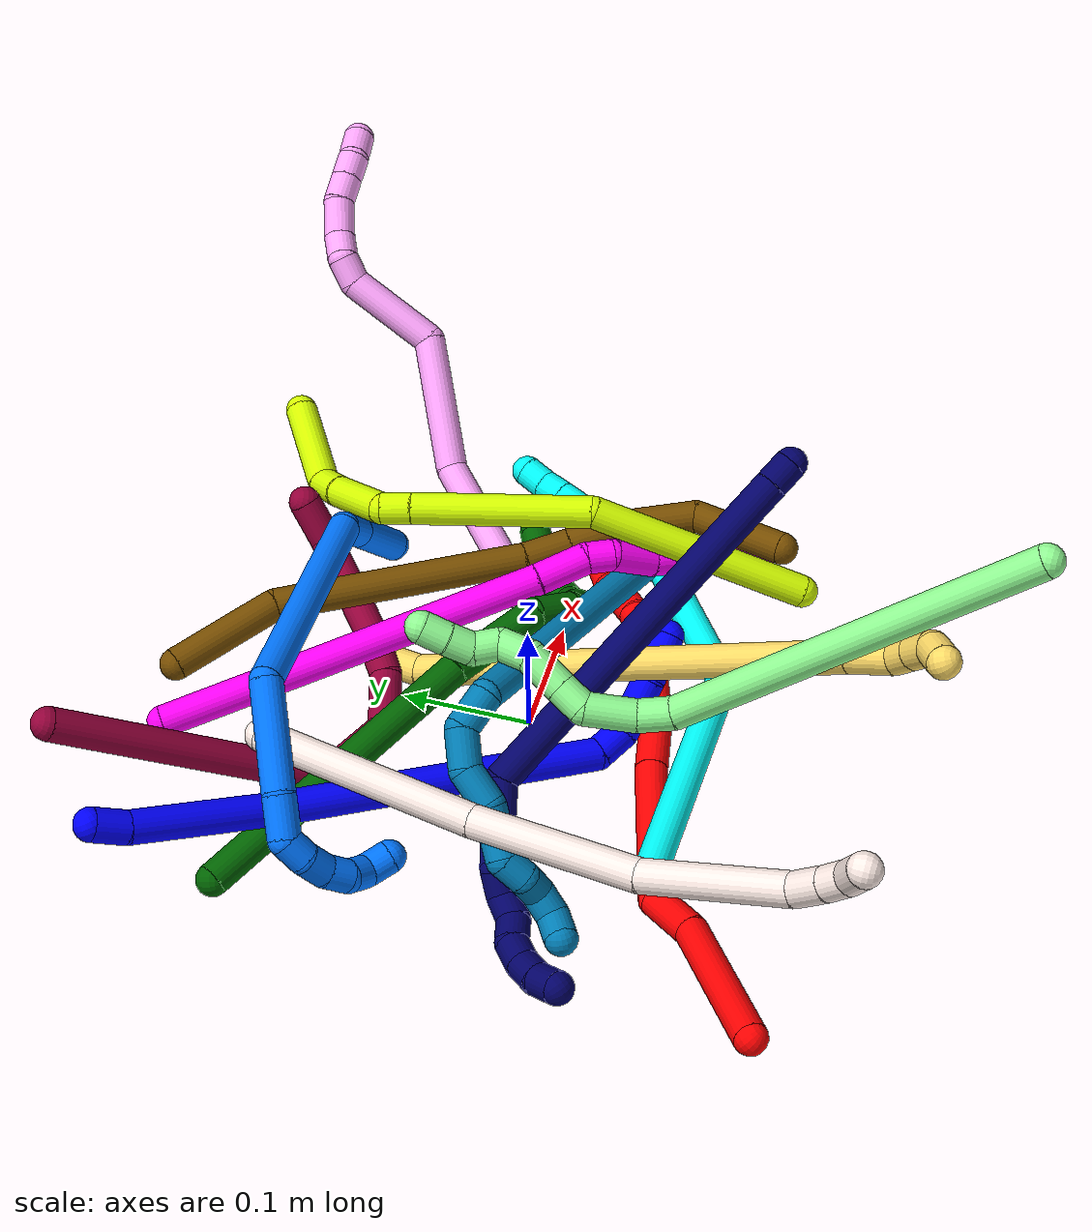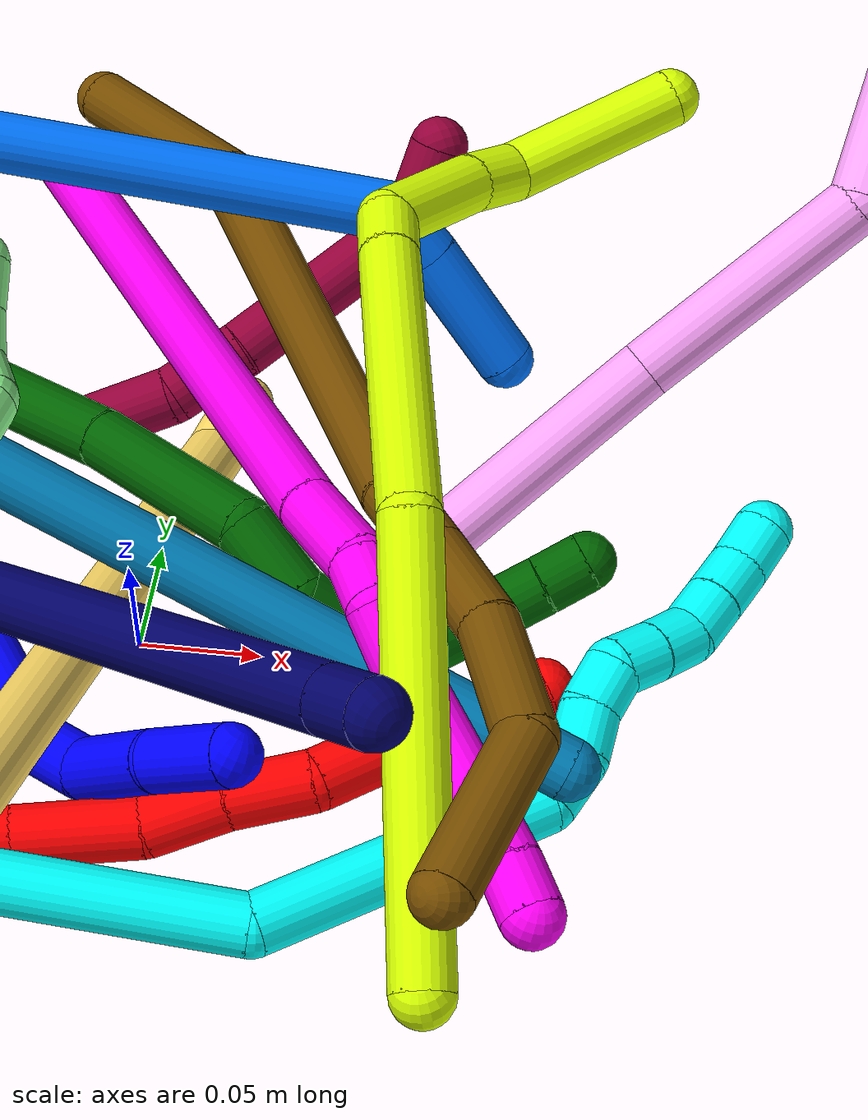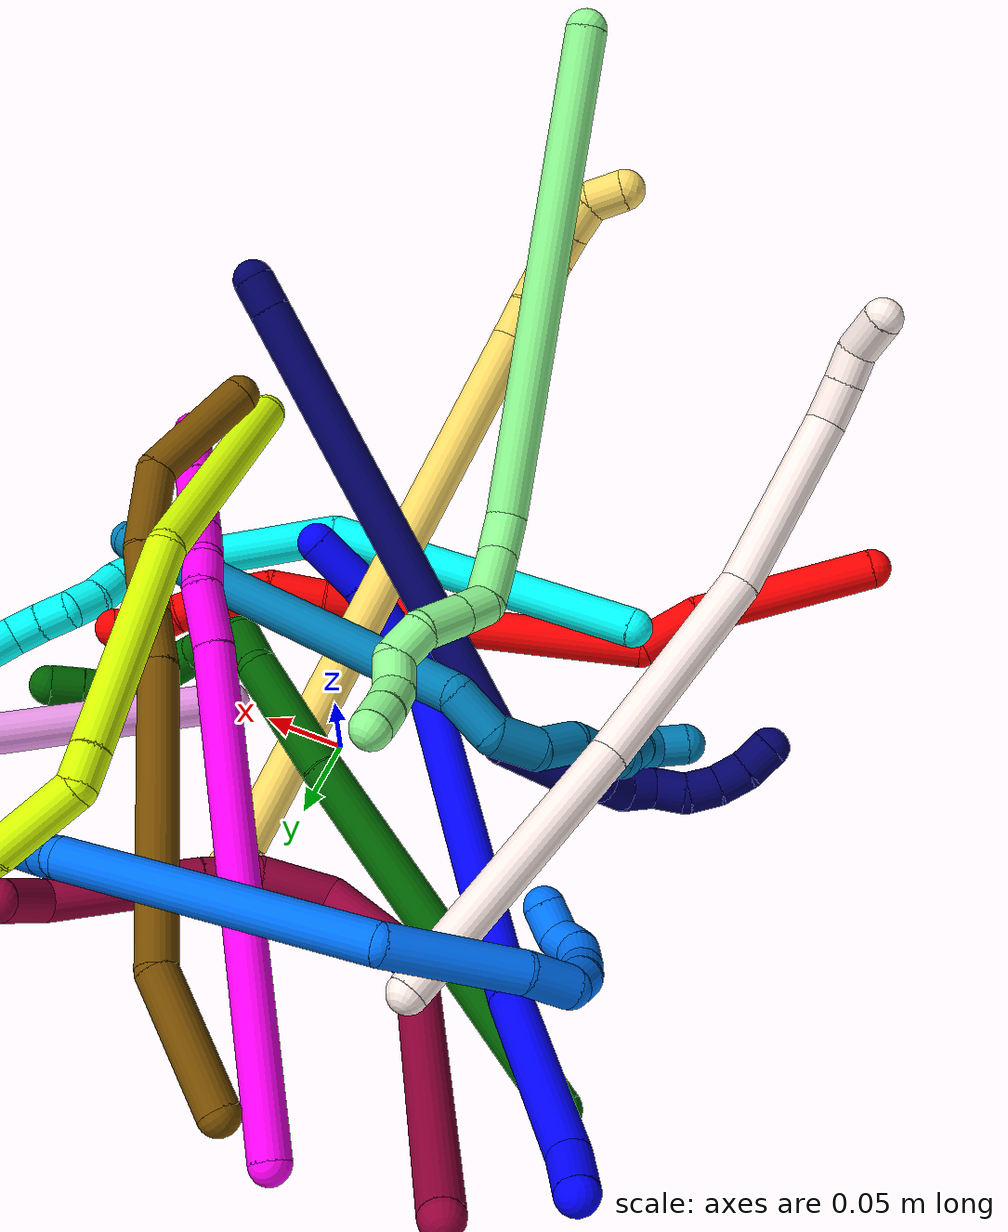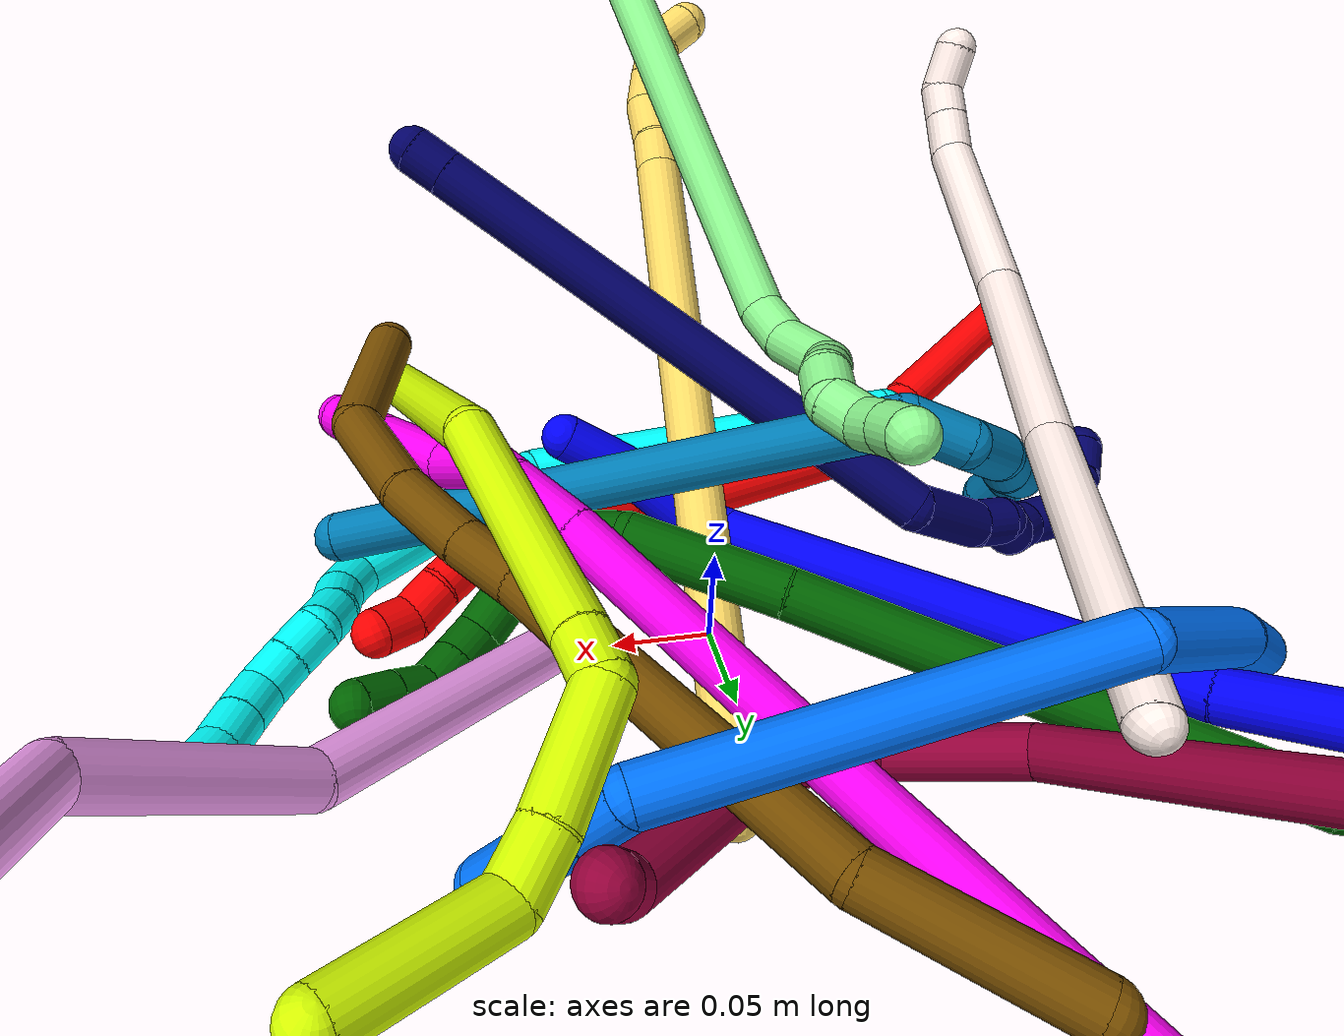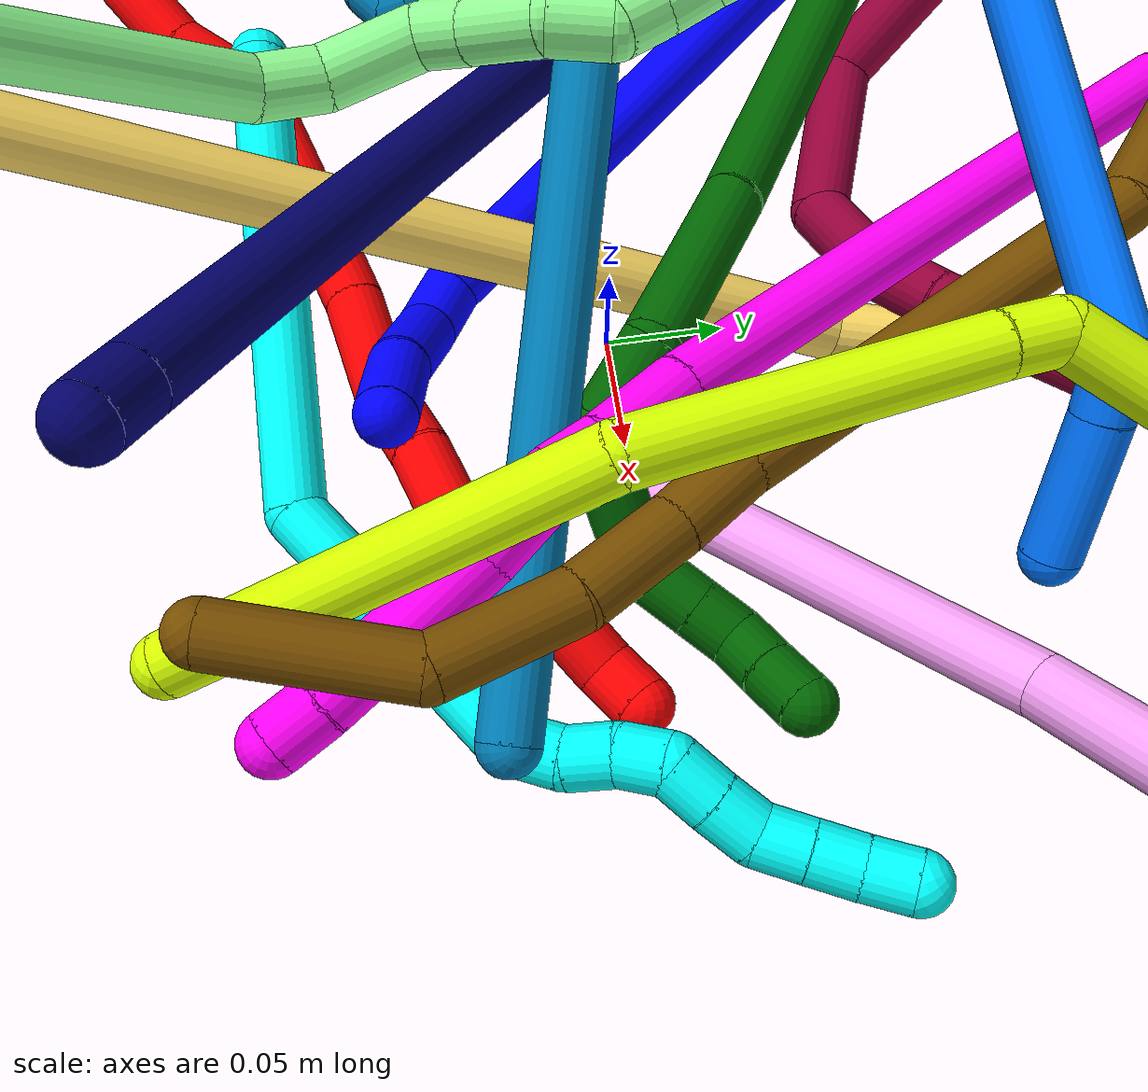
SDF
<sdf version="1.7">
 <world name="default">
  <plugin name="TubeGeneratorPlugin" filename="libtube_generator_plugin.so"/>
  <model name="photoneo_s_sensor">
   <static>1</static>
   <pose>0 0 2 1.57079 1.57079 3.14159</pose>
   <link name="link">
    <inertial><mass>0.1</mass></inertial>
    <sensor name="sensor" type="depth">
     <update_rate>30</update_rate>
     <camera>
      <horizontal_fov>1.22</horizontal_fov>
      <image><width>1920</width><height>1200</height><format>B8G8R8</format></image>
      <clip><near>0.1</near><far>4</far></clip>
      <depth_camera><output>points</output></depth_camera>
     </camera>
     <plugin name="camera_plugin" filename="libgazebo_ros_depth_camera.so">
      <baseline>0.2</baseline>
      <alwaysOn>1</alwaysOn>
      <updateRate>0.0</updateRate>
      <cameraName>camera_ir</cameraName>
      <imageTopicName>/camera/color/image_raw</imageTopicName>
      <cameraInfoTopicName>/camera/color/camera_info</cameraInfoTopicName>
      <depthImageTopicName>/camera/depth/image_raw</depthImageTopicName>
      <depthImageCameraInfoTopicName>/camera/depth/camera_info</depthImageCameraInfoTopicName>
      <pointCloudTopicName>/camera/depth/points</pointCloudTopicName>
      <frameName>fr_optical</frameName>
      <pointCloudCutoff>0.1</pointCloudCutoff>
      <pointCloudCutoffMax>2.0</pointCloudCutoffMax>
      <distortionK1>0</distortionK1>
      <distortionK2>0</distortionK2>
      <distortionK3>0</distortionK3>
      <distortionT1>0</distortionT1>
      <distortionT2>0</distortionT2>
      <CxPrime>0</CxPrime>
      <Cx>0</Cx>
      <Cy>0</Cy>
      <focalLength>0</focalLength>
      <hackBaseline>0</hackBaseline>
     </plugin>
    </sensor>
   </link>
  </model>
  <gravity>0 0 -9.8</gravity>
  <magnetic_field>6e-06 2.3e-05 -4.2e-05</magnetic_field>
  <atmosphere type="adiabatic"/>
  <physics name="default_physics" default="0" type="ode">
   <max_step_size>0.003</max_step_size>
   <real_time_factor>1</real_time_factor>
   <real_time_update_rate>1000</real_time_update_rate>
   <max_contacts>10000</max_contacts>
   <ode>
    <solver>
     <type>quick</type>
     <iters>100</iters>
     <sor>1.3</sor>
     <use_dynamic_moi_rescaling>0</use_dynamic_moi_rescaling>
    </solver>
    <constraints>
     <contact_max_correcting_vel>0</contact_max_correcting_vel>
     <contact_surface_layer>0.001</contact_surface_layer>
     <cfm>0</cfm>
     <erp>0.2</erp>
    </constraints>
   </ode>
  </physics>
  <scene><ambient>0.4 0.4 0.4 1</ambient><background>0.7 0.7 0.7 1</background><shadows>0</shadows></scene>
  <audio><device>default</device></audio>
  <spherical_coordinates>
   <surface_model>EARTH_WGS84</surface_model>
   <latitude_deg>0</latitude_deg>
   <longitude_deg>0</longitude_deg>
   <elevation>0</elevation>
   <heading_deg>0</heading_deg>
  </spherical_coordinates>
  <model name="bin">
   <static>1</static>
   <link name="bottom">
    <collision name="collision-bottom">
     <pose>0 0 -0.01 0 -0 0</pose>
     <geometry><box><size>0.8 0.6 0.02</size></box></geometry>
     <surface>
      <friction><ode><mu>100</mu><mu2>100</mu2></ode></friction>
      <contact><collide_bitmask>65535</collide_bitmask></contact>
     </surface>
    </collision>
   </link>
   <link name="west_wall">
    <collision name="collision-west_wall">
     <pose>-0.41 0 0.1 0 -0 0</pose>
     <geometry><box><size>0.02 0.6 0.2</size></box></geometry>
     <surface>
      <friction><ode><mu>100</mu><mu2>100</mu2></ode></friction>
      <contact><collide_bitmask>65535</collide_bitmask></contact>
     </surface>
    </collision>
   </link>
   <link name="east_wall">
    <collision name="collision-east_wall">
     <pose>0.41 0 0.1 0 -0 0</pose>
     <geometry><box><size>0.02 0.6 0.2</size></box></geometry>
     <surface>
      <friction><ode><mu>100</mu><mu2>100</mu2></ode></friction>
      <contact><collide_bitmask>65535</collide_bitmask></contact>
     </surface>
    </collision>
   </link>
   <link name="south_wall">
    <collision name="collision-south_wall">
     <pose>0 -0.31 0.1 0 -0 0</pose>
     <geometry><box><size>0.8 0.02 0.2</size></box></geometry>
     <surface>
      <friction><ode><mu>100</mu><mu2>100</mu2></ode></friction>
      <contact><collide_bitmask>65535</collide_bitmask></contact>
     </surface>
    </collision>
   </link>
   <link name="north_wall">
    <collision name="collision-north_wall">
     <pose>0 0.31 0.1 0 -0 0</pose>
     <geometry><box><size>0.8 0.02 0.2</size></box></geometry>
     <surface>
      <friction><ode><mu>100</mu><mu2>100</mu2></ode></friction>
      <contact><collide_bitmask>65535</collide_bitmask></contact>
     </surface>
    </collision>
   </link>
  </model>
  <model name="1">
   <static>0</static>
   <link name="1">
    <collision name="collision-cylinder-e_1_1_4">
     <pose>0.007458 -0.008598 0.007206 0.873246 0.586709 0.280083</pose>
     <geometry><cylinder><radius>0.0125</radius><length>0.026941</length></cylinder></geometry>
     <surface>
      <friction><ode><mu>1.16</mu><mu2>1.16</mu2><slip1>0</slip1><slip2>0</slip2></ode></friction>
      <contact><ode><kp>1e+06</kp><kd>1</kd><max_vel>0</max_vel><min_depth>0.001</min_depth></ode></contact>
     </surface>
    </collision>
    <visual name="visual-cylinder-e_1_1_4">
     <pose>0.007458 -0.008598 0.007206 0.873246 0.586709 0.280083</pose>
     <geometry><cylinder><radius>0.0125</radius><length>0.026941</length></cylinder></geometry>
     <material><ambient>0 0 1 1</ambient></material>
    </visual>
    <collision name="collision-cylinder-e_2_4_5">
     <pose>0.049618 -0.056091 0.034426 1.09556 0.670657 0.418956</pose>
     <geometry><cylinder><radius>0.0125</radius><length>0.111673</length></cylinder></geometry>
     <surface>
      <friction><ode><mu>1.16</mu><mu2>1.16</mu2><slip1>0</slip1><slip2>0</slip2></ode></friction>
      <contact><ode><kp>1e+06</kp><kd>1</kd><max_vel>0</max_vel><min_depth>0.001</min_depth></ode></contact>
     </surface>
    </collision>
    <visual name="visual-cylinder-e_2_4_5">
     <pose>0.049618 -0.056091 0.034426 1.09556 0.670657 0.418956</pose>
     <geometry><cylinder><radius>0.0125</radius><length>0.111673</length></cylinder></geometry>
     <material><ambient>0 0 1 1</ambient></material>
    </visual>
    <collision name="collision-cylinder-e_3_5_6">
     <pose>0.177061 -0.172958 0.092905 1.11252 0.817652 0.526243</pose>
     <geometry><cylinder><radius>0.0125</radius><length>0.254243</length></cylinder></geometry>
     <surface>
      <friction><ode><mu>1.16</mu><mu2>1.16</mu2><slip1>0</slip1><slip2>0</slip2></ode></friction>
      <contact><ode><kp>1e+06</kp><kd>1</kd><max_vel>0</max_vel><min_depth>0.001</min_depth></ode></contact>
     </surface>
    </collision>
    <visual name="visual-cylinder-e_3_5_6">
     <pose>0.177061 -0.172958 0.092905 1.11252 0.817652 0.526243</pose>
     <geometry><cylinder><radius>0.0125</radius><length>0.254243</length></cylinder></geometry>
     <material><ambient>0 0 1 1</ambient></material>
    </visual>
    <collision name="collision-cylinder-e_4_6_7">
     <pose>0.278828 -0.259857 0.128782 1.85277 0.770832 0.990141</pose>
     <geometry><cylinder><radius>0.0125</radius><length>0.025911</length></cylinder></geometry>
     <surface>
      <friction><ode><mu>1.16</mu><mu2>1.16</mu2><slip1>0</slip1><slip2>0</slip2></ode></friction>
      <contact><ode><kp>1e+06</kp><kd>1</kd><max_vel>0</max_vel><min_depth>0.001</min_depth></ode></contact>
     </surface>
    </collision>
    <visual name="visual-cylinder-e_4_6_7">
     <pose>0.278828 -0.259857 0.128782 1.85277 0.770832 0.990141</pose>
     <geometry><cylinder><radius>0.0125</radius><length>0.025911</length></cylinder></geometry>
     <material><ambient>0 0 1 1</ambient></material>
    </visual>
    <collision name="collision-cylinder-e_5_7_8">
     <pose>0.30311 -0.276628 0.112039 2.63558 0.755823 1.98707</pose>
     <geometry><cylinder><radius>0.0125</radius><length>0.044483</length></cylinder></geometry>
     <surface>
      <friction><ode><mu>1.16</mu><mu2>1.16</mu2><slip1>0</slip1><slip2>0</slip2></ode></friction>
      <contact><ode><kp>1e+06</kp><kd>1</kd><max_vel>0</max_vel><min_depth>0.001</min_depth></ode></contact>
     </surface>
    </collision>
    <visual name="visual-cylinder-e_5_7_8">
     <pose>0.30311 -0.276628 0.112039 2.63558 0.755823 1.98707</pose>
     <geometry><cylinder><radius>0.0125</radius><length>0.044483</length></cylinder></geometry>
     <material><ambient>0 0 1 1</ambient></material>
    </visual>
    <collision name="collision-cylinder-e_6_8_2">
     <pose>0.328912 -0.294083 0.086306 2.44876 0.611408 1.43687</pose>
     <geometry><cylinder><radius>0.0125</radius><length>0.036749</length></cylinder></geometry>
     <surface>
      <friction><ode><mu>1.16</mu><mu2>1.16</mu2><slip1>0</slip1><slip2>0</slip2></ode></friction>
      <contact><ode><kp>1e+06</kp><kd>1</kd><max_vel>0</max_vel><min_depth>0.001</min_depth></ode></contact>
     </surface>
    </collision>
    <visual name="visual-cylinder-e_6_8_2">
     <pose>0.328912 -0.294083 0.086306 2.44876 0.611408 1.43687</pose>
     <geometry><cylinder><radius>0.0125</radius><length>0.036749</length></cylinder></geometry>
     <material><ambient>0 0 1 1</ambient></material>
    </visual>
    <collision name="collision-sphere-2">
     <pose>0.339459 -0.303693 0.074729 0 -0 0</pose>
     <geometry><sphere><radius>0.0125</radius></sphere></geometry>
     <surface>
      <friction><ode><mu>1.16</mu><mu2>1.16</mu2><slip1>0</slip1><slip2>0</slip2></ode></friction>
      <contact><ode><kp>1e+06</kp><kd>1</kd><max_vel>0</max_vel><min_depth>0.001</min_depth></ode></contact>
     </surface>
    </collision>
    <visual name="visual-sphere-2">
     <pose>0.339459 -0.303693 0.074729 0 -0 0</pose>
     <geometry><sphere><radius>0.0125</radius></sphere></geometry>
     <material><ambient>0 0 1 1</ambient></material>
    </visual>
    <collision name="collision-sphere-4">
     <pose>0.014915 -0.017195 0.014411 0 -0 0</pose>
     <geometry><sphere><radius>0.0125</radius></sphere></geometry>
     <surface>
      <friction><ode><mu>1.16</mu><mu2>1.16</mu2><slip1>0</slip1><slip2>0</slip2></ode></friction>
      <contact><ode><kp>1e+06</kp><kd>1</kd><max_vel>0</max_vel><min_depth>0.001</min_depth></ode></contact>
     </surface>
    </collision>
    <visual name="visual-sphere-4">
     <pose>0.014915 -0.017195 0.014411 0 -0 0</pose>
     <geometry><sphere><radius>0.0125</radius></sphere></geometry>
     <material><ambient>0 0 1 1</ambient></material>
    </visual>
    <collision name="collision-sphere-1">
     <geometry><sphere><radius>0.0125</radius></sphere></geometry>
     <surface>
      <friction><ode><mu>1.16</mu><mu2>1.16</mu2><slip1>0</slip1><slip2>0</slip2></ode></friction>
      <contact><ode><kp>1e+06</kp><kd>1</kd><max_vel>0</max_vel><min_depth>0.001</min_depth></ode></contact>
     </surface>
    </collision>
    <visual name="visual-sphere-1">
     <geometry><sphere><radius>0.0125</radius></sphere></geometry>
     <material><ambient>0 0 1 1</ambient></material>
    </visual>
    <collision name="collision-sphere-8">
     <pose>0.318365 -0.284473 0.097882 0 -0 0</pose>
     <geometry><sphere><radius>0.0125</radius></sphere></geometry>
     <surface>
      <friction><ode><mu>1.16</mu><mu2>1.16</mu2><slip1>0</slip1><slip2>0</slip2></ode></friction>
      <contact><ode><kp>1e+06</kp><kd>1</kd><max_vel>0</max_vel><min_depth>0.001</min_depth></ode></contact>
     </surface>
    </collision>
    <visual name="visual-sphere-8">
     <pose>0.318365 -0.284473 0.097882 0 -0 0</pose>
     <geometry><sphere><radius>0.0125</radius></sphere></geometry>
     <material><ambient>0 0 1 1</ambient></material>
    </visual>
    <collision name="collision-sphere-5">
     <pose>0.08432 -0.094986 0.054441 0 -0 0</pose>
     <geometry><sphere><radius>0.0125</radius></sphere></geometry>
     <surface>
      <friction><ode><mu>1.16</mu><mu2>1.16</mu2><slip1>0</slip1><slip2>0</slip2></ode></friction>
      <contact><ode><kp>1e+06</kp><kd>1</kd><max_vel>0</max_vel><min_depth>0.001</min_depth></ode></contact>
     </surface>
    </collision>
    <visual name="visual-sphere-5">
     <pose>0.08432 -0.094986 0.054441 0 -0 0</pose>
     <geometry><sphere><radius>0.0125</radius></sphere></geometry>
     <material><ambient>0 0 1 1</ambient></material>
    </visual>
    <collision name="collision-sphere-6">
     <pose>0.269801 -0.25093 0.131368 0 -0 0</pose>
     <geometry><sphere><radius>0.0125</radius></sphere></geometry>
     <surface>
      <friction><ode><mu>1.16</mu><mu2>1.16</mu2><slip1>0</slip1><slip2>0</slip2></ode></friction>
      <contact><ode><kp>1e+06</kp><kd>1</kd><max_vel>0</max_vel><min_depth>0.001</min_depth></ode></contact>
     </surface>
    </collision>
    <visual name="visual-sphere-6">
     <pose>0.269801 -0.25093 0.131368 0 -0 0</pose>
     <geometry><sphere><radius>0.0125</radius></sphere></geometry>
     <material><ambient>0 0 1 1</ambient></material>
    </visual>
    <collision name="collision-sphere-7">
     <pose>0.287855 -0.268783 0.126196 0 -0 0</pose>
     <geometry><sphere><radius>0.0125</radius></sphere></geometry>
     <surface>
      <friction><ode><mu>1.16</mu><mu2>1.16</mu2><slip1>0</slip1><slip2>0</slip2></ode></friction>
      <contact><ode><kp>1e+06</kp><kd>1</kd><max_vel>0</max_vel><min_depth>0.001</min_depth></ode></contact>
     </surface>
    </collision>
    <visual name="visual-sphere-7">
     <pose>0.287855 -0.268783 0.126196 0 -0 0</pose>
     <geometry><sphere><radius>0.0125</radius></sphere></geometry>
     <material><ambient>0 0 1 1</ambient></material>
    </visual>
    <inertial>
     <pose>0.167107 -0.160629 0.078303 0 -0 0</pose>
     <mass>0.5</mass>
     <inertia>
      <ixx>0.001454</ixx>
      <ixy>0</ixy>
      <ixz>0</ixz>
      <iyy>0.00157</iyy>
      <iyz>0</iyz>
      <izz>-0.000148</izz>
     </inertia>
    </inertial>
   </link>
   <pose>-0.259623 0.239541 0.104206 2.59753 -0.484221 -1.31061</pose>
  </model>
  <model name="2">
   <static>0</static>
   <link name="2">
    <collision name="collision-cylinder-e_1_1_4">
     <pose>0.051038 0.021755 -0.012881 -2.10537 1.11087 -1.65566</pose>
     <geometry><cylinder><radius>0.0125</radius><length>0.113912</length></cylinder></geometry>
     <surface>
      <friction><ode><mu>1.16</mu><mu2>1.16</mu2><slip1>0</slip1><slip2>0</slip2></ode></friction>
      <contact><ode><kp>1e+06</kp><kd>1</kd><max_vel>0</max_vel><min_depth>0.001</min_depth></ode></contact>
     </surface>
    </collision>
    <visual name="visual-cylinder-e_1_1_4">
     <pose>0.051038 0.021755 -0.012881 -2.10537 1.11087 -1.65566</pose>
     <geometry><cylinder><radius>0.0125</radius><length>0.113912</length></cylinder></geometry>
     <material><ambient>1 0 0 1</ambient></material>
    </visual>
    <collision name="collision-cylinder-e_2_4_5">
     <pose>0.117239 0.054849 -0.034492 -2.22693 0.8143 -1.43912</pose>
     <geometry><cylinder><radius>0.0125</radius><length>0.041701</length></cylinder></geometry>
     <surface>
      <friction><ode><mu>1.16</mu><mu2>1.16</mu2><slip1>0</slip1><slip2>0</slip2></ode></friction>
      <contact><ode><kp>1e+06</kp><kd>1</kd><max_vel>0</max_vel><min_depth>0.001</min_depth></ode></contact>
     </surface>
    </collision>
    <visual name="visual-cylinder-e_2_4_5">
     <pose>0.117239 0.054849 -0.034492 -2.22693 0.8143 -1.43912</pose>
     <geometry><cylinder><radius>0.0125</radius><length>0.041701</length></cylinder></geometry>
     <material><ambient>1 0 0 1</ambient></material>
    </visual>
    <collision name="collision-cylinder-e_3_5_6">
     <pose>0.189767 0.084491 -0.034837 -1.14115 1.23328 -0.853888</pose>
     <geometry><cylinder><radius>0.0125</radius><length>0.121589</length></cylinder></geometry>
     <surface>
      <friction><ode><mu>1.16</mu><mu2>1.16</mu2><slip1>0</slip1><slip2>0</slip2></ode></friction>
      <contact><ode><kp>1e+06</kp><kd>1</kd><max_vel>0</max_vel><min_depth>0.001</min_depth></ode></contact>
     </surface>
    </collision>
    <visual name="visual-cylinder-e_3_5_6">
     <pose>0.189767 0.084491 -0.034837 -1.14115 1.23328 -0.853888</pose>
     <geometry><cylinder><radius>0.0125</radius><length>0.121589</length></cylinder></geometry>
     <material><ambient>1 0 0 1</ambient></material>
    </visual>
    <collision name="collision-cylinder-e_4_6_7">
     <pose>0.270861 0.109356 -0.020272 -0.815536 1.20777 -0.579247</pose>
     <geometry><cylinder><radius>0.0125</radius><length>0.050769</length></cylinder></geometry>
     <surface>
      <friction><ode><mu>1.16</mu><mu2>1.16</mu2><slip1>0</slip1><slip2>0</slip2></ode></friction>
      <contact><ode><kp>1e+06</kp><kd>1</kd><max_vel>0</max_vel><min_depth>0.001</min_depth></ode></contact>
     </surface>
    </collision>
    <visual name="visual-cylinder-e_4_6_7">
     <pose>0.270861 0.109356 -0.020272 -0.815536 1.20777 -0.579247</pose>
     <geometry><cylinder><radius>0.0125</radius><length>0.050769</length></cylinder></geometry>
     <material><ambient>1 0 0 1</ambient></material>
    </visual>
    <collision name="collision-cylinder-e_5_7_8">
     <pose>0.308467 0.124209 -0.010072 -1.11916 0.984626 -0.648223</pose>
     <geometry><cylinder><radius>0.0125</radius><length>0.033314</length></cylinder></geometry>
     <surface>
      <friction><ode><mu>1.16</mu><mu2>1.16</mu2><slip1>0</slip1><slip2>0</slip2></ode></friction>
      <contact><ode><kp>1e+06</kp><kd>1</kd><max_vel>0</max_vel><min_depth>0.001</min_depth></ode></contact>
     </surface>
    </collision>
    <visual name="visual-cylinder-e_5_7_8">
     <pose>0.308467 0.124209 -0.010072 -1.11916 0.984626 -0.648223</pose>
     <geometry><cylinder><radius>0.0125</radius><length>0.033314</length></cylinder></geometry>
     <material><ambient>1 0 0 1</ambient></material>
    </visual>
    <collision name="collision-cylinder-e_6_8_9">
     <pose>0.33784 0.139123 -0.002187 -1.04276 1.11128 -0.685149</pose>
     <geometry><cylinder><radius>0.0125</radius><length>0.03458</length></cylinder></geometry>
     <surface>
      <friction><ode><mu>1.16</mu><mu2>1.16</mu2><slip1>0</slip1><slip2>0</slip2></ode></friction>
      <contact><ode><kp>1e+06</kp><kd>1</kd><max_vel>0</max_vel><min_depth>0.001</min_depth></ode></contact>
     </surface>
    </collision>
    <visual name="visual-cylinder-e_6_8_9">
     <pose>0.33784 0.139123 -0.002187 -1.04276 1.11128 -0.685149</pose>
     <geometry><cylinder><radius>0.0125</radius><length>0.03458</length></cylinder></geometry>
     <material><ambient>1 0 0 1</ambient></material>
    </visual>
    <collision name="collision-cylinder-e_7_9_10">
     <pose>0.367597 0.154592 -0.00042 -1.80358 1.00335 -1.213</pose>
     <geometry><cylinder><radius>0.0125</radius><length>0.033823</length></cylinder></geometry>
     <surface>
      <friction><ode><mu>1.16</mu><mu2>1.16</mu2><slip1>0</slip1><slip2>0</slip2></ode></friction>
      <contact><ode><kp>1e+06</kp><kd>1</kd><max_vel>0</max_vel><min_depth>0.001</min_depth></ode></contact>
     </surface>
    </collision>
    <visual name="visual-cylinder-e_7_9_10">
     <pose>0.367597 0.154592 -0.00042 -1.80358 1.00335 -1.213</pose>
     <geometry><cylinder><radius>0.0125</radius><length>0.033823</length></cylinder></geometry>
     <material><ambient>1 0 0 1</ambient></material>
    </visual>
    <collision name="collision-cylinder-e_8_10_11">
     <pose>0.393472 0.169725 -0.006342 -2.1172 1.00586 -1.54899</pose>
     <geometry><cylinder><radius>0.0125</radius><length>0.0275</length></cylinder></geometry>
     <surface>
      <friction><ode><mu>1.16</mu><mu2>1.16</mu2><slip1>0</slip1><slip2>0</slip2></ode></friction>
      <contact><ode><kp>1e+06</kp><kd>1</kd><max_vel>0</max_vel><min_depth>0.001</min_depth></ode></contact>
     </surface>
    </collision>
    <visual name="visual-cylinder-e_8_10_11">
     <pose>0.393472 0.169725 -0.006342 -2.1172 1.00586 -1.54899</pose>
     <geometry><cylinder><radius>0.0125</radius><length>0.0275</length></cylinder></geometry>
     <material><ambient>1 0 0 1</ambient></material>
    </visual>
    <collision name="collision-cylinder-e_9_11_12">
     <pose>0.414726 0.179227 -0.014087 -2.45511 1.08681 -2.0731</pose>
     <geometry><cylinder><radius>0.0125</radius><length>0.021784</length></cylinder></geometry>
     <surface>
      <friction><ode><mu>1.16</mu><mu2>1.16</mu2><slip1>0</slip1><slip2>0</slip2></ode></friction>
      <contact><ode><kp>1e+06</kp><kd>1</kd><max_vel>0</max_vel><min_depth>0.001</min_depth></ode></contact>
     </surface>
    </collision>
    <visual name="visual-cylinder-e_9_11_12">
     <pose>0.414726 0.179227 -0.014087 -2.45511 1.08681 -2.0731</pose>
     <geometry><cylinder><radius>0.0125</radius><length>0.021784</length></cylinder></geometry>
     <material><ambient>1 0 0 1</ambient></material>
    </visual>
    <collision name="collision-cylinder-e_10_12_2">
     <pose>0.432804 0.188702 -0.017623 -1.50954 0.931354 -0.883074</pose>
     <geometry><cylinder><radius>0.0125</radius><length>0.021029</length></cylinder></geometry>
     <surface>
      <friction><ode><mu>1.16</mu><mu2>1.16</mu2><slip1>0</slip1><slip2>0</slip2></ode></friction>
      <contact><ode><kp>1e+06</kp><kd>1</kd><max_vel>0</max_vel><min_depth>0.001</min_depth></ode></contact>
     </surface>
    </collision>
    <visual name="visual-cylinder-e_10_12_2">
     <pose>0.432804 0.188702 -0.017623 -1.50954 0.931354 -0.883074</pose>
     <geometry><cylinder><radius>0.0125</radius><length>0.021029</length></cylinder></geometry>
     <material><ambient>1 0 0 1</ambient></material>
    </visual>
    <collision name="collision-sphere-2">
     <pose>0.441241 0.194965 -0.017239 0 -0 0</pose>
     <geometry><sphere><radius>0.0125</radius></sphere></geometry>
     <surface>
      <friction><ode><mu>1.16</mu><mu2>1.16</mu2><slip1>0</slip1><slip2>0</slip2></ode></friction>
      <contact><ode><kp>1e+06</kp><kd>1</kd><max_vel>0</max_vel><min_depth>0.001</min_depth></ode></contact>
     </surface>
    </collision>
    <visual name="visual-sphere-2">
     <pose>0.441241 0.194965 -0.017239 0 -0 0</pose>
     <geometry><sphere><radius>0.0125</radius></sphere></geometry>
     <material><ambient>1 0 0 1</ambient></material>
    </visual>
    <collision name="collision-sphere-12">
     <pose>0.424367 0.182439 -0.018007 0 -0 0</pose>
     <geometry><sphere><radius>0.0125</radius></sphere></geometry>
     <surface>
      <friction><ode><mu>1.16</mu><mu2>1.16</mu2><slip1>0</slip1><slip2>0</slip2></ode></friction>
      <contact><ode><kp>1e+06</kp><kd>1</kd><max_vel>0</max_vel><min_depth>0.001</min_depth></ode></contact>
     </surface>
    </collision>
    <visual name="visual-sphere-12">
     <pose>0.424367 0.182439 -0.018007 0 -0 0</pose>
     <geometry><sphere><radius>0.0125</radius></sphere></geometry>
     <material><ambient>1 0 0 1</ambient></material>
    </visual>
    <collision name="collision-sphere-11">
     <pose>0.405085 0.176015 -0.010167 0 -0 0</pose>
     <geometry><sphere><radius>0.0125</radius></sphere></geometry>
     <surface>
      <friction><ode><mu>1.16</mu><mu2>1.16</mu2><slip1>0</slip1><slip2>0</slip2></ode></friction>
      <contact><ode><kp>1e+06</kp><kd>1</kd><max_vel>0</max_vel><min_depth>0.001</min_depth></ode></contact>
     </surface>
    </collision>
    <visual name="visual-sphere-11">
     <pose>0.405085 0.176015 -0.010167 0 -0 0</pose>
     <geometry><sphere><radius>0.0125</radius></sphere></geometry>
     <material><ambient>1 0 0 1</ambient></material>
    </visual>
    <collision name="collision-sphere-10">
     <pose>0.381858 0.163436 -0.002517 0 -0 0</pose>
     <geometry><sphere><radius>0.0125</radius></sphere></geometry>
     <surface>
      <friction><ode><mu>1.16</mu><mu2>1.16</mu2><slip1>0</slip1><slip2>0</slip2></ode></friction>
      <contact><ode><kp>1e+06</kp><kd>1</kd><max_vel>0</max_vel><min_depth>0.001</min_depth></ode></contact>
     </surface>
    </collision>
    <visual name="visual-sphere-10">
     <pose>0.381858 0.163436 -0.002517 0 -0 0</pose>
     <geometry><sphere><radius>0.0125</radius></sphere></geometry>
     <material><ambient>1 0 0 1</ambient></material>
    </visual>
    <collision name="collision-sphere-9">
     <pose>0.353336 0.145747 0.001677 0 -0 0</pose>
     <geometry><sphere><radius>0.0125</radius></sphere></geometry>
     <surface>
      <friction><ode><mu>1.16</mu><mu2>1.16</mu2><slip1>0</slip1><slip2>0</slip2></ode></friction>
      <contact><ode><kp>1e+06</kp><kd>1</kd><max_vel>0</max_vel><min_depth>0.001</min_depth></ode></contact>
     </surface>
    </collision>
    <visual name="visual-sphere-9">
     <pose>0.353336 0.145747 0.001677 0 -0 0</pose>
     <geometry><sphere><radius>0.0125</radius></sphere></geometry>
     <material><ambient>1 0 0 1</ambient></material>
    </visual>
    <collision name="collision-sphere-4">
     <pose>0.102075 0.043509 -0.025761 0 -0 0</pose>
     <geometry><sphere><radius>0.0125</radius></sphere></geometry>
     <surface>
      <friction><ode><mu>1.16</mu><mu2>1.16</mu2><slip1>0</slip1><slip2>0</slip2></ode></friction>
      <contact><ode><kp>1e+06</kp><kd>1</kd><max_vel>0</max_vel><min_depth>0.001</min_depth></ode></contact>
     </surface>
    </collision>
    <visual name="visual-sphere-4">
     <pose>0.102075 0.043509 -0.025761 0 -0 0</pose>
     <geometry><sphere><radius>0.0125</radius></sphere></geometry>
     <material><ambient>1 0 0 1</ambient></material>
    </visual>
    <collision name="collision-sphere-1">
     <geometry><sphere><radius>0.0125</radius></sphere></geometry>
     <surface>
      <friction><ode><mu>1.16</mu><mu2>1.16</mu2><slip1>0</slip1><slip2>0</slip2></ode></friction>
      <contact><ode><kp>1e+06</kp><kd>1</kd><max_vel>0</max_vel><min_depth>0.001</min_depth></ode></contact>
     </surface>
    </collision>
    <visual name="visual-sphere-1">
     <geometry><sphere><radius>0.0125</radius></sphere></geometry>
     <material><ambient>1 0 0 1</ambient></material>
    </visual>
    <collision name="collision-sphere-8">
     <pose>0.322344 0.132499 -0.00605 0 -0 0</pose>
     <geometry><sphere><radius>0.0125</radius></sphere></geometry>
     <surface>
      <friction><ode><mu>1.16</mu><mu2>1.16</mu2><slip1>0</slip1><slip2>0</slip2></ode></friction>
      <contact><ode><kp>1e+06</kp><kd>1</kd><max_vel>0</max_vel><min_depth>0.001</min_depth></ode></contact>
     </surface>
    </collision>
    <visual name="visual-sphere-8">
     <pose>0.322344 0.132499 -0.00605 0 -0 0</pose>
     <geometry><sphere><radius>0.0125</radius></sphere></geometry>
     <material><ambient>1 0 0 1</ambient></material>
    </visual>
    <collision name="collision-sphere-5">
     <pose>0.132402 0.066189 -0.043223 0 -0 0</pose>
     <geometry><sphere><radius>0.0125</radius></sphere></geometry>
     <surface>
      <friction><ode><mu>1.16</mu><mu2>1.16</mu2><slip1>0</slip1><slip2>0</slip2></ode></friction>
      <contact><ode><kp>1e+06</kp><kd>1</kd><max_vel>0</max_vel><min_depth>0.001</min_depth></ode></contact>
     </surface>
    </collision>
    <visual name="visual-sphere-5">
     <pose>0.132402 0.066189 -0.043223 0 -0 0</pose>
     <geometry><sphere><radius>0.0125</radius></sphere></geometry>
     <material><ambient>1 0 0 1</ambient></material>
    </visual>
    <collision name="collision-sphere-6">
     <pose>0.247132 0.102793 -0.026451 0 -0 0</pose>
     <geometry><sphere><radius>0.0125</radius></sphere></geometry>
     <surface>
      <friction><ode><mu>1.16</mu><mu2>1.16</mu2><slip1>0</slip1><slip2>0</slip2></ode></friction>
      <contact><ode><kp>1e+06</kp><kd>1</kd><max_vel>0</max_vel><min_depth>0.001</min_depth></ode></contact>
     </surface>
    </collision>
    <visual name="visual-sphere-6">
     <pose>0.247132 0.102793 -0.026451 0 -0 0</pose>
     <geometry><sphere><radius>0.0125</radius></sphere></geometry>
     <material><ambient>1 0 0 1</ambient></material>
    </visual>
    <collision name="collision-sphere-7">
     <pose>0.294591 0.115919 -0.014093 0 -0 0</pose>
     <geometry><sphere><radius>0.0125</radius></sphere></geometry>
     <surface>
      <friction><ode><mu>1.16</mu><mu2>1.16</mu2><slip1>0</slip1><slip2>0</slip2></ode></friction>
      <contact><ode><kp>1e+06</kp><kd>1</kd><max_vel>0</max_vel><min_depth>0.001</min_depth></ode></contact>
     </surface>
    </collision>
    <visual name="visual-sphere-7">
     <pose>0.294591 0.115919 -0.014093 0 -0 0</pose>
     <geometry><sphere><radius>0.0125</radius></sphere></geometry>
     <material><ambient>1 0 0 1</ambient></material>
    </visual>
    <inertial>
     <pose>0.221751 0.094615 -0.018896 0 -0 0</pose>
     <mass>0.5</mass>
     <inertia>
      <ixx>-3.8e-05</ixx>
      <ixy>0</ixy>
      <ixz>0</ixz>
      <iyy>0.000182</iyy>
      <iyz>0</iyz>
      <izz>-0.000408</izz>
     </inertia>
    </inertial>
   </link>
   <pose>-0.262794 -0.232049 0.0442 0.691614 0.310391 0.131149</pose>
  </model>
  <model name="3">
   <static>0</static>
   <link name="3">
    <collision name="collision-cylinder-e_1_1_4">
     <pose>0.102409 0.013151 -0.023422 -2.62996 1.31428 -2.48792</pose>
     <geometry><cylinder><radius>0.0125</radius><length>0.211746</length></cylinder></geometry>
     <surface>
      <friction><ode><mu>1.16</mu><mu2>1.16</mu2><slip1>0</slip1><slip2>0</slip2></ode></friction>
      <contact><ode><kp>1e+06</kp><kd>1</kd><max_vel>0</max_vel><min_depth>0.001</min_depth></ode></contact>
     </surface>
    </collision>
    <visual name="visual-cylinder-e_1_1_4">
     <pose>0.102409 0.013151 -0.023422 -2.62996 1.31428 -2.48792</pose>
     <geometry><cylinder><radius>0.0125</radius><length>0.211746</length></cylinder></geometry>
     <material><ambient>0.003922 1 0.996078 1</ambient></material>
    </visual>
    <collision name="collision-cylinder-e_2_4_5">
     <pose>0.259728 0.047985 -0.025306 -0.788744 1.06293 -0.479899</pose>
     <geometry><cylinder><radius>0.0125</radius><length>0.125685</length></cylinder></geometry>
     <surface>
      <friction><ode><mu>1.16</mu><mu2>1.16</mu2><slip1>0</slip1><slip2>0</slip2></ode></friction>
      <contact><ode><kp>1e+06</kp><kd>1</kd><max_vel>0</max_vel><min_depth>0.001</min_depth></ode></contact>
     </surface>
    </collision>
    <visual name="visual-cylinder-e_2_4_5">
     <pose>0.259728 0.047985 -0.025306 -0.788744 1.06293 -0.479899</pose>
     <geometry><cylinder><radius>0.0125</radius><length>0.125685</length></cylinder></geometry>
     <material><ambient>0.003922 1 0.996078 1</ambient></material>
    </visual>
    <collision name="collision-cylinder-e_3_5_6">
     <pose>0.32103 0.072753 0.004861 -0.343439 0.608969 -0.108894</pose>
     <geometry><cylinder><radius>0.0125</radius><length>0.022344</length></cylinder></geometry>
     <surface>
      <friction><ode><mu>1.16</mu><mu2>1.16</mu2><slip1>0</slip1><slip2>0</slip2></ode></friction>
      <contact><ode><kp>1e+06</kp><kd>1</kd><max_vel>0</max_vel><min_depth>0.001</min_depth></ode></contact>
     </surface>
    </collision>
    <visual name="visual-cylinder-e_3_5_6">
     <pose>0.32103 0.072753 0.004861 -0.343439 0.608969 -0.108894</pose>
     <geometry><cylinder><radius>0.0125</radius><length>0.022344</length></cylinder></geometry>
     <material><ambient>0.003922 1 0.996078 1</ambient></material>
    </visual>
    <collision name="collision-cylinder-e_4_6_7">
     <pose>0.330185 0.078231 0.022903 -0.248912 0.277279 -0.034909</pose>
     <geometry><cylinder><radius>0.0125</radius><length>0.020198</length></cylinder></geometry>
     <surface>
      <friction><ode><mu>1.16</mu><mu2>1.16</mu2><slip1>0</slip1><slip2>0</slip2></ode></friction>
      <contact><ode><kp>1e+06</kp><kd>1</kd><max_vel>0</max_vel><min_depth>0.001</min_depth></ode></contact>
     </surface>
    </collision>
    <visual name="visual-cylinder-e_4_6_7">
     <pose>0.330185 0.078231 0.022903 -0.248912 0.277279 -0.034909</pose>
     <geometry><cylinder><radius>0.0125</radius><length>0.020198</length></cylinder></geometry>
     <material><ambient>0.003922 1 0.996078 1</ambient></material>
    </visual>
    <collision name="collision-cylinder-e_5_7_8">
     <pose>0.33811 0.083001 0.040551 -0.280981 0.542033 -0.078549</pose>
     <geometry><cylinder><radius>0.0125</radius><length>0.020008</length></cylinder></geometry>
     <surface>
      <friction><ode><mu>1.16</mu><mu2>1.16</mu2><slip1>0</slip1><slip2>0</slip2></ode></friction>
      <contact><ode><kp>1e+06</kp><kd>1</kd><max_vel>0</max_vel><min_depth>0.001</min_depth></ode></contact>
     </surface>
    </collision>
    <visual name="visual-cylinder-e_5_7_8">
     <pose>0.33811 0.083001 0.040551 -0.280981 0.542033 -0.078549</pose>
     <geometry><cylinder><radius>0.0125</radius><length>0.020008</length></cylinder></geometry>
     <material><ambient>0.003922 1 0.996078 1</ambient></material>
    </visual>
    <collision name="collision-cylinder-e_6_8_9">
     <pose>0.350763 0.091016 0.052265 -1.01782 0.846617 -0.492543</pose>
     <geometry><cylinder><radius>0.0125</radius><length>0.020003</length></cylinder></geometry>
     <surface>
      <friction><ode><mu>1.16</mu><mu2>1.16</mu2><slip1>0</slip1><slip2>0</slip2></ode></friction>
      <contact><ode><kp>1e+06</kp><kd>1</kd><max_vel>0</max_vel><min_depth>0.001</min_depth></ode></contact>
     </surface>
    </collision>
    <visual name="visual-cylinder-e_6_8_9">
     <pose>0.350763 0.091016 0.052265 -1.01782 0.846617 -0.492543</pose>
     <geometry><cylinder><radius>0.0125</radius><length>0.020003</length></cylinder></geometry>
     <material><ambient>0.003922 1 0.996078 1</ambient></material>
    </visual>
    <collision name="collision-cylinder-e_7_9_10">
     <pose>0.365393 0.102513 0.059582 -0.990899 0.79502 -0.446237</pose>
     <geometry><cylinder><radius>0.0125</radius><length>0.020002</length></cylinder></geometry>
     <surface>
      <friction><ode><mu>1.16</mu><mu2>1.16</mu2><slip1>0</slip1><slip2>0</slip2></ode></friction>
      <contact><ode><kp>1e+06</kp><kd>1</kd><max_vel>0</max_vel><min_depth>0.001</min_depth></ode></contact>
     </surface>
    </collision>
    <visual name="visual-cylinder-e_7_9_10">
     <pose>0.365393 0.102513 0.059582 -0.990899 0.79502 -0.446237</pose>
     <geometry><cylinder><radius>0.0125</radius><length>0.020002</length></cylinder></geometry>
     <material><ambient>0.003922 1 0.996078 1</ambient></material>
    </visual>
    <collision name="collision-cylinder-e_8_10_11">
     <pose>0.378138 0.112495 0.070605 -0.521089 0.594824 -0.163068</pose>
     <geometry><cylinder><radius>0.0125</radius><length>0.020004</length></cylinder></geometry>
     <surface>
      <friction><ode><mu>1.16</mu><mu2>1.16</mu2><slip1>0</slip1><slip2>0</slip2></ode></friction>
      <contact><ode><kp>1e+06</kp><kd>1</kd><max_vel>0</max_vel><min_depth>0.001</min_depth></ode></contact>
     </surface>
    </collision>
    <visual name="visual-cylinder-e_8_10_11">
     <pose>0.378138 0.112495 0.070605 -0.521089 0.594824 -0.163068</pose>
     <geometry><cylinder><radius>0.0125</radius><length>0.020004</length></cylinder></geometry>
     <material><ambient>0.003922 1 0.996078 1</ambient></material>
    </visual>
    <collision name="collision-cylinder-e_9_11_12">
     <pose>0.38919 0.120988 0.084954 -0.547556 0.575788 -0.165937</pose>
     <geometry><cylinder><radius>0.0125</radius><length>0.020008</length></cylinder></geometry>
     <surface>
      <friction><ode><mu>1.16</mu><mu2>1.16</mu2><slip1>0</slip1><slip2>0</slip2></ode></friction>
      <contact><ode><kp>1e+06</kp><kd>1</kd><max_vel>0</max_vel><min_depth>0.001</min_depth></ode></contact>
     </surface>
    </collision>
    <visual name="visual-cylinder-e_9_11_12">
     <pose>0.38919 0.120988 0.084954 -0.547556 0.575788 -0.165937</pose>
     <geometry><cylinder><radius>0.0125</radius><length>0.020008</length></cylinder></geometry>
     <material><ambient>0.003922 1 0.996078 1</ambient></material>
    </visual>
    <collision name="collision-cylinder-e_10_12_2">
     <pose>0.400138 0.128344 0.099918 -0.365836 0.58238 -0.11077</pose>
     <geometry><cylinder><radius>0.0125</radius><length>0.020002</length></cylinder></geometry>
     <surface>
      <friction><ode><mu>1.16</mu><mu2>1.16</mu2><slip1>0</slip1><slip2>0</slip2></ode></friction>
      <contact><ode><kp>1e+06</kp><kd>1</kd><max_vel>0</max_vel><min_depth>0.001</min_depth></ode></contact>
     </surface>
    </collision>
    <visual name="visual-cylinder-e_10_12_2">
     <pose>0.400138 0.128344 0.099918 -0.365836 0.58238 -0.11077</pose>
     <geometry><cylinder><radius>0.0125</radius><length>0.020002</length></cylinder></geometry>
     <material><ambient>0.003922 1 0.996078 1</ambient></material>
    </visual>
    <collision name="collision-sphere-2">
     <pose>0.405638 0.131332 0.107717 0 -0 0</pose>
     <geometry><sphere><radius>0.0125</radius></sphere></geometry>
     <surface>
      <friction><ode><mu>1.16</mu><mu2>1.16</mu2><slip1>0</slip1><slip2>0</slip2></ode></friction>
      <contact><ode><kp>1e+06</kp><kd>1</kd><max_vel>0</max_vel><min_depth>0.001</min_depth></ode></contact>
     </surface>
    </collision>
    <visual name="visual-sphere-2">
     <pose>0.405638 0.131332 0.107717 0 -0 0</pose>
     <geometry><sphere><radius>0.0125</radius></sphere></geometry>
     <material><ambient>0.003922 1 0.996078 1</ambient></material>
    </visual>
    <collision name="collision-sphere-12">
     <pose>0.394637 0.125356 0.092118 0 -0 0</pose>
     <geometry><sphere><radius>0.0125</radius></sphere></geometry>
     <surface>
      <friction><ode><mu>1.16</mu><mu2>1.16</mu2><slip1>0</slip1><slip2>0</slip2></ode></friction>
      <contact><ode><kp>1e+06</kp><kd>1</kd><max_vel>0</max_vel><min_depth>0.001</min_depth></ode></contact>
     </surface>
    </collision>
    <visual name="visual-sphere-12">
     <pose>0.394637 0.125356 0.092118 0 -0 0</pose>
     <geometry><sphere><radius>0.0125</radius></sphere></geometry>
     <material><ambient>0.003922 1 0.996078 1</ambient></material>
    </visual>
    <collision name="collision-sphere-11">
     <pose>0.383743 0.116619 0.077789 0 -0 0</pose>
     <geometry><sphere><radius>0.0125</radius></sphere></geometry>
     <surface>
      <friction><ode><mu>1.16</mu><mu2>1.16</mu2><slip1>0</slip1><slip2>0</slip2></ode></friction>
      <contact><ode><kp>1e+06</kp><kd>1</kd><max_vel>0</max_vel><min_depth>0.001</min_depth></ode></contact>
     </surface>
    </collision>
    <visual name="visual-sphere-11">
     <pose>0.383743 0.116619 0.077789 0 -0 0</pose>
     <geometry><sphere><radius>0.0125</radius></sphere></geometry>
     <material><ambient>0.003922 1 0.996078 1</ambient></material>
    </visual>
    <collision name="collision-sphere-10">
     <pose>0.372533 0.108371 0.06342 0 -0 0</pose>
     <geometry><sphere><radius>0.0125</radius></sphere></geometry>
     <surface>
      <friction><ode><mu>1.16</mu><mu2>1.16</mu2><slip1>0</slip1><slip2>0</slip2></ode></friction>
      <contact><ode><kp>1e+06</kp><kd>1</kd><max_vel>0</max_vel><min_depth>0.001</min_depth></ode></contact>
     </surface>
    </collision>
    <visual name="visual-sphere-10">
     <pose>0.372533 0.108371 0.06342 0 -0 0</pose>
     <geometry><sphere><radius>0.0125</radius></sphere></geometry>
     <material><ambient>0.003922 1 0.996078 1</ambient></material>
    </visual>
    <collision name="collision-sphere-9">
     <pose>0.358254 0.096654 0.055745 0 -0 0</pose>
     <geometry><sphere><radius>0.0125</radius></sphere></geometry>
     <surface>
      <friction><ode><mu>1.16</mu><mu2>1.16</mu2><slip1>0</slip1><slip2>0</slip2></ode></friction>
      <contact><ode><kp>1e+06</kp><kd>1</kd><max_vel>0</max_vel><min_depth>0.001</min_depth></ode></contact>
     </surface>
    </collision>
    <visual name="visual-sphere-9">
     <pose>0.358254 0.096654 0.055745 0 -0 0</pose>
     <geometry><sphere><radius>0.0125</radius></sphere></geometry>
     <material><ambient>0.003922 1 0.996078 1</ambient></material>
    </visual>
    <collision name="collision-sphere-4">
     <pose>0.204817 0.026303 -0.046844 0 -0 0</pose>
     <geometry><sphere><radius>0.0125</radius></sphere></geometry>
     <surface>
      <friction><ode><mu>1.16</mu><mu2>1.16</mu2><slip1>0</slip1><slip2>0</slip2></ode></friction>
      <contact><ode><kp>1e+06</kp><kd>1</kd><max_vel>0</max_vel><min_depth>0.001</min_depth></ode></contact>
     </surface>
    </collision>
    <visual name="visual-sphere-4">
     <pose>0.204817 0.026303 -0.046844 0 -0 0</pose>
     <geometry><sphere><radius>0.0125</radius></sphere></geometry>
     <material><ambient>0.003922 1 0.996078 1</ambient></material>
    </visual>
    <collision name="collision-sphere-1">
     <geometry><sphere><radius>0.0125</radius></sphere></geometry>
     <surface>
      <friction><ode><mu>1.16</mu><mu2>1.16</mu2><slip1>0</slip1><slip2>0</slip2></ode></friction>
      <contact><ode><kp>1e+06</kp><kd>1</kd><max_vel>0</max_vel><min_depth>0.001</min_depth></ode></contact>
     </surface>
    </collision>
    <visual name="visual-sphere-1">
     <geometry><sphere><radius>0.0125</radius></sphere></geometry>
     <material><ambient>0.003922 1 0.996078 1</ambient></material>
    </visual>
    <collision name="collision-sphere-8">
     <pose>0.343271 0.085377 0.048785 0 -0 0</pose>
     <geometry><sphere><radius>0.0125</radius></sphere></geometry>
     <surface>
      <friction><ode><mu>1.16</mu><mu2>1.16</mu2><slip1>0</slip1><slip2>0</slip2></ode></friction>
      <contact><ode><kp>1e+06</kp><kd>1</kd><max_vel>0</max_vel><min_depth>0.001</min_depth></ode></contact>
     </surface>
    </collision>
    <visual name="visual-sphere-8">
     <pose>0.343271 0.085377 0.048785 0 -0 0</pose>
     <geometry><sphere><radius>0.0125</radius></sphere></geometry>
     <material><ambient>0.003922 1 0.996078 1</ambient></material>
    </visual>
    <collision name="collision-sphere-5">
     <pose>0.314639 0.069667 -0.003768 0 -0 0</pose>
     <geometry><sphere><radius>0.0125</radius></sphere></geometry>
     <surface>
      <friction><ode><mu>1.16</mu><mu2>1.16</mu2><slip1>0</slip1><slip2>0</slip2></ode></friction>
      <contact><ode><kp>1e+06</kp><kd>1</kd><max_vel>0</max_vel><min_depth>0.001</min_depth></ode></contact>
     </surface>
    </collision>
    <visual name="visual-sphere-5">
     <pose>0.314639 0.069667 -0.003768 0 -0 0</pose>
     <geometry><sphere><radius>0.0125</radius></sphere></geometry>
     <material><ambient>0.003922 1 0.996078 1</ambient></material>
    </visual>
    <collision name="collision-sphere-6">
     <pose>0.327421 0.075839 0.013489 0 -0 0</pose>
     <geometry><sphere><radius>0.0125</radius></sphere></geometry>
     <surface>
      <friction><ode><mu>1.16</mu><mu2>1.16</mu2><slip1>0</slip1><slip2>0</slip2></ode></friction>
      <contact><ode><kp>1e+06</kp><kd>1</kd><max_vel>0</max_vel><min_depth>0.001</min_depth></ode></contact>
     </surface>
    </collision>
    <visual name="visual-sphere-6">
     <pose>0.327421 0.075839 0.013489 0 -0 0</pose>
     <geometry><sphere><radius>0.0125</radius></sphere></geometry>
     <material><ambient>0.003922 1 0.996078 1</ambient></material>
    </visual>
    <collision name="collision-sphere-7">
     <pose>0.33295 0.080624 0.032317 0 -0 0</pose>
     <geometry><sphere><radius>0.0125</radius></sphere></geometry>
     <surface>
      <friction><ode><mu>1.16</mu><mu2>1.16</mu2><slip1>0</slip1><slip2>0</slip2></ode></friction>
      <contact><ode><kp>1e+06</kp><kd>1</kd><max_vel>0</max_vel><min_depth>0.001</min_depth></ode></contact>
     </surface>
    </collision>
    <visual name="visual-sphere-7">
     <pose>0.33295 0.080624 0.032317 0 -0 0</pose>
     <geometry><sphere><radius>0.0125</radius></sphere></geometry>
     <material><ambient>0.003922 1 0.996078 1</ambient></material>
    </visual>
    <inertial>
     <pose>0.225231 0.049583 0.001181 0 -0 0</pose>
     <mass>0.5</mass>
     <inertia>
      <ixx>-0.00021</ixx>
      <ixy>0</ixy>
      <ixz>0</ixz>
      <iyy>0.000797</iyy>
      <iyz>0</iyz>
      <izz>-0.001083</izz>
     </inertia>
    </inertial>
   </link>
   <pose>-0.140844 -0.131951 0.039037 -1.07999 -0.115763 0.120416</pose>
  </model>
  <model name="4">
   <static>0</static>
   <link name="4">
    <collision name="collision-cylinder-e_1_1_4">
     <pose>0.014929 -0.000879 0.08529 0.0103 0.173271 0.000895</pose>
     <geometry><cylinder><radius>0.0125</radius><length>0.173182</length></cylinder></geometry>
     <surface>
      <friction><ode><mu>1.16</mu><mu2>1.16</mu2><slip1>0</slip1><slip2>0</slip2></ode></friction>
      <contact><ode><kp>1e+06</kp><kd>1</kd><max_vel>0</max_vel><min_depth>0.001</min_depth></ode></contact>
     </surface>
    </collision>
    <visual name="visual-cylinder-e_1_1_4">
     <pose>0.014929 -0.000879 0.08529 0.0103 0.173271 0.000895</pose>
     <geometry><cylinder><radius>0.0125</radius><length>0.173182</length></cylinder></geometry>
     <material><ambient>1 0.65098 0.996078 1</ambient></material>
    </visual>
    <collision name="collision-cylinder-e_2_4_5">
     <pose>0.022246 0.012238 0.223022 -0.260782 -0.139322 0.018299</pose>
     <geometry><cylinder><radius>0.0125</radius><length>0.109617</length></cylinder></geometry>
     <surface>
      <friction><ode><mu>1.16</mu><mu2>1.16</mu2><slip1>0</slip1><slip2>0</slip2></ode></friction>
      <contact><ode><kp>1e+06</kp><kd>1</kd><max_vel>0</max_vel><min_depth>0.001</min_depth></ode></contact>
     </surface>
    </collision>
    <visual name="visual-cylinder-e_2_4_5">
     <pose>0.022246 0.012238 0.223022 -0.260782 -0.139322 0.018299</pose>
     <geometry><cylinder><radius>0.0125</radius><length>0.109617</length></cylinder></geometry>
     <material><ambient>1 0.65098 0.996078 1</ambient></material>
    </visual>
    <collision name="collision-cylinder-e_3_5_6">
     <pose>0.036466 0.037392 0.304811 -0.363369 0.607585 -0.115058</pose>
     <geometry><cylinder><radius>0.0125</radius><length>0.076482</length></cylinder></geometry>
     <surface>
      <friction><ode><mu>1.16</mu><mu2>1.16</mu2><slip1>0</slip1><slip2>0</slip2></ode></friction>
      <contact><ode><kp>1e+06</kp><kd>1</kd><max_vel>0</max_vel><min_depth>0.001</min_depth></ode></contact>
     </surface>
    </collision>
    <visual name="visual-cylinder-e_3_5_6">
     <pose>0.036466 0.037392 0.304811 -0.363369 0.607585 -0.115058</pose>
     <geometry><cylinder><radius>0.0125</radius><length>0.076482</length></cylinder></geometry>
     <material><ambient>1 0.65098 0.996078 1</ambient></material>
    </visual>
    <collision name="collision-cylinder-e_4_6_7">
     <pose>0.05995 0.053965 0.343731 -0.514719 0.149159 -0.039326</pose>
     <geometry><cylinder><radius>0.0125</radius><length>0.022243</length></cylinder></geometry>
     <surface>
      <friction><ode><mu>1.16</mu><mu2>1.16</mu2><slip1>0</slip1><slip2>0</slip2></ode></friction>
      <contact><ode><kp>1e+06</kp><kd>1</kd><max_vel>0</max_vel><min_depth>0.001</min_depth></ode></contact>
     </surface>
    </collision>
    <visual name="visual-cylinder-e_4_6_7">
     <pose>0.05995 0.053965 0.343731 -0.514719 0.149159 -0.039326</pose>
     <geometry><cylinder><radius>0.0125</radius><length>0.022243</length></cylinder></geometry>
     <material><ambient>1 0.65098 0.996078 1</ambient></material>
    </visual>
    <collision name="collision-cylinder-e_5_7_8">
     <pose>0.060174 0.058639 0.363685 0.071181 -0.136397 -0.004864</pose>
     <geometry><cylinder><radius>0.0125</radius><length>0.021011</length></cylinder></geometry>
     <surface>
      <friction><ode><mu>1.16</mu><mu2>1.16</mu2><slip1>0</slip1><slip2>0</slip2></ode></friction>
      <contact><ode><kp>1e+06</kp><kd>1</kd><max_vel>0</max_vel><min_depth>0.001</min_depth></ode></contact>
     </surface>
    </collision>
    <visual name="visual-cylinder-e_5_7_8">
     <pose>0.060174 0.058639 0.363685 0.071181 -0.136397 -0.004864</pose>
     <geometry><cylinder><radius>0.0125</radius><length>0.021011</length></cylinder></geometry>
     <material><ambient>1 0.65098 0.996078 1</ambient></material>
    </visual>
    <collision name="collision-cylinder-e_6_8_9">
     <pose>0.05455 0.060371 0.38887 -0.165487 -0.2726 0.022748</pose>
     <geometry><cylinder><radius>0.0125</radius><length>0.031166</length></cylinder></geometry>
     <surface>
      <friction><ode><mu>1.16</mu><mu2>1.16</mu2><slip1>0</slip1><slip2>0</slip2></ode></friction>
      <contact><ode><kp>1e+06</kp><kd>1</kd><max_vel>0</max_vel><min_depth>0.001</min_depth></ode></contact>
     </surface>
    </collision>
    <visual name="visual-cylinder-e_6_8_9">
     <pose>0.05455 0.060371 0.38887 -0.165487 -0.2726 0.022748</pose>
     <geometry><cylinder><radius>0.0125</radius><length>0.031166</length></cylinder></geometry>
     <material><ambient>1 0.65098 0.996078 1</ambient></material>
    </visual>
    <collision name="collision-cylinder-e_7_9_10">
     <pose>0.044461 0.063338 0.412811 -0.054105 -0.572116 0.015917</pose>
     <geometry><cylinder><radius>0.0125</radius><length>0.021771</length></cylinder></geometry>
     <surface>
      <friction><ode><mu>1.16</mu><mu2>1.16</mu2><slip1>0</slip1><slip2>0</slip2></ode></friction>
      <contact><ode><kp>1e+06</kp><kd>1</kd><max_vel>0</max_vel><min_depth>0.001</min_depth></ode></contact>
     </surface>
    </collision>
    <visual name="visual-cylinder-e_7_9_10">
     <pose>0.044461 0.063338 0.412811 -0.054105 -0.572116 0.015917</pose>
     <geometry><cylinder><radius>0.0125</radius><length>0.021771</length></cylinder></geometry>
     <material><ambient>1 0.65098 0.996078 1</ambient></material>
    </visual>
    <collision name="collision-cylinder-e_8_10_11">
     <pose>0.03305 0.064245 0.430365 -0.048943 -0.579759 0.014602</pose>
     <geometry><cylinder><radius>0.0125</radius><length>0.020144</length></cylinder></geometry>
     <surface>
      <friction><ode><mu>1.16</mu><mu2>1.16</mu2><slip1>0</slip1><slip2>0</slip2></ode></friction>
      <contact><ode><kp>1e+06</kp><kd>1</kd><max_vel>0</max_vel><min_depth>0.001</min_depth></ode></contact>
     </surface>
    </collision>
    <visual name="visual-cylinder-e_8_10_11">
     <pose>0.03305 0.064245 0.430365 -0.048943 -0.579759 0.014602</pose>
     <geometry><cylinder><radius>0.0125</radius><length>0.020144</length></cylinder></geometry>
     <material><ambient>1 0.65098 0.996078 1</ambient></material>
    </visual>
    <collision name="collision-cylinder-e_9_11_2">
     <pose>0.022718 0.061207 0.449438 0.313111 -0.405919 -0.064945</pose>
     <geometry><cylinder><radius>0.0125</radius><length>0.024384</length></cylinder></geometry>
     <surface>
      <friction><ode><mu>1.16</mu><mu2>1.16</mu2><slip1>0</slip1><slip2>0</slip2></ode></friction>
      <contact><ode><kp>1e+06</kp><kd>1</kd><max_vel>0</max_vel><min_depth>0.001</min_depth></ode></contact>
     </surface>
    </collision>
    <visual name="visual-cylinder-e_9_11_2">
     <pose>0.022718 0.061207 0.449438 0.313111 -0.405919 -0.064945</pose>
     <geometry><cylinder><radius>0.0125</radius><length>0.024384</length></cylinder></geometry>
     <material><ambient>1 0.65098 0.996078 1</ambient></material>
    </visual>
    <collision name="collision-sphere-2">
     <pose>0.017904 0.057757 0.460095 0 -0 0</pose>
     <geometry><sphere><radius>0.0125</radius></sphere></geometry>
     <surface>
      <friction><ode><mu>1.16</mu><mu2>1.16</mu2><slip1>0</slip1><slip2>0</slip2></ode></friction>
      <contact><ode><kp>1e+06</kp><kd>1</kd><max_vel>0</max_vel><min_depth>0.001</min_depth></ode></contact>
     </surface>
    </collision>
    <visual name="visual-sphere-2">
     <pose>0.017904 0.057757 0.460095 0 -0 0</pose>
     <geometry><sphere><radius>0.0125</radius></sphere></geometry>
     <material><ambient>1 0.65098 0.996078 1</ambient></material>
    </visual>
    <collision name="collision-sphere-11">
     <pose>0.027532 0.064658 0.438781 0 -0 0</pose>
     <geometry><sphere><radius>0.0125</radius></sphere></geometry>
     <surface>
      <friction><ode><mu>1.16</mu><mu2>1.16</mu2><slip1>0</slip1><slip2>0</slip2></ode></friction>
      <contact><ode><kp>1e+06</kp><kd>1</kd><max_vel>0</max_vel><min_depth>0.001</min_depth></ode></contact>
     </surface>
    </collision>
    <visual name="visual-sphere-11">
     <pose>0.027532 0.064658 0.438781 0 -0 0</pose>
     <geometry><sphere><radius>0.0125</radius></sphere></geometry>
     <material><ambient>1 0.65098 0.996078 1</ambient></material>
    </visual>
    <collision name="collision-sphere-10">
     <pose>0.038568 0.063833 0.421949 0 -0 0</pose>
     <geometry><sphere><radius>0.0125</radius></sphere></geometry>
     <surface>
      <friction><ode><mu>1.16</mu><mu2>1.16</mu2><slip1>0</slip1><slip2>0</slip2></ode></friction>
      <contact><ode><kp>1e+06</kp><kd>1</kd><max_vel>0</max_vel><min_depth>0.001</min_depth></ode></contact>
     </surface>
    </collision>
    <visual name="visual-sphere-10">
     <pose>0.038568 0.063833 0.421949 0 -0 0</pose>
     <geometry><sphere><radius>0.0125</radius></sphere></geometry>
     <material><ambient>1 0.65098 0.996078 1</ambient></material>
    </visual>
    <collision name="collision-sphere-9">
     <pose>0.050355 0.062843 0.403672 0 -0 0</pose>
     <geometry><sphere><radius>0.0125</radius></sphere></geometry>
     <surface>
      <friction><ode><mu>1.16</mu><mu2>1.16</mu2><slip1>0</slip1><slip2>0</slip2></ode></friction>
      <contact><ode><kp>1e+06</kp><kd>1</kd><max_vel>0</max_vel><min_depth>0.001</min_depth></ode></contact>
     </surface>
    </collision>
    <visual name="visual-sphere-9">
     <pose>0.050355 0.062843 0.403672 0 -0 0</pose>
     <geometry><sphere><radius>0.0125</radius></sphere></geometry>
     <material><ambient>1 0.65098 0.996078 1</ambient></material>
    </visual>
    <collision name="collision-sphere-4">
     <pose>0.029858 -0.001757 0.17058 0 -0 0</pose>
     <geometry><sphere><radius>0.0125</radius></sphere></geometry>
     <surface>
      <friction><ode><mu>1.16</mu><mu2>1.16</mu2><slip1>0</slip1><slip2>0</slip2></ode></friction>
      <contact><ode><kp>1e+06</kp><kd>1</kd><max_vel>0</max_vel><min_depth>0.001</min_depth></ode></contact>
     </surface>
    </collision>
    <visual name="visual-sphere-4">
     <pose>0.029858 -0.001757 0.17058 0 -0 0</pose>
     <geometry><sphere><radius>0.0125</radius></sphere></geometry>
     <material><ambient>1 0.65098 0.996078 1</ambient></material>
    </visual>
    <collision name="collision-sphere-1">
     <geometry><sphere><radius>0.0125</radius></sphere></geometry>
     <surface>
      <friction><ode><mu>1.16</mu><mu2>1.16</mu2><slip1>0</slip1><slip2>0</slip2></ode></friction>
      <contact><ode><kp>1e+06</kp><kd>1</kd><max_vel>0</max_vel><min_depth>0.001</min_depth></ode></contact>
     </surface>
    </collision>
    <visual name="visual-sphere-1">
     <geometry><sphere><radius>0.0125</radius></sphere></geometry>
     <material><ambient>1 0.65098 0.996078 1</ambient></material>
    </visual>
    <collision name="collision-sphere-8">
     <pose>0.058746 0.057899 0.374067 0 -0 0</pose>
     <geometry><sphere><radius>0.0125</radius></sphere></geometry>
     <surface>
      <friction><ode><mu>1.16</mu><mu2>1.16</mu2><slip1>0</slip1><slip2>0</slip2></ode></friction>
      <contact><ode><kp>1e+06</kp><kd>1</kd><max_vel>0</max_vel><min_depth>0.001</min_depth></ode></contact>
     </surface>
    </collision>
    <visual name="visual-sphere-8">
     <pose>0.058746 0.057899 0.374067 0 -0 0</pose>
     <geometry><sphere><radius>0.0125</radius></sphere></geometry>
     <material><ambient>1 0.65098 0.996078 1</ambient></material>
    </visual>
    <collision name="collision-sphere-5">
     <pose>0.014635 0.026232 0.275464 0 -0 0</pose>
     <geometry><sphere><radius>0.0125</radius></sphere></geometry>
     <surface>
      <friction><ode><mu>1.16</mu><mu2>1.16</mu2><slip1>0</slip1><slip2>0</slip2></ode></friction>
      <contact><ode><kp>1e+06</kp><kd>1</kd><max_vel>0</max_vel><min_depth>0.001</min_depth></ode></contact>
     </surface>
    </collision>
    <visual name="visual-sphere-5">
     <pose>0.014635 0.026232 0.275464 0 -0 0</pose>
     <geometry><sphere><radius>0.0125</radius></sphere></geometry>
     <material><ambient>1 0.65098 0.996078 1</ambient></material>
    </visual>
    <collision name="collision-sphere-6">
     <pose>0.058297 0.048551 0.334158 0 -0 0</pose>
     <geometry><sphere><radius>0.0125</radius></sphere></geometry>
     <surface>
      <friction><ode><mu>1.16</mu><mu2>1.16</mu2><slip1>0</slip1><slip2>0</slip2></ode></friction>
      <contact><ode><kp>1e+06</kp><kd>1</kd><max_vel>0</max_vel><min_depth>0.001</min_depth></ode></contact>
     </surface>
    </collision>
    <visual name="visual-sphere-6">
     <pose>0.058297 0.048551 0.334158 0 -0 0</pose>
     <geometry><sphere><radius>0.0125</radius></sphere></geometry>
     <material><ambient>1 0.65098 0.996078 1</ambient></material>
    </visual>
    <collision name="collision-sphere-7">
     <pose>0.061603 0.059379 0.353304 0 -0 0</pose>
     <geometry><sphere><radius>0.0125</radius></sphere></geometry>
     <surface>
      <friction><ode><mu>1.16</mu><mu2>1.16</mu2><slip1>0</slip1><slip2>0</slip2></ode></friction>
      <contact><ode><kp>1e+06</kp><kd>1</kd><max_vel>0</max_vel><min_depth>0.001</min_depth></ode></contact>
     </surface>
    </collision>
    <visual name="visual-sphere-7">
     <pose>0.061603 0.059379 0.353304 0 -0 0</pose>
     <geometry><sphere><radius>0.0125</radius></sphere></geometry>
     <material><ambient>1 0.65098 0.996078 1</ambient></material>
    </visual>
    <inertial>
     <pose>0.028597 0.025057 0.237105 0 -0 0</pose>
     <mass>0.5</mass>
     <inertia>
      <ixx>0.00059</ixx>
      <ixy>0</ixy>
      <ixz>0</ixz>
      <iyy>0.000603</iyy>
      <iyz>0</iyz>
      <izz>-8.1e-05</izz>
     </inertia>
    </inertial>
   </link>
   <pose>0.074911 0.004537 0.011498 1.23255 0.184896 2.10765</pose>
  </model>
  <model name="5">
   <static>0</static>
   <link name="5">
    <collision name="collision-cylinder-e_1_1_4">
     <pose>-0.002042 -0.008646 0.014094 0.550265 -0.122898 -0.034733</pose>
     <geometry><cylinder><radius>0.0125</radius><length>0.033321</length></cylinder></geometry>
     <surface>
      <friction><ode><mu>1.16</mu><mu2>1.16</mu2><slip1>0</slip1><slip2>0</slip2></ode></friction>
      <contact><ode><kp>1e+06</kp><kd>1</kd><max_vel>0</max_vel><min_depth>0.001</min_depth></ode></contact>
     </surface>
    </collision>
    <visual name="visual-cylinder-e_1_1_4">
     <pose>-0.002042 -0.008646 0.014094 0.550265 -0.122898 -0.034733</pose>
     <geometry><cylinder><radius>0.0125</radius><length>0.033321</length></cylinder></geometry>
     <material><ambient>1 0.858824 0.4 1</ambient></material>
    </visual>
    <collision name="collision-cylinder-e_2_4_5">
     <pose>-0.010283 -0.054056 0.196571 0.214959 -0.035949 -0.003879</pose>
     <geometry><cylinder><radius>0.0125</radius><length>0.344922</length></cylinder></geometry>
     <surface>
      <friction><ode><mu>1.16</mu><mu2>1.16</mu2><slip1>0</slip1><slip2>0</slip2></ode></friction>
      <contact><ode><kp>1e+06</kp><kd>1</kd><max_vel>0</max_vel><min_depth>0.001</min_depth></ode></contact>
     </surface>
    </collision>
    <visual name="visual-cylinder-e_2_4_5">
     <pose>-0.010283 -0.054056 0.196571 0.214959 -0.035949 -0.003879</pose>
     <geometry><cylinder><radius>0.0125</radius><length>0.344922</length></cylinder></geometry>
     <material><ambient>1 0.858824 0.4 1</ambient></material>
    </visual>
    <collision name="collision-cylinder-e_3_5_6">
     <pose>-0.016825 -0.09301 0.376407 0.188976 -0.029454 -0.002792</pose>
     <geometry><cylinder><radius>0.0125</radius><length>0.023331</length></cylinder></geometry>
     <surface>
      <friction><ode><mu>1.16</mu><mu2>1.16</mu2><slip1>0</slip1><slip2>0</slip2></ode></friction>
      <contact><ode><kp>1e+06</kp><kd>1</kd><max_vel>0</max_vel><min_depth>0.001</min_depth></ode></contact>
     </surface>
    </collision>
    <visual name="visual-cylinder-e_3_5_6">
     <pose>-0.016825 -0.09301 0.376407 0.188976 -0.029454 -0.002792</pose>
     <geometry><cylinder><radius>0.0125</radius><length>0.023331</length></cylinder></geometry>
     <material><ambient>1 0.858824 0.4 1</ambient></material>
    </visual>
    <collision name="collision-cylinder-e_4_6_7">
     <pose>-0.017083 -0.100845 0.403821 0.339902 0.005093 0.000874</pose>
     <geometry><cylinder><radius>0.0125</radius><length>0.033859</length></cylinder></geometry>
     <surface>
      <friction><ode><mu>1.16</mu><mu2>1.16</mu2><slip1>0</slip1><slip2>0</slip2></ode></friction>
      <contact><ode><kp>1e+06</kp><kd>1</kd><max_vel>0</max_vel><min_depth>0.001</min_depth></ode></contact>
     </surface>
    </collision>
    <visual name="visual-cylinder-e_4_6_7">
     <pose>-0.017083 -0.100845 0.403821 0.339902 0.005093 0.000874</pose>
     <geometry><cylinder><radius>0.0125</radius><length>0.033859</length></cylinder></geometry>
     <material><ambient>1 0.858824 0.4 1</ambient></material>
    </visual>
    <collision name="collision-cylinder-e_5_7_8">
     <pose>-0.019418 -0.104676 0.429389 -0.186456 -0.242778 0.022811</pose>
     <geometry><cylinder><radius>0.0125</radius><length>0.020145</length></cylinder></geometry>
     <surface>
      <friction><ode><mu>1.16</mu><mu2>1.16</mu2><slip1>0</slip1><slip2>0</slip2></ode></friction>
      <contact><ode><kp>1e+06</kp><kd>1</kd><max_vel>0</max_vel><min_depth>0.001</min_depth></ode></contact>
     </surface>
    </collision>
    <visual name="visual-cylinder-e_5_7_8">
     <pose>-0.019418 -0.104676 0.429389 -0.186456 -0.242778 0.022811</pose>
     <geometry><cylinder><radius>0.0125</radius><length>0.020145</length></cylinder></geometry>
     <material><ambient>1 0.858824 0.4 1</ambient></material>
    </visual>
    <collision name="collision-cylinder-e_6_8_9">
     <pose>-0.0254 -0.100541 0.449317 -0.221353 -0.324699 0.0364</pose>
     <geometry><cylinder><radius>0.0125</radius><length>0.022323</length></cylinder></geometry>
     <surface>
      <friction><ode><mu>1.16</mu><mu2>1.16</mu2><slip1>0</slip1><slip2>0</slip2></ode></friction>
      <contact><ode><kp>1e+06</kp><kd>1</kd><max_vel>0</max_vel><min_depth>0.001</min_depth></ode></contact>
     </surface>
    </collision>
    <visual name="visual-cylinder-e_6_8_9">
     <pose>-0.0254 -0.100541 0.449317 -0.221353 -0.324699 0.0364</pose>
     <geometry><cylinder><radius>0.0125</radius><length>0.022323</length></cylinder></geometry>
     <material><ambient>1 0.858824 0.4 1</ambient></material>
    </visual>
    <collision name="collision-cylinder-e_7_9_2">
     <pose>-0.037629 -0.098937 0.466451 0.104984 -0.901922 -0.050874</pose>
     <geometry><cylinder><radius>0.0125</radius><length>0.022099</length></cylinder></geometry>
     <surface>
      <friction><ode><mu>1.16</mu><mu2>1.16</mu2><slip1>0</slip1><slip2>0</slip2></ode></friction>
      <contact><ode><kp>1e+06</kp><kd>1</kd><max_vel>0</max_vel><min_depth>0.001</min_depth></ode></contact>
     </surface>
    </collision>
    <visual name="visual-cylinder-e_7_9_2">
     <pose>-0.037629 -0.098937 0.466451 0.104984 -0.901922 -0.050874</pose>
     <geometry><cylinder><radius>0.0125</radius><length>0.022099</length></cylinder></geometry>
     <material><ambient>1 0.858824 0.4 1</ambient></material>
    </visual>
    <collision name="collision-sphere-2">
     <pose>-0.046298 -0.099655 0.473265 0 -0 0</pose>
     <geometry><sphere><radius>0.0125</radius></sphere></geometry>
     <surface>
      <friction><ode><mu>1.16</mu><mu2>1.16</mu2><slip1>0</slip1><slip2>0</slip2></ode></friction>
      <contact><ode><kp>1e+06</kp><kd>1</kd><max_vel>0</max_vel><min_depth>0.001</min_depth></ode></contact>
     </surface>
    </collision>
    <visual name="visual-sphere-2">
     <pose>-0.046298 -0.099655 0.473265 0 -0 0</pose>
     <geometry><sphere><radius>0.0125</radius></sphere></geometry>
     <material><ambient>1 0.858824 0.4 1</ambient></material>
    </visual>
    <collision name="collision-sphere-9">
     <pose>-0.028961 -0.098219 0.459637 0 -0 0</pose>
     <geometry><sphere><radius>0.0125</radius></sphere></geometry>
     <surface>
      <friction><ode><mu>1.16</mu><mu2>1.16</mu2><slip1>0</slip1><slip2>0</slip2></ode></friction>
      <contact><ode><kp>1e+06</kp><kd>1</kd><max_vel>0</max_vel><min_depth>0.001</min_depth></ode></contact>
     </surface>
    </collision>
    <visual name="visual-sphere-9">
     <pose>-0.028961 -0.098219 0.459637 0 -0 0</pose>
     <geometry><sphere><radius>0.0125</radius></sphere></geometry>
     <material><ambient>1 0.858824 0.4 1</ambient></material>
    </visual>
    <collision name="collision-sphere-4">
     <pose>-0.004085 -0.017293 0.028188 0 -0 0</pose>
     <geometry><sphere><radius>0.0125</radius></sphere></geometry>
     <surface>
      <friction><ode><mu>1.16</mu><mu2>1.16</mu2><slip1>0</slip1><slip2>0</slip2></ode></friction>
      <contact><ode><kp>1e+06</kp><kd>1</kd><max_vel>0</max_vel><min_depth>0.001</min_depth></ode></contact>
     </surface>
    </collision>
    <visual name="visual-sphere-4">
     <pose>-0.004085 -0.017293 0.028188 0 -0 0</pose>
     <geometry><sphere><radius>0.0125</radius></sphere></geometry>
     <material><ambient>1 0.858824 0.4 1</ambient></material>
    </visual>
    <collision name="collision-sphere-1">
     <geometry><sphere><radius>0.0125</radius></sphere></geometry>
     <surface>
      <friction><ode><mu>1.16</mu><mu2>1.16</mu2><slip1>0</slip1><slip2>0</slip2></ode></friction>
      <contact><ode><kp>1e+06</kp><kd>1</kd><max_vel>0</max_vel><min_depth>0.001</min_depth></ode></contact>
     </surface>
    </collision>
    <visual name="visual-sphere-1">
     <geometry><sphere><radius>0.0125</radius></sphere></geometry>
     <material><ambient>1 0.858824 0.4 1</ambient></material>
    </visual>
    <collision name="collision-sphere-8">
     <pose>-0.021839 -0.102864 0.438996 0 -0 0</pose>
     <geometry><sphere><radius>0.0125</radius></sphere></geometry>
     <surface>
      <friction><ode><mu>1.16</mu><mu2>1.16</mu2><slip1>0</slip1><slip2>0</slip2></ode></friction>
      <contact><ode><kp>1e+06</kp><kd>1</kd><max_vel>0</max_vel><min_depth>0.001</min_depth></ode></contact>
     </surface>
    </collision>
    <visual name="visual-sphere-8">
     <pose>-0.021839 -0.102864 0.438996 0 -0 0</pose>
     <geometry><sphere><radius>0.0125</radius></sphere></geometry>
     <material><ambient>1 0.858824 0.4 1</ambient></material>
    </visual>
    <collision name="collision-sphere-5">
     <pose>-0.016482 -0.090819 0.364954 0 -0 0</pose>
     <geometry><sphere><radius>0.0125</radius></sphere></geometry>
     <surface>
      <friction><ode><mu>1.16</mu><mu2>1.16</mu2><slip1>0</slip1><slip2>0</slip2></ode></friction>
      <contact><ode><kp>1e+06</kp><kd>1</kd><max_vel>0</max_vel><min_depth>0.001</min_depth></ode></contact>
     </surface>
    </collision>
    <visual name="visual-sphere-5">
     <pose>-0.016482 -0.090819 0.364954 0 -0 0</pose>
     <geometry><sphere><radius>0.0125</radius></sphere></geometry>
     <material><ambient>1 0.858824 0.4 1</ambient></material>
    </visual>
    <collision name="collision-sphere-6">
     <pose>-0.017169 -0.0952 0.38786 0 -0 0</pose>
     <geometry><sphere><radius>0.0125</radius></sphere></geometry>
     <surface>
      <friction><ode><mu>1.16</mu><mu2>1.16</mu2><slip1>0</slip1><slip2>0</slip2></ode></friction>
      <contact><ode><kp>1e+06</kp><kd>1</kd><max_vel>0</max_vel><min_depth>0.001</min_depth></ode></contact>
     </surface>
    </collision>
    <visual name="visual-sphere-6">
     <pose>-0.017169 -0.0952 0.38786 0 -0 0</pose>
     <geometry><sphere><radius>0.0125</radius></sphere></geometry>
     <material><ambient>1 0.858824 0.4 1</ambient></material>
    </visual>
    <collision name="collision-sphere-7">
     <pose>-0.016996 -0.106489 0.419781 0 -0 0</pose>
     <geometry><sphere><radius>0.0125</radius></sphere></geometry>
     <surface>
      <friction><ode><mu>1.16</mu><mu2>1.16</mu2><slip1>0</slip1><slip2>0</slip2></ode></friction>
      <contact><ode><kp>1e+06</kp><kd>1</kd><max_vel>0</max_vel><min_depth>0.001</min_depth></ode></contact>
     </surface>
    </collision>
    <visual name="visual-sphere-7">
     <pose>-0.016996 -0.106489 0.419781 0 -0 0</pose>
     <geometry><sphere><radius>0.0125</radius></sphere></geometry>
     <material><ambient>1 0.858824 0.4 1</ambient></material>
    </visual>
    <inertial>
     <pose>-0.012751 -0.062114 0.239429 0 -0 0</pose>
     <mass>0.5</mass>
     <inertia>
      <ixx>0.003429</ixx>
      <ixy>0</ixy>
      <ixz>0</ixz>
      <iyy>0.003348</iyy>
      <iyz>0</iyz>
      <izz>0.000899</izz>
     </inertia>
    </inertial>
   </link>
   <pose>0.023051 0.123808 0.011487 0.916341 0.052907 -0.098674</pose>
  </model>
  <model name="6">
   <static>0</static>
   <link name="6">
    <collision name="collision-cylinder-e_1_1_4">
     <pose>0.050542 -0.088238 -0.064214 2.19989 0.43372 0.816964</pose>
     <geometry><cylinder><radius>0.0125</radius><length>0.240532</length></cylinder></geometry>
     <surface>
      <friction><ode><mu>1.16</mu><mu2>1.16</mu2><slip1>0</slip1><slip2>0</slip2></ode></friction>
      <contact><ode><kp>1e+06</kp><kd>1</kd><max_vel>0</max_vel><min_depth>0.001</min_depth></ode></contact>
     </surface>
    </collision>
    <visual name="visual-cylinder-e_1_1_4">
     <pose>0.050542 -0.088238 -0.064214 2.19989 0.43372 0.816964</pose>
     <geometry><cylinder><radius>0.0125</radius><length>0.240532</length></cylinder></geometry>
     <material><ambient>0 0.392157 0.003922 1</ambient></material>
    </visual>
    <collision name="collision-cylinder-e_2_4_5">
     <pose>0.120514 -0.202394 -0.150429 2.27465 0.519236 1.04199</pose>
     <geometry><cylinder><radius>0.0125</radius><length>0.078314</length></cylinder></geometry>
     <surface>
      <friction><ode><mu>1.16</mu><mu2>1.16</mu2><slip1>0</slip1><slip2>0</slip2></ode></friction>
      <contact><ode><kp>1e+06</kp><kd>1</kd><max_vel>0</max_vel><min_depth>0.001</min_depth></ode></contact>
     </surface>
    </collision>
    <visual name="visual-cylinder-e_2_4_5">
     <pose>0.120514 -0.202394 -0.150429 2.27465 0.519236 1.04199</pose>
     <geometry><cylinder><radius>0.0125</radius><length>0.078314</length></cylinder></geometry>
     <material><ambient>0 0.392157 0.003922 1</ambient></material>
    </visual>
    <collision name="collision-cylinder-e_3_5_6">
     <pose>0.154075 -0.233776 -0.181383 2.59356 0.932229 2.12257</pose>
     <geometry><cylinder><radius>0.0125</radius><length>0.035197</length></cylinder></geometry>
     <surface>
      <friction><ode><mu>1.16</mu><mu2>1.16</mu2><slip1>0</slip1><slip2>0</slip2></ode></friction>
      <contact><ode><kp>1e+06</kp><kd>1</kd><max_vel>0</max_vel><min_depth>0.001</min_depth></ode></contact>
     </surface>
    </collision>
    <visual name="visual-cylinder-e_3_5_6">
     <pose>0.154075 -0.233776 -0.181383 2.59356 0.932229 2.12257</pose>
     <geometry><cylinder><radius>0.0125</radius><length>0.035197</length></cylinder></geometry>
     <material><ambient>0 0.392157 0.003922 1</ambient></material>
    </visual>
    <collision name="collision-cylinder-e_4_6_7">
     <pose>0.178951 -0.243098 -0.188049 1.03544 1.17551 0.725397</pose>
     <geometry><cylinder><radius>0.0125</radius><length>0.023286</length></cylinder></geometry>
     <surface>
      <friction><ode><mu>1.16</mu><mu2>1.16</mu2><slip1>0</slip1><slip2>0</slip2></ode></friction>
      <contact><ode><kp>1e+06</kp><kd>1</kd><max_vel>0</max_vel><min_depth>0.001</min_depth></ode></contact>
     </surface>
    </collision>
    <visual name="visual-cylinder-e_4_6_7">
     <pose>0.178951 -0.243098 -0.188049 1.03544 1.17551 0.725397</pose>
     <geometry><cylinder><radius>0.0125</radius><length>0.023286</length></cylinder></geometry>
     <material><ambient>0 0.392157 0.003922 1</ambient></material>
    </visual>
    <collision name="collision-cylinder-e_5_7_8">
     <pose>0.198924 -0.249252 -0.181324 0.477736 1.07444 0.288097</pose>
     <geometry><cylinder><radius>0.0125</radius><length>0.020988</length></cylinder></geometry>
     <surface>
      <friction><ode><mu>1.16</mu><mu2>1.16</mu2><slip1>0</slip1><slip2>0</slip2></ode></friction>
      <contact><ode><kp>1e+06</kp><kd>1</kd><max_vel>0</max_vel><min_depth>0.001</min_depth></ode></contact>
     </surface>
    </collision>
    <visual name="visual-cylinder-e_5_7_8">
     <pose>0.198924 -0.249252 -0.181324 0.477736 1.07444 0.288097</pose>
     <geometry><cylinder><radius>0.0125</radius><length>0.020988</length></cylinder></geometry>
     <material><ambient>0 0.392157 0.003922 1</ambient></material>
    </visual>
    <collision name="collision-cylinder-e_6_8_9">
     <pose>0.216396 -0.254975 -0.170886 0.518806 0.873211 0.246422</pose>
     <geometry><cylinder><radius>0.0125</radius><length>0.021513</length></cylinder></geometry>
     <surface>
      <friction><ode><mu>1.16</mu><mu2>1.16</mu2><slip1>0</slip1><slip2>0</slip2></ode></friction>
      <contact><ode><kp>1e+06</kp><kd>1</kd><max_vel>0</max_vel><min_depth>0.001</min_depth></ode></contact>
     </surface>
    </collision>
    <visual name="visual-cylinder-e_6_8_9">
     <pose>0.216396 -0.254975 -0.170886 0.518806 0.873211 0.246422</pose>
     <geometry><cylinder><radius>0.0125</radius><length>0.021513</length></cylinder></geometry>
     <material><ambient>0 0.392157 0.003922 1</ambient></material>
    </visual>
    <collision name="collision-cylinder-e_7_9_10">
     <pose>0.228002 -0.264537 -0.157649 0.703319 0.340657 0.126046</pose>
     <geometry><cylinder><radius>0.0125</radius><length>0.020132</length></cylinder></geometry>
     <surface>
      <friction><ode><mu>1.16</mu><mu2>1.16</mu2><slip1>0</slip1><slip2>0</slip2></ode></friction>
      <contact><ode><kp>1e+06</kp><kd>1</kd><max_vel>0</max_vel><min_depth>0.001</min_depth></ode></contact>
     </surface>
    </collision>
    <visual name="visual-cylinder-e_7_9_10">
     <pose>0.228002 -0.264537 -0.157649 0.703319 0.340657 0.126046</pose>
     <geometry><cylinder><radius>0.0125</radius><length>0.020132</length></cylinder></geometry>
     <material><ambient>0 0.392157 0.003922 1</ambient></material>
    </visual>
    <collision name="collision-cylinder-e_8_10_11">
     <pose>0.23465 -0.276796 -0.143214 0.704732 0.33448 0.123993</pose>
     <geometry><cylinder><radius>0.0125</radius><length>0.020011</length></cylinder></geometry>
     <surface>
      <friction><ode><mu>1.16</mu><mu2>1.16</mu2><slip1>0</slip1><slip2>0</slip2></ode></friction>
      <contact><ode><kp>1e+06</kp><kd>1</kd><max_vel>0</max_vel><min_depth>0.001</min_depth></ode></contact>
     </surface>
    </collision>
    <visual name="visual-cylinder-e_8_10_11">
     <pose>0.23465 -0.276796 -0.143214 0.704732 0.33448 0.123993</pose>
     <geometry><cylinder><radius>0.0125</radius><length>0.020011</length></cylinder></geometry>
     <material><ambient>0 0.392157 0.003922 1</ambient></material>
    </visual>
    <collision name="collision-cylinder-e_9_11_12">
     <pose>0.238639 -0.292414 -0.13292 1.25578 0.07043 0.051134</pose>
     <geometry><cylinder><radius>0.0125</radius><length>0.020022</length></cylinder></geometry>
     <surface>
      <friction><ode><mu>1.16</mu><mu2>1.16</mu2><slip1>0</slip1><slip2>0</slip2></ode></friction>
      <contact><ode><kp>1e+06</kp><kd>1</kd><max_vel>0</max_vel><min_depth>0.001</min_depth></ode></contact>
     </surface>
    </collision>
    <visual name="visual-cylinder-e_9_11_12">
     <pose>0.238639 -0.292414 -0.13292 1.25578 0.07043 0.051134</pose>
     <geometry><cylinder><radius>0.0125</radius><length>0.020022</length></cylinder></geometry>
     <material><ambient>0 0.392157 0.003922 1</ambient></material>
    </visual>
    <collision name="collision-cylinder-e_10_12_2">
     <pose>0.240144 -0.31121 -0.126235 1.20239 0.080112 0.054963</pose>
     <geometry><cylinder><radius>0.0125</radius><length>0.020004</length></cylinder></geometry>
     <surface>
      <friction><ode><mu>1.16</mu><mu2>1.16</mu2><slip1>0</slip1><slip2>0</slip2></ode></friction>
      <contact><ode><kp>1e+06</kp><kd>1</kd><max_vel>0</max_vel><min_depth>0.001</min_depth></ode></contact>
     </surface>
    </collision>
    <visual name="visual-cylinder-e_10_12_2">
     <pose>0.240144 -0.31121 -0.126235 1.20239 0.080112 0.054963</pose>
     <geometry><cylinder><radius>0.0125</radius><length>0.020004</length></cylinder></geometry>
     <material><ambient>0 0.392157 0.003922 1</ambient></material>
    </visual>
    <collision name="collision-sphere-2">
     <pose>0.240944 -0.320511 -0.122645 0 -0 0</pose>
     <geometry><sphere><radius>0.0125</radius></sphere></geometry>
     <surface>
      <friction><ode><mu>1.16</mu><mu2>1.16</mu2><slip1>0</slip1><slip2>0</slip2></ode></friction>
      <contact><ode><kp>1e+06</kp><kd>1</kd><max_vel>0</max_vel><min_depth>0.001</min_depth></ode></contact>
     </surface>
    </collision>
    <visual name="visual-sphere-2">
     <pose>0.240944 -0.320511 -0.122645 0 -0 0</pose>
     <geometry><sphere><radius>0.0125</radius></sphere></geometry>
     <material><ambient>0 0.392157 0.003922 1</ambient></material>
    </visual>
    <collision name="collision-sphere-12">
     <pose>0.239344 -0.301908 -0.129826 0 -0 0</pose>
     <geometry><sphere><radius>0.0125</radius></sphere></geometry>
     <surface>
      <friction><ode><mu>1.16</mu><mu2>1.16</mu2><slip1>0</slip1><slip2>0</slip2></ode></friction>
      <contact><ode><kp>1e+06</kp><kd>1</kd><max_vel>0</max_vel><min_depth>0.001</min_depth></ode></contact>
     </surface>
    </collision>
    <visual name="visual-sphere-12">
     <pose>0.239344 -0.301908 -0.129826 0 -0 0</pose>
     <geometry><sphere><radius>0.0125</radius></sphere></geometry>
     <material><ambient>0 0.392157 0.003922 1</ambient></material>
    </visual>
    <collision name="collision-sphere-11">
     <pose>0.237935 -0.282919 -0.136014 0 -0 0</pose>
     <geometry><sphere><radius>0.0125</radius></sphere></geometry>
     <surface>
      <friction><ode><mu>1.16</mu><mu2>1.16</mu2><slip1>0</slip1><slip2>0</slip2></ode></friction>
      <contact><ode><kp>1e+06</kp><kd>1</kd><max_vel>0</max_vel><min_depth>0.001</min_depth></ode></contact>
     </surface>
    </collision>
    <visual name="visual-sphere-11">
     <pose>0.237935 -0.282919 -0.136014 0 -0 0</pose>
     <geometry><sphere><radius>0.0125</radius></sphere></geometry>
     <material><ambient>0 0.392157 0.003922 1</ambient></material>
    </visual>
    <collision name="collision-sphere-10">
     <pose>0.231365 -0.270673 -0.150413 0 -0 0</pose>
     <geometry><sphere><radius>0.0125</radius></sphere></geometry>
     <surface>
      <friction><ode><mu>1.16</mu><mu2>1.16</mu2><slip1>0</slip1><slip2>0</slip2></ode></friction>
      <contact><ode><kp>1e+06</kp><kd>1</kd><max_vel>0</max_vel><min_depth>0.001</min_depth></ode></contact>
     </surface>
    </collision>
    <visual name="visual-sphere-10">
     <pose>0.231365 -0.270673 -0.150413 0 -0 0</pose>
     <geometry><sphere><radius>0.0125</radius></sphere></geometry>
     <material><ambient>0 0.392157 0.003922 1</ambient></material>
    </visual>
    <collision name="collision-sphere-9">
     <pose>0.224639 -0.258401 -0.164885 0 -0 0</pose>
     <geometry><sphere><radius>0.0125</radius></sphere></geometry>
     <surface>
      <friction><ode><mu>1.16</mu><mu2>1.16</mu2><slip1>0</slip1><slip2>0</slip2></ode></friction>
      <contact><ode><kp>1e+06</kp><kd>1</kd><max_vel>0</max_vel><min_depth>0.001</min_depth></ode></contact>
     </surface>
    </collision>
    <visual name="visual-sphere-9">
     <pose>0.224639 -0.258401 -0.164885 0 -0 0</pose>
     <geometry><sphere><radius>0.0125</radius></sphere></geometry>
     <material><ambient>0 0.392157 0.003922 1</ambient></material>
    </visual>
    <collision name="collision-sphere-4">
     <pose>0.101083 -0.176477 -0.128428 0 -0 0</pose>
     <geometry><sphere><radius>0.0125</radius></sphere></geometry>
     <surface>
      <friction><ode><mu>1.16</mu><mu2>1.16</mu2><slip1>0</slip1><slip2>0</slip2></ode></friction>
      <contact><ode><kp>1e+06</kp><kd>1</kd><max_vel>0</max_vel><min_depth>0.001</min_depth></ode></contact>
     </surface>
    </collision>
    <visual name="visual-sphere-4">
     <pose>0.101083 -0.176477 -0.128428 0 -0 0</pose>
     <geometry><sphere><radius>0.0125</radius></sphere></geometry>
     <material><ambient>0 0.392157 0.003922 1</ambient></material>
    </visual>
    <collision name="collision-sphere-1">
     <geometry><sphere><radius>0.0125</radius></sphere></geometry>
     <surface>
      <friction><ode><mu>1.16</mu><mu2>1.16</mu2><slip1>0</slip1><slip2>0</slip2></ode></friction>
      <contact><ode><kp>1e+06</kp><kd>1</kd><max_vel>0</max_vel><min_depth>0.001</min_depth></ode></contact>
     </surface>
    </collision>
    <visual name="visual-sphere-1">
     <geometry><sphere><radius>0.0125</radius></sphere></geometry>
     <material><ambient>0 0.392157 0.003922 1</ambient></material>
    </visual>
    <collision name="collision-sphere-8">
     <pose>0.208152 -0.251549 -0.176886 0 -0 0</pose>
     <geometry><sphere><radius>0.0125</radius></sphere></geometry>
     <surface>
      <friction><ode><mu>1.16</mu><mu2>1.16</mu2><slip1>0</slip1><slip2>0</slip2></ode></friction>
      <contact><ode><kp>1e+06</kp><kd>1</kd><max_vel>0</max_vel><min_depth>0.001</min_depth></ode></contact>
     </surface>
    </collision>
    <visual name="visual-sphere-8">
     <pose>0.208152 -0.251549 -0.176886 0 -0 0</pose>
     <geometry><sphere><radius>0.0125</radius></sphere></geometry>
     <material><ambient>0 0.392157 0.003922 1</ambient></material>
    </visual>
    <collision name="collision-sphere-5">
     <pose>0.139944 -0.228311 -0.17243 0 -0 0</pose>
     <geometry><sphere><radius>0.0125</radius></sphere></geometry>
     <surface>
      <friction><ode><mu>1.16</mu><mu2>1.16</mu2><slip1>0</slip1><slip2>0</slip2></ode></friction>
      <contact><ode><kp>1e+06</kp><kd>1</kd><max_vel>0</max_vel><min_depth>0.001</min_depth></ode></contact>
     </surface>
    </collision>
    <visual name="visual-sphere-5">
     <pose>0.139944 -0.228311 -0.17243 0 -0 0</pose>
     <geometry><sphere><radius>0.0125</radius></sphere></geometry>
     <material><ambient>0 0.392157 0.003922 1</ambient></material>
    </visual>
    <collision name="collision-sphere-6">
     <pose>0.168206 -0.239242 -0.190336 0 -0 0</pose>
     <geometry><sphere><radius>0.0125</radius></sphere></geometry>
     <surface>
      <friction><ode><mu>1.16</mu><mu2>1.16</mu2><slip1>0</slip1><slip2>0</slip2></ode></friction>
      <contact><ode><kp>1e+06</kp><kd>1</kd><max_vel>0</max_vel><min_depth>0.001</min_depth></ode></contact>
     </surface>
    </collision>
    <visual name="visual-sphere-6">
     <pose>0.168206 -0.239242 -0.190336 0 -0 0</pose>
     <geometry><sphere><radius>0.0125</radius></sphere></geometry>
     <material><ambient>0 0.392157 0.003922 1</ambient></material>
    </visual>
    <collision name="collision-sphere-7">
     <pose>0.189697 -0.246954 -0.185762 0 -0 0</pose>
     <geometry><sphere><radius>0.0125</radius></sphere></geometry>
     <surface>
      <friction><ode><mu>1.16</mu><mu2>1.16</mu2><slip1>0</slip1><slip2>0</slip2></ode></friction>
      <contact><ode><kp>1e+06</kp><kd>1</kd><max_vel>0</max_vel><min_depth>0.001</min_depth></ode></contact>
     </surface>
    </collision>
    <visual name="visual-sphere-7">
     <pose>0.189697 -0.246954 -0.185762 0 -0 0</pose>
     <geometry><sphere><radius>0.0125</radius></sphere></geometry>
     <material><ambient>0 0.392157 0.003922 1</ambient></material>
    </visual>
    <inertial>
     <pose>0.117766 -0.16925 -0.113395 0 -0 0</pose>
     <mass>0.5</mass>
     <inertia>
      <ixx>0.00158</ixx>
      <ixy>0</ixy>
      <ixz>0</ixz>
      <iyy>0.000616</iyy>
      <iyz>0</iyz>
      <izz>0.000362</izz>
     </inertia>
    </inertial>
   </link>
   <pose>-0.222571 0.171192 0.020719 -2.09617 0.943939 -0.434126</pose>
  </model>
  <model name="7">
   <static>0</static>
   <link name="7">
    <collision name="collision-cylinder-e_1_1_4">
     <pose>-0.002789 -0.000111 -0.010253 3.13073 -0.265539 -3.06027</pose>
     <geometry><cylinder><radius>0.0125</radius><length>0.021252</length></cylinder></geometry>
     <surface>
      <friction><ode><mu>1.16</mu><mu2>1.16</mu2><slip1>0</slip1><slip2>0</slip2></ode></friction>
      <contact><ode><kp>1e+06</kp><kd>1</kd><max_vel>0</max_vel><min_depth>0.001</min_depth></ode></contact>
     </surface>
    </collision>
    <visual name="visual-cylinder-e_1_1_4">
     <pose>-0.002789 -0.000111 -0.010253 3.13073 -0.265539 -3.06027</pose>
     <geometry><cylinder><radius>0.0125</radius><length>0.021252</length></cylinder></geometry>
     <material><ambient>0.003922 0 0.403922 1</ambient></material>
    </visual>
    <collision name="collision-cylinder-e_2_4_5">
     <pose>-0.044308 -0.002293 -0.161347 3.1269 -0.268335 -3.03282</pose>
     <geometry><cylinder><radius>0.0125</radius><length>0.292168</length></cylinder></geometry>
     <surface>
      <friction><ode><mu>1.16</mu><mu2>1.16</mu2><slip1>0</slip1><slip2>0</slip2></ode></friction>
      <contact><ode><kp>1e+06</kp><kd>1</kd><max_vel>0</max_vel><min_depth>0.001</min_depth></ode></contact>
     </surface>
    </collision>
    <visual name="visual-cylinder-e_2_4_5">
     <pose>-0.044308 -0.002293 -0.161347 3.1269 -0.268335 -3.03282</pose>
     <geometry><cylinder><radius>0.0125</radius><length>0.292168</length></cylinder></geometry>
     <material><ambient>0.003922 0 0.403922 1</ambient></material>
    </visual>
    <collision name="collision-cylinder-e_3_5_6">
     <pose>-0.097848 0.005883 -0.31636 -2.51564 -0.702652 1.69501</pose>
     <geometry><cylinder><radius>0.0125</radius><length>0.045831</length></cylinder></geometry>
     <surface>
      <friction><ode><mu>1.16</mu><mu2>1.16</mu2><slip1>0</slip1><slip2>0</slip2></ode></friction>
      <contact><ode><kp>1e+06</kp><kd>1</kd><max_vel>0</max_vel><min_depth>0.001</min_depth></ode></contact>
     </surface>
    </collision>
    <visual name="visual-cylinder-e_3_5_6">
     <pose>-0.097848 0.005883 -0.31636 -2.51564 -0.702652 1.69501</pose>
     <geometry><cylinder><radius>0.0125</radius><length>0.045831</length></cylinder></geometry>
     <material><ambient>0.003922 0 0.403922 1</ambient></material>
    </visual>
    <collision name="collision-cylinder-e_4_6_7">
     <pose>-0.11742 0.02307 -0.336327 -2.26639 -0.484821 0.972414</pose>
     <geometry><cylinder><radius>0.0125</radius><length>0.020441</length></cylinder></geometry>
     <surface>
      <friction><ode><mu>1.16</mu><mu2>1.16</mu2><slip1>0</slip1><slip2>0</slip2></ode></friction>
      <contact><ode><kp>1e+06</kp><kd>1</kd><max_vel>0</max_vel><min_depth>0.001</min_depth></ode></contact>
     </surface>
    </collision>
    <visual name="visual-cylinder-e_4_6_7">
     <pose>-0.11742 0.02307 -0.336327 -2.26639 -0.484821 0.972414</pose>
     <geometry><cylinder><radius>0.0125</radius><length>0.020441</length></cylinder></geometry>
     <material><ambient>0.003922 0 0.403922 1</ambient></material>
    </visual>
    <collision name="collision-cylinder-e_5_7_8">
     <pose>-0.131466 0.032295 -0.345421 -2.53624 -1.16279 2.25439</pose>
     <geometry><cylinder><radius>0.0125</radius><length>0.020225</length></cylinder></geometry>
     <surface>
      <friction><ode><mu>1.16</mu><mu2>1.16</mu2><slip1>0</slip1><slip2>0</slip2></ode></friction>
      <contact><ode><kp>1e+06</kp><kd>1</kd><max_vel>0</max_vel><min_depth>0.001</min_depth></ode></contact>
     </surface>
    </collision>
    <visual name="visual-cylinder-e_5_7_8">
     <pose>-0.131466 0.032295 -0.345421 -2.53624 -1.16279 2.25439</pose>
     <geometry><cylinder><radius>0.0125</radius><length>0.020225</length></cylinder></geometry>
     <material><ambient>0.003922 0 0.403922 1</ambient></material>
    </visual>
    <collision name="collision-cylinder-e_6_8_9">
     <pose>-0.147266 0.041885 -0.350892 -1.85962 -0.707465 0.919179</pose>
     <geometry><cylinder><radius>0.0125</radius><length>0.020059</length></cylinder></geometry>
     <surface>
      <friction><ode><mu>1.16</mu><mu2>1.16</mu2><slip1>0</slip1><slip2>0</slip2></ode></friction>
      <contact><ode><kp>1e+06</kp><kd>1</kd><max_vel>0</max_vel><min_depth>0.001</min_depth></ode></contact>
     </surface>
    </collision>
    <visual name="visual-cylinder-e_6_8_9">
     <pose>-0.147266 0.041885 -0.350892 -1.85962 -0.707465 0.919179</pose>
     <geometry><cylinder><radius>0.0125</radius><length>0.020059</length></cylinder></geometry>
     <material><ambient>0.003922 0 0.403922 1</ambient></material>
    </visual>
    <collision name="collision-cylinder-e_7_9_10">
     <pose>-0.15672 0.056848 -0.358808 -2.21456 -0.29758 0.582717</pose>
     <geometry><cylinder><radius>0.0125</radius><length>0.020024</length></cylinder></geometry>
     <surface>
      <friction><ode><mu>1.16</mu><mu2>1.16</mu2><slip1>0</slip1><slip2>0</slip2></ode></friction>
      <contact><ode><kp>1e+06</kp><kd>1</kd><max_vel>0</max_vel><min_depth>0.001</min_depth></ode></contact>
     </surface>
    </collision>
    <visual name="visual-cylinder-e_7_9_10">
     <pose>-0.15672 0.056848 -0.358808 -2.21456 -0.29758 0.582717</pose>
     <geometry><cylinder><radius>0.0125</radius><length>0.020024</length></cylinder></geometry>
     <material><ambient>0.003922 0 0.403922 1</ambient></material>
    </visual>
    <collision name="collision-cylinder-e_8_10_11">
     <pose>-0.164211 0.073278 -0.366055 -1.74035 -0.472984 0.556697</pose>
     <geometry><cylinder><radius>0.0125</radius><length>0.02</length></cylinder></geometry>
     <surface>
      <friction><ode><mu>1.16</mu><mu2>1.16</mu2><slip1>0</slip1><slip2>0</slip2></ode></friction>
      <contact><ode><kp>1e+06</kp><kd>1</kd><max_vel>0</max_vel><min_depth>0.001</min_depth></ode></contact>
     </surface>
    </collision>
    <visual name="visual-cylinder-e_8_10_11">
     <pose>-0.164211 0.073278 -0.366055 -1.74035 -0.472984 0.556697</pose>
     <geometry><cylinder><radius>0.0125</radius><length>0.02</length></cylinder></geometry>
     <material><ambient>0.003922 0 0.403922 1</ambient></material>
    </visual>
    <collision name="collision-cylinder-e_9_11_12">
     <pose>-0.17129 0.091709 -0.366938 -1.5068 -0.255066 0.239399</pose>
     <geometry><cylinder><radius>0.0125</radius><length>0.02</length></cylinder></geometry>
     <surface>
      <friction><ode><mu>1.16</mu><mu2>1.16</mu2><slip1>0</slip1><slip2>0</slip2></ode></friction>
      <contact><ode><kp>1e+06</kp><kd>1</kd><max_vel>0</max_vel><min_depth>0.001</min_depth></ode></contact>
     </surface>
    </collision>
    <visual name="visual-cylinder-e_9_11_12">
     <pose>-0.17129 0.091709 -0.366938 -1.5068 -0.255066 0.239399</pose>
     <geometry><cylinder><radius>0.0125</radius><length>0.02</length></cylinder></geometry>
     <material><ambient>0.003922 0 0.403922 1</ambient></material>
    </visual>
    <collision name="collision-cylinder-e_10_12_2">
     <pose>-0.175652 0.110694 -0.363219 -1.24988 -0.184945 0.133601</pose>
     <geometry><cylinder><radius>0.0125</radius><length>0.02</length></cylinder></geometry>
     <surface>
      <friction><ode><mu>1.16</mu><mu2>1.16</mu2><slip1>0</slip1><slip2>0</slip2></ode></friction>
      <contact><ode><kp>1e+06</kp><kd>1</kd><max_vel>0</max_vel><min_depth>0.001</min_depth></ode></contact>
     </surface>
    </collision>
    <visual name="visual-cylinder-e_10_12_2">
     <pose>-0.175652 0.110694 -0.363219 -1.24988 -0.184945 0.133601</pose>
     <geometry><cylinder><radius>0.0125</radius><length>0.02</length></cylinder></geometry>
     <material><ambient>0.003922 0 0.403922 1</ambient></material>
    </visual>
    <collision name="collision-sphere-2">
     <pose>-0.177491 0.120021 -0.360118 0 -0 0</pose>
     <geometry><sphere><radius>0.0125</radius></sphere></geometry>
     <surface>
      <friction><ode><mu>1.16</mu><mu2>1.16</mu2><slip1>0</slip1><slip2>0</slip2></ode></friction>
      <contact><ode><kp>1e+06</kp><kd>1</kd><max_vel>0</max_vel><min_depth>0.001</min_depth></ode></contact>
     </surface>
    </collision>
    <visual name="visual-sphere-2">
     <pose>-0.177491 0.120021 -0.360118 0 -0 0</pose>
     <geometry><sphere><radius>0.0125</radius></sphere></geometry>
     <material><ambient>0.003922 0 0.403922 1</ambient></material>
    </visual>
    <collision name="collision-sphere-12">
     <pose>-0.173813 0.101366 -0.36632 0 -0 0</pose>
     <geometry><sphere><radius>0.0125</radius></sphere></geometry>
     <surface>
      <friction><ode><mu>1.16</mu><mu2>1.16</mu2><slip1>0</slip1><slip2>0</slip2></ode></friction>
      <contact><ode><kp>1e+06</kp><kd>1</kd><max_vel>0</max_vel><min_depth>0.001</min_depth></ode></contact>
     </surface>
    </collision>
    <visual name="visual-sphere-12">
     <pose>-0.173813 0.101366 -0.36632 0 -0 0</pose>
     <geometry><sphere><radius>0.0125</radius></sphere></geometry>
     <material><ambient>0.003922 0 0.403922 1</ambient></material>
    </visual>
    <collision name="collision-sphere-11">
     <pose>-0.168767 0.082053 -0.367557 0 -0 0</pose>
     <geometry><sphere><radius>0.0125</radius></sphere></geometry>
     <surface>
      <friction><ode><mu>1.16</mu><mu2>1.16</mu2><slip1>0</slip1><slip2>0</slip2></ode></friction>
      <contact><ode><kp>1e+06</kp><kd>1</kd><max_vel>0</max_vel><min_depth>0.001</min_depth></ode></contact>
     </surface>
    </collision>
    <visual name="visual-sphere-11">
     <pose>-0.168767 0.082053 -0.367557 0 -0 0</pose>
     <geometry><sphere><radius>0.0125</radius></sphere></geometry>
     <material><ambient>0.003922 0 0.403922 1</ambient></material>
    </visual>
    <collision name="collision-sphere-10">
     <pose>-0.159656 0.064504 -0.364553 0 -0 0</pose>
     <geometry><sphere><radius>0.0125</radius></sphere></geometry>
     <surface>
      <friction><ode><mu>1.16</mu><mu2>1.16</mu2><slip1>0</slip1><slip2>0</slip2></ode></friction>
      <contact><ode><kp>1e+06</kp><kd>1</kd><max_vel>0</max_vel><min_depth>0.001</min_depth></ode></contact>
     </surface>
    </collision>
    <visual name="visual-sphere-10">
     <pose>-0.159656 0.064504 -0.364553 0 -0 0</pose>
     <geometry><sphere><radius>0.0125</radius></sphere></geometry>
     <material><ambient>0.003922 0 0.403922 1</ambient></material>
    </visual>
    <collision name="collision-sphere-9">
     <pose>-0.153785 0.049192 -0.353063 0 -0 0</pose>
     <geometry><sphere><radius>0.0125</radius></sphere></geometry>
     <surface>
      <friction><ode><mu>1.16</mu><mu2>1.16</mu2><slip1>0</slip1><slip2>0</slip2></ode></friction>
      <contact><ode><kp>1e+06</kp><kd>1</kd><max_vel>0</max_vel><min_depth>0.001</min_depth></ode></contact>
     </surface>
    </collision>
    <visual name="visual-sphere-9">
     <pose>-0.153785 0.049192 -0.353063 0 -0 0</pose>
     <geometry><sphere><radius>0.0125</radius></sphere></geometry>
     <material><ambient>0.003922 0 0.403922 1</ambient></material>
    </visual>
    <collision name="collision-sphere-4">
     <pose>-0.005577 -0.000223 -0.020506 0 -0 0</pose>
     <geometry><sphere><radius>0.0125</radius></sphere></geometry>
     <surface>
      <friction><ode><mu>1.16</mu><mu2>1.16</mu2><slip1>0</slip1><slip2>0</slip2></ode></friction>
      <contact><ode><kp>1e+06</kp><kd>1</kd><max_vel>0</max_vel><min_depth>0.001</min_depth></ode></contact>
     </surface>
    </collision>
    <visual name="visual-sphere-4">
     <pose>-0.005577 -0.000223 -0.020506 0 -0 0</pose>
     <geometry><sphere><radius>0.0125</radius></sphere></geometry>
     <material><ambient>0.003922 0 0.403922 1</ambient></material>
    </visual>
    <collision name="collision-sphere-1">
     <geometry><sphere><radius>0.0125</radius></sphere></geometry>
     <surface>
      <friction><ode><mu>1.16</mu><mu2>1.16</mu2><slip1>0</slip1><slip2>0</slip2></ode></friction>
      <contact><ode><kp>1e+06</kp><kd>1</kd><max_vel>0</max_vel><min_depth>0.001</min_depth></ode></contact>
     </surface>
    </collision>
    <visual name="visual-sphere-1">
     <geometry><sphere><radius>0.0125</radius></sphere></geometry>
     <material><ambient>0.003922 0 0.403922 1</ambient></material>
    </visual>
    <collision name="collision-sphere-8">
     <pose>-0.140748 0.034578 -0.348721 0 -0 0</pose>
     <geometry><sphere><radius>0.0125</radius></sphere></geometry>
     <surface>
      <friction><ode><mu>1.16</mu><mu2>1.16</mu2><slip1>0</slip1><slip2>0</slip2></ode></friction>
      <contact><ode><kp>1e+06</kp><kd>1</kd><max_vel>0</max_vel><min_depth>0.001</min_depth></ode></contact>
     </surface>
    </collision>
    <visual name="visual-sphere-8">
     <pose>-0.140748 0.034578 -0.348721 0 -0 0</pose>
     <geometry><sphere><radius>0.0125</radius></sphere></geometry>
     <material><ambient>0.003922 0 0.403922 1</ambient></material>
    </visual>
    <collision name="collision-sphere-5">
     <pose>-0.083039 -0.004363 -0.302188 0 -0 0</pose>
     <geometry><sphere><radius>0.0125</radius></sphere></geometry>
     <surface>
      <friction><ode><mu>1.16</mu><mu2>1.16</mu2><slip1>0</slip1><slip2>0</slip2></ode></friction>
      <contact><ode><kp>1e+06</kp><kd>1</kd><max_vel>0</max_vel><min_depth>0.001</min_depth></ode></contact>
     </surface>
    </collision>
    <visual name="visual-sphere-5">
     <pose>-0.083039 -0.004363 -0.302188 0 -0 0</pose>
     <geometry><sphere><radius>0.0125</radius></sphere></geometry>
     <material><ambient>0.003922 0 0.403922 1</ambient></material>
    </visual>
    <collision name="collision-sphere-6">
     <pose>-0.112657 0.016128 -0.330532 0 -0 0</pose>
     <geometry><sphere><radius>0.0125</radius></sphere></geometry>
     <surface>
      <friction><ode><mu>1.16</mu><mu2>1.16</mu2><slip1>0</slip1><slip2>0</slip2></ode></friction>
      <contact><ode><kp>1e+06</kp><kd>1</kd><max_vel>0</max_vel><min_depth>0.001</min_depth></ode></contact>
     </surface>
    </collision>
    <visual name="visual-sphere-6">
     <pose>-0.112657 0.016128 -0.330532 0 -0 0</pose>
     <geometry><sphere><radius>0.0125</radius></sphere></geometry>
     <material><ambient>0.003922 0 0.403922 1</ambient></material>
    </visual>
    <collision name="collision-sphere-7">
     <pose>-0.122183 0.030011 -0.342122 0 -0 0</pose>
     <geometry><sphere><radius>0.0125</radius></sphere></geometry>
     <surface>
      <friction><ode><mu>1.16</mu><mu2>1.16</mu2><slip1>0</slip1><slip2>0</slip2></ode></friction>
      <contact><ode><kp>1e+06</kp><kd>1</kd><max_vel>0</max_vel><min_depth>0.001</min_depth></ode></contact>
     </surface>
    </collision>
    <visual name="visual-sphere-7">
     <pose>-0.122183 0.030011 -0.342122 0 -0 0</pose>
     <geometry><sphere><radius>0.0125</radius></sphere></geometry>
     <material><ambient>0.003922 0 0.403922 1</ambient></material>
    </visual>
    <inertial>
     <pose>-0.077727 0.016428 -0.223732 0 -0 0</pose>
     <mass>0.5</mass>
     <inertia>
      <ixx>-0.00222</ixx>
      <ixy>0</ixy>
      <ixz>0</ixz>
      <iyy>0.001889</iyy>
      <iyz>0</iyz>
      <izz>0.000555</izz>
     </inertia>
    </inertial>
   </link>
   <pose>0.124613 -0.164147 0.20473 1.1022 -0.997146 1.24953</pose>
  </model>
  <model name="8">
   <static>0</static>
   <link name="8">
    <collision name="collision-cylinder-e_1_1_4">
     <pose>0.00075 -0.005497 -0.111624 3.09238 0.006715 0.271194</pose>
     <geometry><cylinder><radius>0.0125</radius><length>0.223524</length></cylinder></geometry>
     <surface>
      <friction><ode><mu>1.16</mu><mu2>1.16</mu2><slip1>0</slip1><slip2>0</slip2></ode></friction>
      <contact><ode><kp>1e+06</kp><kd>1</kd><max_vel>0</max_vel><min_depth>0.001</min_depth></ode></contact>
     </surface>
    </collision>
    <visual name="visual-cylinder-e_1_1_4">
     <pose>0.00075 -0.005497 -0.111624 3.09238 0.006715 0.271194</pose>
     <geometry><cylinder><radius>0.0125</radius><length>0.223524</length></cylinder></geometry>
     <material><ambient>0.584314 0 0.227451 1</ambient></material>
    </visual>
    <collision name="collision-cylinder-e_2_4_5">
     <pose>0.025972 -0.012201 -0.248691 3.0942 0.765395 3.02397</pose>
     <geometry><cylinder><radius>0.0125</radius><length>0.070643</length></cylinder></geometry>
     <surface>
      <friction><ode><mu>1.16</mu><mu2>1.16</mu2><slip1>0</slip1><slip2>0</slip2></ode></friction>
      <contact><ode><kp>1e+06</kp><kd>1</kd><max_vel>0</max_vel><min_depth>0.001</min_depth></ode></contact>
     </surface>
    </collision>
    <visual name="visual-cylinder-e_2_4_5">
     <pose>0.025972 -0.012201 -0.248691 3.0942 0.765395 3.02397</pose>
     <geometry><cylinder><radius>0.0125</radius><length>0.070643</length></cylinder></geometry>
     <material><ambient>0.584314 0 0.227451 1</ambient></material>
    </visual>
    <collision name="collision-cylinder-e_3_5_6">
     <pose>0.072611 -0.01445 -0.274753 2.1081 1.51615 2.06048</pose>
     <geometry><cylinder><radius>0.0125</radius><length>0.044401</length></cylinder></geometry>
     <surface>
      <friction><ode><mu>1.16</mu><mu2>1.16</mu2><slip1>0</slip1><slip2>0</slip2></ode></friction>
      <contact><ode><kp>1e+06</kp><kd>1</kd><max_vel>0</max_vel><min_depth>0.001</min_depth></ode></contact>
     </surface>
    </collision>
    <visual name="visual-cylinder-e_3_5_6">
     <pose>0.072611 -0.01445 -0.274753 2.1081 1.51615 2.06048</pose>
     <geometry><cylinder><radius>0.0125</radius><length>0.044401</length></cylinder></geometry>
     <material><ambient>0.584314 0 0.227451 1</ambient></material>
    </visual>
    <collision name="collision-cylinder-e_4_6_7">
     <pose>0.111481 -0.012726 -0.271303 -0.5968 1.28425 -0.452189</pose>
     <geometry><cylinder><radius>0.0125</radius><length>0.034824</length></cylinder></geometry>
     <surface>
      <friction><ode><mu>1.16</mu><mu2>1.16</mu2><slip1>0</slip1><slip2>0</slip2></ode></friction>
      <contact><ode><kp>1e+06</kp><kd>1</kd><max_vel>0</max_vel><min_depth>0.001</min_depth></ode></contact>
     </surface>
    </collision>
    <visual name="visual-cylinder-e_4_6_7">
     <pose>0.111481 -0.012726 -0.271303 -0.5968 1.28425 -0.452189</pose>
     <geometry><cylinder><radius>0.0125</radius><length>0.034824</length></cylinder></geometry>
     <material><ambient>0.584314 0 0.227451 1</ambient></material>
    </visual>
    <collision name="collision-cylinder-e_5_7_8">
     <pose>0.170392 0.000806 -0.253616 -0.669028 1.18063 -0.457603</pose>
     <geometry><cylinder><radius>0.0125</radius><length>0.091278</length></cylinder></geometry>
     <surface>
      <friction><ode><mu>1.16</mu><mu2>1.16</mu2><slip1>0</slip1><slip2>0</slip2></ode></friction>
      <contact><ode><kp>1e+06</kp><kd>1</kd><max_vel>0</max_vel><min_depth>0.001</min_depth></ode></contact>
     </surface>
    </collision>
    <visual name="visual-cylinder-e_5_7_8">
     <pose>0.170392 0.000806 -0.253616 -0.669028 1.18063 -0.457603</pose>
     <geometry><cylinder><radius>0.0125</radius><length>0.091278</length></cylinder></geometry>
     <material><ambient>0.584314 0 0.227451 1</ambient></material>
    </visual>
    <collision name="collision-cylinder-e_6_8_2">
     <pose>0.224284 0.00744 -0.227411 0.317148 0.722698 0.120732</pose>
     <geometry><cylinder><radius>0.0125</radius><length>0.03533</length></cylinder></geometry>
     <surface>
      <friction><ode><mu>1.16</mu><mu2>1.16</mu2><slip1>0</slip1><slip2>0</slip2></ode></friction>
      <contact><ode><kp>1e+06</kp><kd>1</kd><max_vel>0</max_vel><min_depth>0.001</min_depth></ode></contact>
     </surface>
    </collision>
    <visual name="visual-cylinder-e_6_8_2">
     <pose>0.224284 0.00744 -0.227411 0.317148 0.722698 0.120732</pose>
     <geometry><cylinder><radius>0.0125</radius><length>0.03533</length></cylinder></geometry>
     <material><ambient>0.584314 0 0.227451 1</ambient></material>
    </visual>
    <collision name="collision-sphere-2">
     <pose>0.235968 0.003309 -0.214823 0 -0 0</pose>
     <geometry><sphere><radius>0.0125</radius></sphere></geometry>
     <surface>
      <friction><ode><mu>1.16</mu><mu2>1.16</mu2><slip1>0</slip1><slip2>0</slip2></ode></friction>
      <contact><ode><kp>1e+06</kp><kd>1</kd><max_vel>0</max_vel><min_depth>0.001</min_depth></ode></contact>
     </surface>
    </collision>
    <visual name="visual-sphere-2">
     <pose>0.235968 0.003309 -0.214823 0 -0 0</pose>
     <geometry><sphere><radius>0.0125</radius></sphere></geometry>
     <material><ambient>0.584314 0 0.227451 1</ambient></material>
    </visual>
    <collision name="collision-sphere-4">
     <pose>0.001501 -0.010995 -0.223249 0 -0 0</pose>
     <geometry><sphere><radius>0.0125</radius></sphere></geometry>
     <surface>
      <friction><ode><mu>1.16</mu><mu2>1.16</mu2><slip1>0</slip1><slip2>0</slip2></ode></friction>
      <contact><ode><kp>1e+06</kp><kd>1</kd><max_vel>0</max_vel><min_depth>0.001</min_depth></ode></contact>
     </surface>
    </collision>
    <visual name="visual-sphere-4">
     <pose>0.001501 -0.010995 -0.223249 0 -0 0</pose>
     <geometry><sphere><radius>0.0125</radius></sphere></geometry>
     <material><ambient>0.584314 0 0.227451 1</ambient></material>
    </visual>
    <collision name="collision-sphere-1">
     <geometry><sphere><radius>0.0125</radius></sphere></geometry>
     <surface>
      <friction><ode><mu>1.16</mu><mu2>1.16</mu2><slip1>0</slip1><slip2>0</slip2></ode></friction>
      <contact><ode><kp>1e+06</kp><kd>1</kd><max_vel>0</max_vel><min_depth>0.001</min_depth></ode></contact>
     </surface>
    </collision>
    <visual name="visual-sphere-1">
     <geometry><sphere><radius>0.0125</radius></sphere></geometry>
     <material><ambient>0.584314 0 0.227451 1</ambient></material>
    </visual>
    <collision name="collision-sphere-8">
     <pose>0.212601 0.011572 -0.24 0 -0 0</pose>
     <geometry><sphere><radius>0.0125</radius></sphere></geometry>
     <surface>
      <friction><ode><mu>1.16</mu><mu2>1.16</mu2><slip1>0</slip1><slip2>0</slip2></ode></friction>
      <contact><ode><kp>1e+06</kp><kd>1</kd><max_vel>0</max_vel><min_depth>0.001</min_depth></ode></contact>
     </surface>
    </collision>
    <visual name="visual-sphere-8">
     <pose>0.212601 0.011572 -0.24 0 -0 0</pose>
     <geometry><sphere><radius>0.0125</radius></sphere></geometry>
     <material><ambient>0.584314 0 0.227451 1</ambient></material>
    </visual>
    <collision name="collision-sphere-5">
     <pose>0.050444 -0.013408 -0.274133 0 -0 0</pose>
     <geometry><sphere><radius>0.0125</radius></sphere></geometry>
     <surface>
      <friction><ode><mu>1.16</mu><mu2>1.16</mu2><slip1>0</slip1><slip2>0</slip2></ode></friction>
      <contact><ode><kp>1e+06</kp><kd>1</kd><max_vel>0</max_vel><min_depth>0.001</min_depth></ode></contact>
     </surface>
    </collision>
    <visual name="visual-sphere-5">
     <pose>0.050444 -0.013408 -0.274133 0 -0 0</pose>
     <geometry><sphere><radius>0.0125</radius></sphere></geometry>
     <material><ambient>0.584314 0 0.227451 1</ambient></material>
    </visual>
    <collision name="collision-sphere-6">
     <pose>0.094779 -0.015492 -0.275374 0 -0 0</pose>
     <geometry><sphere><radius>0.0125</radius></sphere></geometry>
     <surface>
      <friction><ode><mu>1.16</mu><mu2>1.16</mu2><slip1>0</slip1><slip2>0</slip2></ode></friction>
      <contact><ode><kp>1e+06</kp><kd>1</kd><max_vel>0</max_vel><min_depth>0.001</min_depth></ode></contact>
     </surface>
    </collision>
    <visual name="visual-sphere-6">
     <pose>0.094779 -0.015492 -0.275374 0 -0 0</pose>
     <geometry><sphere><radius>0.0125</radius></sphere></geometry>
     <material><ambient>0.584314 0 0.227451 1</ambient></material>
    </visual>
    <collision name="collision-sphere-7">
     <pose>0.128183 -0.00996 -0.267233 0 -0 0</pose>
     <geometry><sphere><radius>0.0125</radius></sphere></geometry>
     <surface>
      <friction><ode><mu>1.16</mu><mu2>1.16</mu2><slip1>0</slip1><slip2>0</slip2></ode></friction>
      <contact><ode><kp>1e+06</kp><kd>1</kd><max_vel>0</max_vel><min_depth>0.001</min_depth></ode></contact>
     </surface>
    </collision>
    <visual name="visual-sphere-7">
     <pose>0.128183 -0.00996 -0.267233 0 -0 0</pose>
     <geometry><sphere><radius>0.0125</radius></sphere></geometry>
     <material><ambient>0.584314 0 0.227451 1</ambient></material>
    </visual>
    <inertial>
     <pose>0.065171 -0.005678 -0.1907 0 -0 0</pose>
     <mass>0.5</mass>
     <inertia>
      <ixx>0.001171</ixx>
      <ixy>0</ixy>
      <ixz>0</ixz>
      <iyy>-0.000545</iyy>
      <iyz>0</iyz>
      <izz>-9.2e-05</izz>
     </inertia>
    </inertial>
   </link>
   <pose>-0.208893 0.288502 0.138397 -0.944607 -0.315637 0.328312</pose>
  </model>
  <model name="9">
   <static>0</static>
   <link name="9">
    <collision name="collision-cylinder-e_1_1_4">
     <pose>-0.137055 0.044749 -0.005959 -1.70319 -1.2526 1.38102</pose>
     <geometry><cylinder><radius>0.0125</radius><length>0.288597</length></cylinder></geometry>
     <surface>
      <friction><ode><mu>1.16</mu><mu2>1.16</mu2><slip1>0</slip1><slip2>0</slip2></ode></friction>
      <contact><ode><kp>1e+06</kp><kd>1</kd><max_vel>0</max_vel><min_depth>0.001</min_depth></ode></contact>
     </surface>
    </collision>
    <visual name="visual-cylinder-e_1_1_4">
     <pose>-0.137055 0.044749 -0.005959 -1.70319 -1.2526 1.38102</pose>
     <geometry><cylinder><radius>0.0125</radius><length>0.288597</length></cylinder></geometry>
     <material><ambient>0 0.490196 0.709804 1</ambient></material>
    </visual>
    <collision name="collision-cylinder-e_2_4_5">
     <pose>-0.284097 0.097913 -0.020232 -2.35019 -0.701209 1.43819</pose>
     <geometry><cylinder><radius>0.0125</radius><length>0.030963</length></cylinder></geometry>
     <surface>
      <friction><ode><mu>1.16</mu><mu2>1.16</mu2><slip1>0</slip1><slip2>0</slip2></ode></friction>
      <contact><ode><kp>1e+06</kp><kd>1</kd><max_vel>0</max_vel><min_depth>0.001</min_depth></ode></contact>
     </surface>
    </collision>
    <visual name="visual-cylinder-e_2_4_5">
     <pose>-0.284097 0.097913 -0.020232 -2.35019 -0.701209 1.43819</pose>
     <geometry><cylinder><radius>0.0125</radius><length>0.030963</length></cylinder></geometry>
     <material><ambient>0 0.490196 0.709804 1</ambient></material>
    </visual>
    <collision name="collision-cylinder-e_3_5_6">
     <pose>-0.301227 0.105551 -0.041575 3.08206 -0.500706 -2.90976</pose>
     <geometry><cylinder><radius>0.0125</radius><length>0.029756</length></cylinder></geometry>
     <surface>
      <friction><ode><mu>1.16</mu><mu2>1.16</mu2><slip1>0</slip1><slip2>0</slip2></ode></friction>
      <contact><ode><kp>1e+06</kp><kd>1</kd><max_vel>0</max_vel><min_depth>0.001</min_depth></ode></contact>
     </surface>
    </collision>
    <visual name="visual-cylinder-e_3_5_6">
     <pose>-0.301227 0.105551 -0.041575 3.08206 -0.500706 -2.90976</pose>
     <geometry><cylinder><radius>0.0125</radius><length>0.029756</length></cylinder></geometry>
     <material><ambient>0 0.490196 0.709804 1</ambient></material>
    </visual>
    <collision name="collision-cylinder-e_4_6_7">
     <pose>-0.31151 0.097801 -0.066938 2.62707 -0.218146 -0.788846</pose>
     <geometry><cylinder><radius>0.0125</radius><length>0.029026</length></cylinder></geometry>
     <surface>
      <friction><ode><mu>1.16</mu><mu2>1.16</mu2><slip1>0</slip1><slip2>0</slip2></ode></friction>
      <contact><ode><kp>1e+06</kp><kd>1</kd><max_vel>0</max_vel><min_depth>0.001</min_depth></ode></contact>
     </surface>
    </collision>
    <visual name="visual-cylinder-e_4_6_7">
     <pose>-0.31151 0.097801 -0.066938 2.62707 -0.218146 -0.788846</pose>
     <geometry><cylinder><radius>0.0125</radius><length>0.029026</length></cylinder></geometry>
     <material><ambient>0 0.490196 0.709804 1</ambient></material>
    </visual>
    <collision name="collision-cylinder-e_5_7_8">
     <pose>-0.316081 0.089942 -0.089279 3.05328 -0.141386 -2.02581</pose>
     <geometry><cylinder><radius>0.0125</radius><length>0.020295</length></cylinder></geometry>
     <surface>
      <friction><ode><mu>1.16</mu><mu2>1.16</mu2><slip1>0</slip1><slip2>0</slip2></ode></friction>
      <contact><ode><kp>1e+06</kp><kd>1</kd><max_vel>0</max_vel><min_depth>0.001</min_depth></ode></contact>
     </surface>
    </collision>
    <visual name="visual-cylinder-e_5_7_8">
     <pose>-0.316081 0.089942 -0.089279 3.05328 -0.141386 -2.02581</pose>
     <geometry><cylinder><radius>0.0125</radius><length>0.020295</length></cylinder></geometry>
     <material><ambient>0 0.490196 0.709804 1</ambient></material>
    </visual>
    <collision name="collision-cylinder-e_6_8_9">
     <pose>-0.321762 0.08723 -0.108668 2.94933 -0.418488 -2.2891</pose>
     <geometry><cylinder><radius>0.0125</radius><length>0.020923</length></cylinder></geometry>
     <surface>
      <friction><ode><mu>1.16</mu><mu2>1.16</mu2><slip1>0</slip1><slip2>0</slip2></ode></friction>
      <contact><ode><kp>1e+06</kp><kd>1</kd><max_vel>0</max_vel><min_depth>0.001</min_depth></ode></contact>
     </surface>
    </collision>
    <visual name="visual-cylinder-e_6_8_9">
     <pose>-0.321762 0.08723 -0.108668 2.94933 -0.418488 -2.2891</pose>
     <geometry><cylinder><radius>0.0125</radius><length>0.020923</length></cylinder></geometry>
     <material><ambient>0 0.490196 0.709804 1</ambient></material>
    </visual>
    <collision name="collision-cylinder-e_7_9_10">
     <pose>-0.324602 0.079506 -0.126005 2.50362 0.141593 0.423021</pose>
     <geometry><cylinder><radius>0.0125</radius><length>0.020004</length></cylinder></geometry>
     <surface>
      <friction><ode><mu>1.16</mu><mu2>1.16</mu2><slip1>0</slip1><slip2>0</slip2></ode></friction>
      <contact><ode><kp>1e+06</kp><kd>1</kd><max_vel>0</max_vel><min_depth>0.001</min_depth></ode></contact>
     </surface>
    </collision>
    <visual name="visual-cylinder-e_7_9_10">
     <pose>-0.324602 0.079506 -0.126005 2.50362 0.141593 0.423021</pose>
     <geometry><cylinder><radius>0.0125</radius><length>0.020004</length></cylinder></geometry>
     <material><ambient>0 0.490196 0.709804 1</ambient></material>
    </visual>
    <collision name="collision-cylinder-e_8_10_11">
     <pose>-0.31782 0.071468 -0.142151 2.88595 0.565221 2.30824</pose>
     <geometry><cylinder><radius>0.0125</radius><length>0.020052</length></cylinder></geometry>
     <surface>
      <friction><ode><mu>1.16</mu><mu2>1.16</mu2><slip1>0</slip1><slip2>0</slip2></ode></friction>
      <contact><ode><kp>1e+06</kp><kd>1</kd><max_vel>0</max_vel><min_depth>0.001</min_depth></ode></contact>
     </surface>
    </collision>
    <visual name="visual-cylinder-e_8_10_11">
     <pose>-0.31782 0.071468 -0.142151 2.88595 0.565221 2.30824</pose>
     <geometry><cylinder><radius>0.0125</radius><length>0.020052</length></cylinder></geometry>
     <material><ambient>0 0.490196 0.709804 1</ambient></material>
    </visual>
    <collision name="collision-cylinder-e_9_11_12">
     <pose>-0.313714 0.064993 -0.159295 2.69074 -0.12636 -0.538357</pose>
     <geometry><cylinder><radius>0.0125</radius><length>0.020052</length></cylinder></geometry>
     <surface>
      <friction><ode><mu>1.16</mu><mu2>1.16</mu2><slip1>0</slip1><slip2>0</slip2></ode></friction>
      <contact><ode><kp>1e+06</kp><kd>1</kd><max_vel>0</max_vel><min_depth>0.001</min_depth></ode></contact>
     </surface>
    </collision>
    <visual name="visual-cylinder-e_9_11_12">
     <pose>-0.313714 0.064993 -0.159295 2.69074 -0.12636 -0.538357</pose>
     <geometry><cylinder><radius>0.0125</radius><length>0.020052</length></cylinder></geometry>
     <material><ambient>0 0.490196 0.709804 1</ambient></material>
    </visual>
    <collision name="collision-cylinder-e_10_12_2">
     <pose>-0.322447 0.057077 -0.174141 2.59545 -0.825241 -2.00327</pose>
     <geometry><cylinder><radius>0.0125</radius><length>0.020333</length></cylinder></geometry>
     <surface>
      <friction><ode><mu>1.16</mu><mu2>1.16</mu2><slip1>0</slip1><slip2>0</slip2></ode></friction>
      <contact><ode><kp>1e+06</kp><kd>1</kd><max_vel>0</max_vel><min_depth>0.001</min_depth></ode></contact>
     </surface>
    </collision>
    <visual name="visual-cylinder-e_10_12_2">
     <pose>-0.322447 0.057077 -0.174141 2.59545 -0.825241 -2.00327</pose>
     <geometry><cylinder><radius>0.0125</radius><length>0.020333</length></cylinder></geometry>
     <material><ambient>0 0.490196 0.709804 1</ambient></material>
    </visual>
    <collision name="collision-sphere-2">
     <pose>-0.329916 0.053495 -0.180034 0 -0 0</pose>
     <geometry><sphere><radius>0.0125</radius></sphere></geometry>
     <surface>
      <friction><ode><mu>1.16</mu><mu2>1.16</mu2><slip1>0</slip1><slip2>0</slip2></ode></friction>
      <contact><ode><kp>1e+06</kp><kd>1</kd><max_vel>0</max_vel><min_depth>0.001</min_depth></ode></contact>
     </surface>
    </collision>
    <visual name="visual-sphere-2">
     <pose>-0.329916 0.053495 -0.180034 0 -0 0</pose>
     <geometry><sphere><radius>0.0125</radius></sphere></geometry>
     <material><ambient>0 0.490196 0.709804 1</ambient></material>
    </visual>
    <collision name="collision-sphere-12">
     <pose>-0.314978 0.060659 -0.168247 0 -0 0</pose>
     <geometry><sphere><radius>0.0125</radius></sphere></geometry>
     <surface>
      <friction><ode><mu>1.16</mu><mu2>1.16</mu2><slip1>0</slip1><slip2>0</slip2></ode></friction>
      <contact><ode><kp>1e+06</kp><kd>1</kd><max_vel>0</max_vel><min_depth>0.001</min_depth></ode></contact>
     </surface>
    </collision>
    <visual name="visual-sphere-12">
     <pose>-0.314978 0.060659 -0.168247 0 -0 0</pose>
     <geometry><sphere><radius>0.0125</radius></sphere></geometry>
     <material><ambient>0 0.490196 0.709804 1</ambient></material>
    </visual>
    <collision name="collision-sphere-11">
     <pose>-0.31245 0.069327 -0.150342 0 -0 0</pose>
     <geometry><sphere><radius>0.0125</radius></sphere></geometry>
     <surface>
      <friction><ode><mu>1.16</mu><mu2>1.16</mu2><slip1>0</slip1><slip2>0</slip2></ode></friction>
      <contact><ode><kp>1e+06</kp><kd>1</kd><max_vel>0</max_vel><min_depth>0.001</min_depth></ode></contact>
     </surface>
    </collision>
    <visual name="visual-sphere-11">
     <pose>-0.31245 0.069327 -0.150342 0 -0 0</pose>
     <geometry><sphere><radius>0.0125</radius></sphere></geometry>
     <material><ambient>0 0.490196 0.709804 1</ambient></material>
    </visual>
    <collision name="collision-sphere-10">
     <pose>-0.32319 0.073609 -0.133959 0 -0 0</pose>
     <geometry><sphere><radius>0.0125</radius></sphere></geometry>
     <surface>
      <friction><ode><mu>1.16</mu><mu2>1.16</mu2><slip1>0</slip1><slip2>0</slip2></ode></friction>
      <contact><ode><kp>1e+06</kp><kd>1</kd><max_vel>0</max_vel><min_depth>0.001</min_depth></ode></contact>
     </surface>
    </collision>
    <visual name="visual-sphere-10">
     <pose>-0.32319 0.073609 -0.133959 0 -0 0</pose>
     <geometry><sphere><radius>0.0125</radius></sphere></geometry>
     <material><ambient>0 0.490196 0.709804 1</ambient></material>
    </visual>
    <collision name="collision-sphere-9">
     <pose>-0.326013 0.085403 -0.118051 0 -0 0</pose>
     <geometry><sphere><radius>0.0125</radius></sphere></geometry>
     <surface>
      <friction><ode><mu>1.16</mu><mu2>1.16</mu2><slip1>0</slip1><slip2>0</slip2></ode></friction>
      <contact><ode><kp>1e+06</kp><kd>1</kd><max_vel>0</max_vel><min_depth>0.001</min_depth></ode></contact>
     </surface>
    </collision>
    <visual name="visual-sphere-9">
     <pose>-0.326013 0.085403 -0.118051 0 -0 0</pose>
     <geometry><sphere><radius>0.0125</radius></sphere></geometry>
     <material><ambient>0 0.490196 0.709804 1</ambient></material>
    </visual>
    <collision name="collision-sphere-4">
     <pose>-0.274109 0.089498 -0.011918 0 -0 0</pose>
     <geometry><sphere><radius>0.0125</radius></sphere></geometry>
     <surface>
      <friction><ode><mu>1.16</mu><mu2>1.16</mu2><slip1>0</slip1><slip2>0</slip2></ode></friction>
      <contact><ode><kp>1e+06</kp><kd>1</kd><max_vel>0</max_vel><min_depth>0.001</min_depth></ode></contact>
     </surface>
    </collision>
    <visual name="visual-sphere-4">
     <pose>-0.274109 0.089498 -0.011918 0 -0 0</pose>
     <geometry><sphere><radius>0.0125</radius></sphere></geometry>
     <material><ambient>0 0.490196 0.709804 1</ambient></material>
    </visual>
    <collision name="collision-sphere-1">
     <geometry><sphere><radius>0.0125</radius></sphere></geometry>
     <surface>
      <friction><ode><mu>1.16</mu><mu2>1.16</mu2><slip1>0</slip1><slip2>0</slip2></ode></friction>
      <contact><ode><kp>1e+06</kp><kd>1</kd><max_vel>0</max_vel><min_depth>0.001</min_depth></ode></contact>
     </surface>
    </collision>
    <visual name="visual-sphere-1">
     <geometry><sphere><radius>0.0125</radius></sphere></geometry>
     <material><ambient>0 0.490196 0.709804 1</ambient></material>
    </visual>
    <collision name="collision-sphere-8">
     <pose>-0.317511 0.089056 -0.099286 0 -0 0</pose>
     <geometry><sphere><radius>0.0125</radius></sphere></geometry>
     <surface>
      <friction><ode><mu>1.16</mu><mu2>1.16</mu2><slip1>0</slip1><slip2>0</slip2></ode></friction>
      <contact><ode><kp>1e+06</kp><kd>1</kd><max_vel>0</max_vel><min_depth>0.001</min_depth></ode></contact>
     </surface>
    </collision>
    <visual name="visual-sphere-8">
     <pose>-0.317511 0.089056 -0.099286 0 -0 0</pose>
     <geometry><sphere><radius>0.0125</radius></sphere></geometry>
     <material><ambient>0 0.490196 0.709804 1</ambient></material>
    </visual>
    <collision name="collision-sphere-5">
     <pose>-0.294085 0.106327 -0.028546 0 -0 0</pose>
     <geometry><sphere><radius>0.0125</radius></sphere></geometry>
     <surface>
      <friction><ode><mu>1.16</mu><mu2>1.16</mu2><slip1>0</slip1><slip2>0</slip2></ode></friction>
      <contact><ode><kp>1e+06</kp><kd>1</kd><max_vel>0</max_vel><min_depth>0.001</min_depth></ode></contact>
     </surface>
    </collision>
    <visual name="visual-sphere-5">
     <pose>-0.294085 0.106327 -0.028546 0 -0 0</pose>
     <geometry><sphere><radius>0.0125</radius></sphere></geometry>
     <material><ambient>0 0.490196 0.709804 1</ambient></material>
    </visual>
    <collision name="collision-sphere-6">
     <pose>-0.308369 0.104774 -0.054603 0 -0 0</pose>
     <geometry><sphere><radius>0.0125</radius></sphere></geometry>
     <surface>
      <friction><ode><mu>1.16</mu><mu2>1.16</mu2><slip1>0</slip1><slip2>0</slip2></ode></friction>
      <contact><ode><kp>1e+06</kp><kd>1</kd><max_vel>0</max_vel><min_depth>0.001</min_depth></ode></contact>
     </surface>
    </collision>
    <visual name="visual-sphere-6">
     <pose>-0.308369 0.104774 -0.054603 0 -0 0</pose>
     <geometry><sphere><radius>0.0125</radius></sphere></geometry>
     <material><ambient>0 0.490196 0.709804 1</ambient></material>
    </visual>
    <collision name="collision-sphere-7">
     <pose>-0.314651 0.090828 -0.079272 0 -0 0</pose>
     <geometry><sphere><radius>0.0125</radius></sphere></geometry>
     <surface>
      <friction><ode><mu>1.16</mu><mu2>1.16</mu2><slip1>0</slip1><slip2>0</slip2></ode></friction>
      <contact><ode><kp>1e+06</kp><kd>1</kd><max_vel>0</max_vel><min_depth>0.001</min_depth></ode></contact>
     </surface>
    </collision>
    <visual name="visual-sphere-7">
     <pose>-0.314651 0.090828 -0.079272 0 -0 0</pose>
     <geometry><sphere><radius>0.0125</radius></sphere></geometry>
     <material><ambient>0 0.490196 0.709804 1</ambient></material>
    </visual>
    <inertial>
     <pose>-0.210431 0.062127 -0.043436 0 -0 0</pose>
     <mass>0.5</mass>
     <inertia>
      <ixx>0.000709</ixx>
      <ixy>0</ixy>
      <ixz>0</ixz>
      <iyy>0.002437</iyy>
      <iyz>0</iyz>
      <izz>0.001283</izz>
     </inertia>
    </inertial>
   </link>
   <pose>0.180904 -0.064843 0.03744 -0.295923 0.452431 0.040902</pose>
  </model>
  <model name="10">
   <static>0</static>
   <link name="10">
    <collision name="collision-cylinder-e_1_1_4">
     <pose>0.067945 -0.134247 0.025618 1.38223 0.461361 0.383781</pose>
     <geometry><cylinder><radius>0.0125</radius><length>0.305254</length></cylinder></geometry>
     <surface>
      <friction><ode><mu>1.16</mu><mu2>1.16</mu2><slip1>0</slip1><slip2>0</slip2></ode></friction>
      <contact><ode><kp>1e+06</kp><kd>1</kd><max_vel>0</max_vel><min_depth>0.001</min_depth></ode></contact>
     </surface>
    </collision>
    <visual name="visual-cylinder-e_1_1_4">
     <pose>0.067945 -0.134247 0.025618 1.38223 0.461361 0.383781</pose>
     <geometry><cylinder><radius>0.0125</radius><length>0.305254</length></cylinder></geometry>
     <material><ambient>1 0 0.964706 1</ambient></material>
    </visual>
    <collision name="collision-cylinder-e_2_4_5">
     <pose>0.146256 -0.285378 0.054898 1.35728 0.54045 0.43954</pose>
     <geometry><cylinder><radius>0.0125</radius><length>0.040296</length></cylinder></geometry>
     <surface>
      <friction><ode><mu>1.16</mu><mu2>1.16</mu2><slip1>0</slip1><slip2>0</slip2></ode></friction>
      <contact><ode><kp>1e+06</kp><kd>1</kd><max_vel>0</max_vel><min_depth>0.001</min_depth></ode></contact>
     </surface>
    </collision>
    <visual name="visual-cylinder-e_2_4_5">
     <pose>0.146256 -0.285378 0.054898 1.35728 0.54045 0.43954</pose>
     <geometry><cylinder><radius>0.0125</radius><length>0.040296</length></cylinder></geometry>
     <material><ambient>1 0 0.964706 1</ambient></material>
    </visual>
    <collision name="collision-cylinder-e_3_5_6">
     <pose>0.161004 -0.311663 0.057601 1.6723 0.434177 0.478971</pose>
     <geometry><cylinder><radius>0.0125</radius><length>0.020831</length></cylinder></geometry>
     <surface>
      <friction><ode><mu>1.16</mu><mu2>1.16</mu2><slip1>0</slip1><slip2>0</slip2></ode></friction>
      <contact><ode><kp>1e+06</kp><kd>1</kd><max_vel>0</max_vel><min_depth>0.001</min_depth></ode></contact>
     </surface>
    </collision>
    <visual name="visual-cylinder-e_3_5_6">
     <pose>0.161004 -0.311663 0.057601 1.6723 0.434177 0.478971</pose>
     <geometry><cylinder><radius>0.0125</radius><length>0.020831</length></cylinder></geometry>
     <material><ambient>1 0 0.964706 1</ambient></material>
    </visual>
    <collision name="collision-cylinder-e_4_6_7">
     <pose>0.175546 -0.333326 0.048427 2.16109 0.602864 1.05496</pose>
     <geometry><cylinder><radius>0.0125</radius><length>0.03584</length></cylinder></geometry>
     <surface>
      <friction><ode><mu>1.16</mu><mu2>1.16</mu2><slip1>0</slip1><slip2>0</slip2></ode></friction>
      <contact><ode><kp>1e+06</kp><kd>1</kd><max_vel>0</max_vel><min_depth>0.001</min_depth></ode></contact>
     </surface>
    </collision>
    <visual name="visual-cylinder-e_4_6_7">
     <pose>0.175546 -0.333326 0.048427 2.16109 0.602864 1.05496</pose>
     <geometry><cylinder><radius>0.0125</radius><length>0.03584</length></cylinder></geometry>
     <material><ambient>1 0 0.964706 1</ambient></material>
    </visual>
    <collision name="collision-cylinder-e_5_7_8">
     <pose>0.19991 -0.366274 0.035354 1.80145 0.58926 0.731495</pose>
     <geometry><cylinder><radius>0.0125</radius><length>0.051115</length></cylinder></geometry>
     <surface>
      <friction><ode><mu>1.16</mu><mu2>1.16</mu2><slip1>0</slip1><slip2>0</slip2></ode></friction>
      <contact><ode><kp>1e+06</kp><kd>1</kd><max_vel>0</max_vel><min_depth>0.001</min_depth></ode></contact>
     </surface>
    </collision>
    <visual name="visual-cylinder-e_5_7_8">
     <pose>0.19991 -0.366274 0.035354 1.80145 0.58926 0.731495</pose>
     <geometry><cylinder><radius>0.0125</radius><length>0.051115</length></cylinder></geometry>
     <material><ambient>1 0 0.964706 1</ambient></material>
    </visual>
    <collision name="collision-cylinder-e_6_8_9">
     <pose>0.22101 -0.397215 0.028132 1.79735 0.580017 0.717607</pose>
     <geometry><cylinder><radius>0.0125</radius><length>0.025167</length></cylinder></geometry>
     <surface>
      <friction><ode><mu>1.16</mu><mu2>1.16</mu2><slip1>0</slip1><slip2>0</slip2></ode></friction>
      <contact><ode><kp>1e+06</kp><kd>1</kd><max_vel>0</max_vel><min_depth>0.001</min_depth></ode></contact>
     </surface>
    </collision>
    <visual name="visual-cylinder-e_6_8_9">
     <pose>0.22101 -0.397215 0.028132 1.79735 0.580017 0.717607</pose>
     <geometry><cylinder><radius>0.0125</radius><length>0.025167</length></cylinder></geometry>
     <material><ambient>1 0 0.964706 1</ambient></material>
    </visual>
    <collision name="collision-cylinder-e_7_9_2">
     <pose>0.233081 -0.416603 0.023451 1.81926 0.502305 0.637118</pose>
     <geometry><cylinder><radius>0.0125</radius><length>0.021496</length></cylinder></geometry>
     <surface>
      <friction><ode><mu>1.16</mu><mu2>1.16</mu2><slip1>0</slip1><slip2>0</slip2></ode></friction>
      <contact><ode><kp>1e+06</kp><kd>1</kd><max_vel>0</max_vel><min_depth>0.001</min_depth></ode></contact>
     </surface>
    </collision>
    <visual name="visual-cylinder-e_7_9_2">
     <pose>0.233081 -0.416603 0.023451 1.81926 0.502305 0.637118</pose>
     <geometry><cylinder><radius>0.0125</radius><length>0.021496</length></cylinder></geometry>
     <material><ambient>1 0 0.964706 1</ambient></material>
    </visual>
    <collision name="collision-sphere-2">
     <pose>0.238256 -0.425734 0.021135 0 -0 0</pose>
     <geometry><sphere><radius>0.0125</radius></sphere></geometry>
     <surface>
      <friction><ode><mu>1.16</mu><mu2>1.16</mu2><slip1>0</slip1><slip2>0</slip2></ode></friction>
      <contact><ode><kp>1e+06</kp><kd>1</kd><max_vel>0</max_vel><min_depth>0.001</min_depth></ode></contact>
     </surface>
    </collision>
    <visual name="visual-sphere-2">
     <pose>0.238256 -0.425734 0.021135 0 -0 0</pose>
     <geometry><sphere><radius>0.0125</radius></sphere></geometry>
     <material><ambient>1 0 0.964706 1</ambient></material>
    </visual>
    <collision name="collision-sphere-9">
     <pose>0.227907 -0.407472 0.025768 0 -0 0</pose>
     <geometry><sphere><radius>0.0125</radius></sphere></geometry>
     <surface>
      <friction><ode><mu>1.16</mu><mu2>1.16</mu2><slip1>0</slip1><slip2>0</slip2></ode></friction>
      <contact><ode><kp>1e+06</kp><kd>1</kd><max_vel>0</max_vel><min_depth>0.001</min_depth></ode></contact>
     </surface>
    </collision>
    <visual name="visual-sphere-9">
     <pose>0.227907 -0.407472 0.025768 0 -0 0</pose>
     <geometry><sphere><radius>0.0125</radius></sphere></geometry>
     <material><ambient>1 0 0.964706 1</ambient></material>
    </visual>
    <collision name="collision-sphere-4">
     <pose>0.135889 -0.268494 0.051237 0 -0 0</pose>
     <geometry><sphere><radius>0.0125</radius></sphere></geometry>
     <surface>
      <friction><ode><mu>1.16</mu><mu2>1.16</mu2><slip1>0</slip1><slip2>0</slip2></ode></friction>
      <contact><ode><kp>1e+06</kp><kd>1</kd><max_vel>0</max_vel><min_depth>0.001</min_depth></ode></contact>
     </surface>
    </collision>
    <visual name="visual-sphere-4">
     <pose>0.135889 -0.268494 0.051237 0 -0 0</pose>
     <geometry><sphere><radius>0.0125</radius></sphere></geometry>
     <material><ambient>1 0 0.964706 1</ambient></material>
    </visual>
    <collision name="collision-sphere-1">
     <geometry><sphere><radius>0.0125</radius></sphere></geometry>
     <surface>
      <friction><ode><mu>1.16</mu><mu2>1.16</mu2><slip1>0</slip1><slip2>0</slip2></ode></friction>
      <contact><ode><kp>1e+06</kp><kd>1</kd><max_vel>0</max_vel><min_depth>0.001</min_depth></ode></contact>
     </surface>
    </collision>
    <visual name="visual-sphere-1">
     <geometry><sphere><radius>0.0125</radius></sphere></geometry>
     <material><ambient>1 0 0.964706 1</ambient></material>
    </visual>
    <collision name="collision-sphere-8">
     <pose>0.214114 -0.386959 0.030496 0 -0 0</pose>
     <geometry><sphere><radius>0.0125</radius></sphere></geometry>
     <surface>
      <friction><ode><mu>1.16</mu><mu2>1.16</mu2><slip1>0</slip1><slip2>0</slip2></ode></friction>
      <contact><ode><kp>1e+06</kp><kd>1</kd><max_vel>0</max_vel><min_depth>0.001</min_depth></ode></contact>
     </surface>
    </collision>
    <visual name="visual-sphere-8">
     <pose>0.214114 -0.386959 0.030496 0 -0 0</pose>
     <geometry><sphere><radius>0.0125</radius></sphere></geometry>
     <material><ambient>1 0 0.964706 1</ambient></material>
    </visual>
    <collision name="collision-sphere-5">
     <pose>0.156623 -0.302262 0.058558 0 -0 0</pose>
     <geometry><sphere><radius>0.0125</radius></sphere></geometry>
     <surface>
      <friction><ode><mu>1.16</mu><mu2>1.16</mu2><slip1>0</slip1><slip2>0</slip2></ode></friction>
      <contact><ode><kp>1e+06</kp><kd>1</kd><max_vel>0</max_vel><min_depth>0.001</min_depth></ode></contact>
     </surface>
    </collision>
    <visual name="visual-sphere-5">
     <pose>0.156623 -0.302262 0.058558 0 -0 0</pose>
     <geometry><sphere><radius>0.0125</radius></sphere></geometry>
     <material><ambient>1 0 0.964706 1</ambient></material>
    </visual>
    <collision name="collision-sphere-6">
     <pose>0.165385 -0.321063 0.056643 0 -0 0</pose>
     <geometry><sphere><radius>0.0125</radius></sphere></geometry>
     <surface>
      <friction><ode><mu>1.16</mu><mu2>1.16</mu2><slip1>0</slip1><slip2>0</slip2></ode></friction>
      <contact><ode><kp>1e+06</kp><kd>1</kd><max_vel>0</max_vel><min_depth>0.001</min_depth></ode></contact>
     </surface>
    </collision>
    <visual name="visual-sphere-6">
     <pose>0.165385 -0.321063 0.056643 0 -0 0</pose>
     <geometry><sphere><radius>0.0125</radius></sphere></geometry>
     <material><ambient>1 0 0.964706 1</ambient></material>
    </visual>
    <collision name="collision-sphere-7">
     <pose>0.185707 -0.345589 0.040211 0 -0 0</pose>
     <geometry><sphere><radius>0.0125</radius></sphere></geometry>
     <surface>
      <friction><ode><mu>1.16</mu><mu2>1.16</mu2><slip1>0</slip1><slip2>0</slip2></ode></friction>
      <contact><ode><kp>1e+06</kp><kd>1</kd><max_vel>0</max_vel><min_depth>0.001</min_depth></ode></contact>
     </surface>
    </collision>
    <visual name="visual-sphere-7">
     <pose>0.185707 -0.345589 0.040211 0 -0 0</pose>
     <geometry><sphere><radius>0.0125</radius></sphere></geometry>
     <material><ambient>1 0 0.964706 1</ambient></material>
    </visual>
    <inertial>
     <pose>0.114141 -0.217184 0.031974 0 -0 0</pose>
     <mass>0.5</mass>
     <inertia>
      <ixx>0.002831</ixx>
      <ixy>0</ixy>
      <ixz>0</ixz>
      <iyy>0.001593</iyy>
      <iyz>0</iyz>
      <izz>0.001045</izz>
     </inertia>
    </inertial>
   </link>
   <pose>-0.089661 0.263105 0.01695 -0.18778 0.227599 0.024684</pose>
  </model>
  <model name="11">
   <static>0</static>
   <link name="11">
    <collision name="collision-cylinder-e_1_1_4">
     <pose>0.00682 -0.022021 0.087475 0.246617 0.075464 0.009357</pose>
     <geometry><cylinder><radius>0.0125</radius><length>0.180923</length></cylinder></geometry>
     <surface>
      <friction><ode><mu>1.16</mu><mu2>1.16</mu2><slip1>0</slip1><slip2>0</slip2></ode></friction>
      <contact><ode><kp>1e+06</kp><kd>1</kd><max_vel>0</max_vel><min_depth>0.001</min_depth></ode></contact>
     </surface>
    </collision>
    <visual name="visual-cylinder-e_1_1_4">
     <pose>0.00682 -0.022021 0.087475 0.246617 0.075464 0.009357</pose>
     <geometry><cylinder><radius>0.0125</radius><length>0.180923</length></cylinder></geometry>
     <material><ambient>1 0.933333 0.909804 1</ambient></material>
    </visual>
    <collision name="collision-cylinder-e_2_4_5">
     <pose>0.013838 -0.063338 0.238422 0.295127 0.002981 0.000443</pose>
     <geometry><cylinder><radius>0.0125</radius><length>0.132682</length></cylinder></geometry>
     <surface>
      <friction><ode><mu>1.16</mu><mu2>1.16</mu2><slip1>0</slip1><slip2>0</slip2></ode></friction>
      <contact><ode><kp>1e+06</kp><kd>1</kd><max_vel>0</max_vel><min_depth>0.001</min_depth></ode></contact>
     </surface>
    </collision>
    <visual name="visual-cylinder-e_2_4_5">
     <pose>0.013838 -0.063338 0.238422 0.295127 0.002981 0.000443</pose>
     <geometry><cylinder><radius>0.0125</radius><length>0.132682</length></cylinder></geometry>
     <material><ambient>1 0.933333 0.909804 1</ambient></material>
    </visual>
    <collision name="collision-cylinder-e_3_5_6">
     <pose>0.002367 -0.101254 0.353963 0.343445 -0.207957 -0.036193</pose>
     <geometry><cylinder><radius>0.0125</radius><length>0.113031</length></cylinder></geometry>
     <surface>
      <friction><ode><mu>1.16</mu><mu2>1.16</mu2><slip1>0</slip1><slip2>0</slip2></ode></friction>
      <contact><ode><kp>1e+06</kp><kd>1</kd><max_vel>0</max_vel><min_depth>0.001</min_depth></ode></contact>
     </surface>
    </collision>
    <visual name="visual-cylinder-e_3_5_6">
     <pose>0.002367 -0.101254 0.353963 0.343445 -0.207957 -0.036193</pose>
     <geometry><cylinder><radius>0.0125</radius><length>0.113031</length></cylinder></geometry>
     <material><ambient>1 0.933333 0.909804 1</ambient></material>
    </visual>
    <collision name="collision-cylinder-e_4_6_7">
     <pose>-0.014714 -0.126893 0.415857 0.620263 -0.421479 -0.136894</pose>
     <geometry><cylinder><radius>0.0125</radius><length>0.026465</length></cylinder></geometry>
     <surface>
      <friction><ode><mu>1.16</mu><mu2>1.16</mu2><slip1>0</slip1><slip2>0</slip2></ode></friction>
      <contact><ode><kp>1e+06</kp><kd>1</kd><max_vel>0</max_vel><min_depth>0.001</min_depth></ode></contact>
     </surface>
    </collision>
    <visual name="visual-cylinder-e_4_6_7">
     <pose>-0.014714 -0.126893 0.415857 0.620263 -0.421479 -0.136894</pose>
     <geometry><cylinder><radius>0.0125</radius><length>0.026465</length></cylinder></geometry>
     <material><ambient>1 0.933333 0.909804 1</ambient></material>
    </visual>
    <collision name="collision-cylinder-e_5_7_8">
     <pose>-0.024861 -0.139377 0.432843 0.651955 -0.483806 -0.166426</pose>
     <geometry><cylinder><radius>0.0125</radius><length>0.020352</length></cylinder></geometry>
     <surface>
      <friction><ode><mu>1.16</mu><mu2>1.16</mu2><slip1>0</slip1><slip2>0</slip2></ode></friction>
      <contact><ode><kp>1e+06</kp><kd>1</kd><max_vel>0</max_vel><min_depth>0.001</min_depth></ode></contact>
     </surface>
    </collision>
    <visual name="visual-cylinder-e_5_7_8">
     <pose>-0.024861 -0.139377 0.432843 0.651955 -0.483806 -0.166426</pose>
     <geometry><cylinder><radius>0.0125</radius><length>0.020352</length></cylinder></geometry>
     <material><ambient>1 0.933333 0.909804 1</ambient></material>
    </visual>
    <collision name="collision-cylinder-e_6_8_2">
     <pose>-0.034407 -0.156473 0.444219 1.22304 -0.371007 -0.261666</pose>
     <geometry><cylinder><radius>0.0125</radius><length>0.026547</length></cylinder></geometry>
     <surface>
      <friction><ode><mu>1.16</mu><mu2>1.16</mu2><slip1>0</slip1><slip2>0</slip2></ode></friction>
      <contact><ode><kp>1e+06</kp><kd>1</kd><max_vel>0</max_vel><min_depth>0.001</min_depth></ode></contact>
     </surface>
    </collision>
    <visual name="visual-cylinder-e_6_8_2">
     <pose>-0.034407 -0.156473 0.444219 1.22304 -0.371007 -0.261666</pose>
     <geometry><cylinder><radius>0.0125</radius><length>0.026547</length></cylinder></geometry>
     <material><ambient>1 0.933333 0.909804 1</ambient></material>
    </visual>
    <collision name="collision-sphere-2">
     <pose>-0.039219 -0.168103 0.448435 0 -0 0</pose>
     <geometry><sphere><radius>0.0125</radius></sphere></geometry>
     <surface>
      <friction><ode><mu>1.16</mu><mu2>1.16</mu2><slip1>0</slip1><slip2>0</slip2></ode></friction>
      <contact><ode><kp>1e+06</kp><kd>1</kd><max_vel>0</max_vel><min_depth>0.001</min_depth></ode></contact>
     </surface>
    </collision>
    <visual name="visual-sphere-2">
     <pose>-0.039219 -0.168103 0.448435 0 -0 0</pose>
     <geometry><sphere><radius>0.0125</radius></sphere></geometry>
     <material><ambient>1 0.933333 0.909804 1</ambient></material>
    </visual>
    <collision name="collision-sphere-4">
     <pose>0.01364 -0.044042 0.17495 0 -0 0</pose>
     <geometry><sphere><radius>0.0125</radius></sphere></geometry>
     <surface>
      <friction><ode><mu>1.16</mu><mu2>1.16</mu2><slip1>0</slip1><slip2>0</slip2></ode></friction>
      <contact><ode><kp>1e+06</kp><kd>1</kd><max_vel>0</max_vel><min_depth>0.001</min_depth></ode></contact>
     </surface>
    </collision>
    <visual name="visual-sphere-4">
     <pose>0.01364 -0.044042 0.17495 0 -0 0</pose>
     <geometry><sphere><radius>0.0125</radius></sphere></geometry>
     <material><ambient>1 0.933333 0.909804 1</ambient></material>
    </visual>
    <collision name="collision-sphere-1">
     <geometry><sphere><radius>0.0125</radius></sphere></geometry>
     <surface>
      <friction><ode><mu>1.16</mu><mu2>1.16</mu2><slip1>0</slip1><slip2>0</slip2></ode></friction>
      <contact><ode><kp>1e+06</kp><kd>1</kd><max_vel>0</max_vel><min_depth>0.001</min_depth></ode></contact>
     </surface>
    </collision>
    <visual name="visual-sphere-1">
     <geometry><sphere><radius>0.0125</radius></sphere></geometry>
     <material><ambient>1 0.933333 0.909804 1</ambient></material>
    </visual>
    <collision name="collision-sphere-8">
     <pose>-0.029595 -0.144843 0.440003 0 -0 0</pose>
     <geometry><sphere><radius>0.0125</radius></sphere></geometry>
     <surface>
      <friction><ode><mu>1.16</mu><mu2>1.16</mu2><slip1>0</slip1><slip2>0</slip2></ode></friction>
      <contact><ode><kp>1e+06</kp><kd>1</kd><max_vel>0</max_vel><min_depth>0.001</min_depth></ode></contact>
     </surface>
    </collision>
    <visual name="visual-sphere-8">
     <pose>-0.029595 -0.144843 0.440003 0 -0 0</pose>
     <geometry><sphere><radius>0.0125</radius></sphere></geometry>
     <material><ambient>1 0.933333 0.909804 1</ambient></material>
    </visual>
    <collision name="collision-sphere-5">
     <pose>0.014036 -0.082634 0.301895 0 -0 0</pose>
     <geometry><sphere><radius>0.0125</radius></sphere></geometry>
     <surface>
      <friction><ode><mu>1.16</mu><mu2>1.16</mu2><slip1>0</slip1><slip2>0</slip2></ode></friction>
      <contact><ode><kp>1e+06</kp><kd>1</kd><max_vel>0</max_vel><min_depth>0.001</min_depth></ode></contact>
     </surface>
    </collision>
    <visual name="visual-sphere-5">
     <pose>0.014036 -0.082634 0.301895 0 -0 0</pose>
     <geometry><sphere><radius>0.0125</radius></sphere></geometry>
     <material><ambient>1 0.933333 0.909804 1</ambient></material>
    </visual>
    <collision name="collision-sphere-6">
     <pose>-0.009301 -0.119875 0.406032 0 -0 0</pose>
     <geometry><sphere><radius>0.0125</radius></sphere></geometry>
     <surface>
      <friction><ode><mu>1.16</mu><mu2>1.16</mu2><slip1>0</slip1><slip2>0</slip2></ode></friction>
      <contact><ode><kp>1e+06</kp><kd>1</kd><max_vel>0</max_vel><min_depth>0.001</min_depth></ode></contact>
     </surface>
    </collision>
    <visual name="visual-sphere-6">
     <pose>-0.009301 -0.119875 0.406032 0 -0 0</pose>
     <geometry><sphere><radius>0.0125</radius></sphere></geometry>
     <material><ambient>1 0.933333 0.909804 1</ambient></material>
    </visual>
    <collision name="collision-sphere-7">
     <pose>-0.020128 -0.133912 0.425682 0 -0 0</pose>
     <geometry><sphere><radius>0.0125</radius></sphere></geometry>
     <surface>
      <friction><ode><mu>1.16</mu><mu2>1.16</mu2><slip1>0</slip1><slip2>0</slip2></ode></friction>
      <contact><ode><kp>1e+06</kp><kd>1</kd><max_vel>0</max_vel><min_depth>0.001</min_depth></ode></contact>
     </surface>
    </collision>
    <visual name="visual-sphere-7">
     <pose>-0.020128 -0.133912 0.425682 0 -0 0</pose>
     <geometry><sphere><radius>0.0125</radius></sphere></geometry>
     <material><ambient>1 0.933333 0.909804 1</ambient></material>
    </visual>
    <inertial>
     <pose>0.003058 -0.068363 0.238154 0 -0 0</pose>
     <mass>0.5</mass>
     <inertia>
      <ixx>0.000823</ixx>
      <ixy>0</ixy>
      <ixz>0</ixz>
      <iyy>0.000785</iyy>
      <iyz>0</iyz>
      <izz>0.000251</izz>
     </inertia>
    </inertial>
   </link>
   <pose>-0.128659 0.164237 0.076689 -1.63478 0.773515 3.07645</pose>
  </model>
  <model name="12">
   <static>0</static>
   <link name="12">
    <collision name="collision-cylinder-e_1_1_4">
     <pose>0.04151 -0.01524 -0.001528 1.67072 1.21731 1.31271</pose>
     <geometry><cylinder><radius>0.0125</radius><length>0.088492</length></cylinder></geometry>
     <surface>
      <friction><ode><mu>1.16</mu><mu2>1.16</mu2><slip1>0</slip1><slip2>0</slip2></ode></friction>
      <contact><ode><kp>1e+06</kp><kd>1</kd><max_vel>0</max_vel><min_depth>0.001</min_depth></ode></contact>
     </surface>
    </collision>
    <visual name="visual-cylinder-e_1_1_4">
     <pose>0.04151 -0.01524 -0.001528 1.67072 1.21731 1.31271</pose>
     <geometry><cylinder><radius>0.0125</radius><length>0.088492</length></cylinder></geometry>
     <material><ambient>0.466667 0.301961 0 1</ambient></material>
    </visual>
    <collision name="collision-cylinder-e_2_4_5">
     <pose>0.158537 -0.090305 0.016472 1.25528 0.876057 0.655136</pose>
     <geometry><cylinder><radius>0.0125</radius><length>0.196601</length></cylinder></geometry>
     <surface>
      <friction><ode><mu>1.16</mu><mu2>1.16</mu2><slip1>0</slip1><slip2>0</slip2></ode></friction>
      <contact><ode><kp>1e+06</kp><kd>1</kd><max_vel>0</max_vel><min_depth>0.001</min_depth></ode></contact>
     </surface>
    </collision>
    <visual name="visual-cylinder-e_2_4_5">
     <pose>0.158537 -0.090305 0.016472 1.25528 0.876057 0.655136</pose>
     <geometry><cylinder><radius>0.0125</radius><length>0.196601</length></cylinder></geometry>
     <material><ambient>0.466667 0.301961 0 1</ambient></material>
    </visual>
    <collision name="collision-cylinder-e_3_5_6">
     <pose>0.249408 -0.15965 0.038267 1.33691 1.00332 0.817498</pose>
     <geometry><cylinder><radius>0.0125</radius><length>0.036417</length></cylinder></geometry>
     <surface>
      <friction><ode><mu>1.16</mu><mu2>1.16</mu2><slip1>0</slip1><slip2>0</slip2></ode></friction>
      <contact><ode><kp>1e+06</kp><kd>1</kd><max_vel>0</max_vel><min_depth>0.001</min_depth></ode></contact>
     </surface>
    </collision>
    <visual name="visual-cylinder-e_3_5_6">
     <pose>0.249408 -0.15965 0.038267 1.33691 1.00332 0.817498</pose>
     <geometry><cylinder><radius>0.0125</radius><length>0.036417</length></cylinder></geometry>
     <material><ambient>0.466667 0.301961 0 1</ambient></material>
    </visual>
    <collision name="collision-cylinder-e_4_6_7">
     <pose>0.284191 -0.180392 0.045101 1.18445 1.01323 0.714629</pose>
     <geometry><cylinder><radius>0.0125</radius><length>0.045793</length></cylinder></geometry>
     <surface>
      <friction><ode><mu>1.16</mu><mu2>1.16</mu2><slip1>0</slip1><slip2>0</slip2></ode></friction>
      <contact><ode><kp>1e+06</kp><kd>1</kd><max_vel>0</max_vel><min_depth>0.001</min_depth></ode></contact>
     </surface>
    </collision>
    <visual name="visual-cylinder-e_4_6_7">
     <pose>0.284191 -0.180392 0.045101 1.18445 1.01323 0.714629</pose>
     <geometry><cylinder><radius>0.0125</radius><length>0.045793</length></cylinder></geometry>
     <material><ambient>0.466667 0.301961 0 1</ambient></material>
    </visual>
    <collision name="collision-cylinder-e_5_7_8">
     <pose>0.32415 -0.208706 0.05978 1.03646 0.801994 0.474404</pose>
     <geometry><cylinder><radius>0.0125</radius><length>0.057127</length></cylinder></geometry>
     <surface>
      <friction><ode><mu>1.16</mu><mu2>1.16</mu2><slip1>0</slip1><slip2>0</slip2></ode></friction>
      <contact><ode><kp>1e+06</kp><kd>1</kd><max_vel>0</max_vel><min_depth>0.001</min_depth></ode></contact>
     </surface>
    </collision>
    <visual name="visual-cylinder-e_5_7_8">
     <pose>0.32415 -0.208706 0.05978 1.03646 0.801994 0.474404</pose>
     <geometry><cylinder><radius>0.0125</radius><length>0.057127</length></cylinder></geometry>
     <material><ambient>0.466667 0.301961 0 1</ambient></material>
    </visual>
    <collision name="collision-cylinder-e_6_8_2">
     <pose>0.352582 -0.250744 0.09715 0.741173 0.210682 0.082116</pose>
     <geometry><cylinder><radius>0.0125</radius><length>0.07557</length></cylinder></geometry>
     <surface>
      <friction><ode><mu>1.16</mu><mu2>1.16</mu2><slip1>0</slip1><slip2>0</slip2></ode></friction>
      <contact><ode><kp>1e+06</kp><kd>1</kd><max_vel>0</max_vel><min_depth>0.001</min_depth></ode></contact>
     </surface>
    </collision>
    <visual name="visual-cylinder-e_6_8_2">
     <pose>0.352582 -0.250744 0.09715 0.741173 0.210682 0.082116</pose>
     <geometry><cylinder><radius>0.0125</radius><length>0.07557</length></cylinder></geometry>
     <material><ambient>0.466667 0.301961 0 1</ambient></material>
    </visual>
    <collision name="collision-sphere-2">
     <pose>0.360484 -0.27569 0.124407 0 -0 0</pose>
     <geometry><sphere><radius>0.0125</radius></sphere></geometry>
     <surface>
      <friction><ode><mu>1.16</mu><mu2>1.16</mu2><slip1>0</slip1><slip2>0</slip2></ode></friction>
      <contact><ode><kp>1e+06</kp><kd>1</kd><max_vel>0</max_vel><min_depth>0.001</min_depth></ode></contact>
     </surface>
    </collision>
    <visual name="visual-sphere-2">
     <pose>0.360484 -0.27569 0.124407 0 -0 0</pose>
     <geometry><sphere><radius>0.0125</radius></sphere></geometry>
     <material><ambient>0.466667 0.301961 0 1</ambient></material>
    </visual>
    <collision name="collision-sphere-4">
     <pose>0.083021 -0.030481 -0.003056 0 -0 0</pose>
     <geometry><sphere><radius>0.0125</radius></sphere></geometry>
     <surface>
      <friction><ode><mu>1.16</mu><mu2>1.16</mu2><slip1>0</slip1><slip2>0</slip2></ode></friction>
      <contact><ode><kp>1e+06</kp><kd>1</kd><max_vel>0</max_vel><min_depth>0.001</min_depth></ode></contact>
     </surface>
    </collision>
    <visual name="visual-sphere-4">
     <pose>0.083021 -0.030481 -0.003056 0 -0 0</pose>
     <geometry><sphere><radius>0.0125</radius></sphere></geometry>
     <material><ambient>0.466667 0.301961 0 1</ambient></material>
    </visual>
    <collision name="collision-sphere-1">
     <geometry><sphere><radius>0.0125</radius></sphere></geometry>
     <surface>
      <friction><ode><mu>1.16</mu><mu2>1.16</mu2><slip1>0</slip1><slip2>0</slip2></ode></friction>
      <contact><ode><kp>1e+06</kp><kd>1</kd><max_vel>0</max_vel><min_depth>0.001</min_depth></ode></contact>
     </surface>
    </collision>
    <visual name="visual-sphere-1">
     <geometry><sphere><radius>0.0125</radius></sphere></geometry>
     <material><ambient>0.466667 0.301961 0 1</ambient></material>
    </visual>
    <collision name="collision-sphere-8">
     <pose>0.34468 -0.225797 0.069894 0 -0 0</pose>
     <geometry><sphere><radius>0.0125</radius></sphere></geometry>
     <surface>
      <friction><ode><mu>1.16</mu><mu2>1.16</mu2><slip1>0</slip1><slip2>0</slip2></ode></friction>
      <contact><ode><kp>1e+06</kp><kd>1</kd><max_vel>0</max_vel><min_depth>0.001</min_depth></ode></contact>
     </surface>
    </collision>
    <visual name="visual-sphere-8">
     <pose>0.34468 -0.225797 0.069894 0 -0 0</pose>
     <geometry><sphere><radius>0.0125</radius></sphere></geometry>
     <material><ambient>0.466667 0.301961 0 1</ambient></material>
    </visual>
    <collision name="collision-sphere-5">
     <pose>0.234054 -0.150129 0.035999 0 -0 0</pose>
     <geometry><sphere><radius>0.0125</radius></sphere></geometry>
     <surface>
      <friction><ode><mu>1.16</mu><mu2>1.16</mu2><slip1>0</slip1><slip2>0</slip2></ode></friction>
      <contact><ode><kp>1e+06</kp><kd>1</kd><max_vel>0</max_vel><min_depth>0.001</min_depth></ode></contact>
     </surface>
    </collision>
    <visual name="visual-sphere-5">
     <pose>0.234054 -0.150129 0.035999 0 -0 0</pose>
     <geometry><sphere><radius>0.0125</radius></sphere></geometry>
     <material><ambient>0.466667 0.301961 0 1</ambient></material>
    </visual>
    <collision name="collision-sphere-6">
     <pose>0.264763 -0.16917 0.040536 0 -0 0</pose>
     <geometry><sphere><radius>0.0125</radius></sphere></geometry>
     <surface>
      <friction><ode><mu>1.16</mu><mu2>1.16</mu2><slip1>0</slip1><slip2>0</slip2></ode></friction>
      <contact><ode><kp>1e+06</kp><kd>1</kd><max_vel>0</max_vel><min_depth>0.001</min_depth></ode></contact>
     </surface>
    </collision>
    <visual name="visual-sphere-6">
     <pose>0.264763 -0.16917 0.040536 0 -0 0</pose>
     <geometry><sphere><radius>0.0125</radius></sphere></geometry>
     <material><ambient>0.466667 0.301961 0 1</ambient></material>
    </visual>
    <collision name="collision-sphere-7">
     <pose>0.30362 -0.191615 0.049666 0 -0 0</pose>
     <geometry><sphere><radius>0.0125</radius></sphere></geometry>
     <surface>
      <friction><ode><mu>1.16</mu><mu2>1.16</mu2><slip1>0</slip1><slip2>0</slip2></ode></friction>
      <contact><ode><kp>1e+06</kp><kd>1</kd><max_vel>0</max_vel><min_depth>0.001</min_depth></ode></contact>
     </surface>
    </collision>
    <visual name="visual-sphere-7">
     <pose>0.30362 -0.191615 0.049666 0 -0 0</pose>
     <geometry><sphere><radius>0.0125</radius></sphere></geometry>
     <material><ambient>0.466667 0.301961 0 1</ambient></material>
    </visual>
    <inertial>
     <pose>0.204202 -0.128098 0.034637 0 -0 0</pose>
     <mass>0.5</mass>
     <inertia>
      <ixx>0.000699</ixx>
      <ixy>0</ixy>
      <ixz>0</ixz>
      <iyy>0.000814</iyy>
      <iyz>0</iyz>
      <izz>-0.000119</izz>
     </inertia>
    </inertial>
   </link>
   <pose>-0.061149 0.260302 0.052641 0.85121 -0.44613 -0.487</pose>
  </model>
  <model name="13">
   <static>0</static>
   <link name="13">
    <collision name="collision-cylinder-e_1_1_4">
     <pose>-0.080917 0.034271 -0.118368 -2.85977 -0.581027 2.25556</pose>
     <geometry><cylinder><radius>0.0125</radius><length>0.294842</length></cylinder></geometry>
     <surface>
      <friction><ode><mu>1.16</mu><mu2>1.16</mu2><slip1>0</slip1><slip2>0</slip2></ode></friction>
      <contact><ode><kp>1e+06</kp><kd>1</kd><max_vel>0</max_vel><min_depth>0.001</min_depth></ode></contact>
     </surface>
    </collision>
    <visual name="visual-cylinder-e_1_1_4">
     <pose>-0.080917 0.034271 -0.118368 -2.85977 -0.581027 2.25556</pose>
     <geometry><cylinder><radius>0.0125</radius><length>0.294842</length></cylinder></geometry>
     <material><ambient>0.564706 0.984314 0.572549 1</ambient></material>
    </visual>
    <collision name="collision-cylinder-e_2_4_5">
     <pose>-0.163997 0.072393 -0.249546 -2.84958 -0.160354 1.00014</pose>
     <geometry><cylinder><radius>0.0125</radius><length>0.027101</length></cylinder></geometry>
     <surface>
      <friction><ode><mu>1.16</mu><mu2>1.16</mu2><slip1>0</slip1><slip2>0</slip2></ode></friction>
      <contact><ode><kp>1e+06</kp><kd>1</kd><max_vel>0</max_vel><min_depth>0.001</min_depth></ode></contact>
     </surface>
    </collision>
    <visual name="visual-cylinder-e_2_4_5">
     <pose>-0.163997 0.072393 -0.249546 -2.84958 -0.160354 1.00014</pose>
     <geometry><cylinder><radius>0.0125</radius><length>0.027101</length></cylinder></geometry>
     <material><ambient>0.564706 0.984314 0.572549 1</ambient></material>
    </visual>
    <collision name="collision-cylinder-e_3_5_6">
     <pose>-0.162465 0.082476 -0.280723 -2.81447 0.188307 -1.03946</pose>
     <geometry><cylinder><radius>0.0125</radius><length>0.039487</length></cylinder></geometry>
     <surface>
      <friction><ode><mu>1.16</mu><mu2>1.16</mu2><slip1>0</slip1><slip2>0</slip2></ode></friction>
      <contact><ode><kp>1e+06</kp><kd>1</kd><max_vel>0</max_vel><min_depth>0.001</min_depth></ode></contact>
     </surface>
    </collision>
    <visual name="visual-cylinder-e_3_5_6">
     <pose>-0.162465 0.082476 -0.280723 -2.81447 0.188307 -1.03946</pose>
     <geometry><cylinder><radius>0.0125</radius><length>0.039487</length></cylinder></geometry>
     <material><ambient>0.564706 0.984314 0.572549 1</ambient></material>
    </visual>
    <collision name="collision-cylinder-e_4_6_7">
     <pose>-0.15418 0.085667 -0.308369 2.82495 0.439309 1.89998</pose>
     <geometry><cylinder><radius>0.0125</radius><length>0.02158</length></cylinder></geometry>
     <surface>
      <friction><ode><mu>1.16</mu><mu2>1.16</mu2><slip1>0</slip1><slip2>0</slip2></ode></friction>
      <contact><ode><kp>1e+06</kp><kd>1</kd><max_vel>0</max_vel><min_depth>0.001</min_depth></ode></contact>
     </surface>
    </collision>
    <visual name="visual-cylinder-e_4_6_7">
     <pose>-0.15418 0.085667 -0.308369 2.82495 0.439309 1.89998</pose>
     <geometry><cylinder><radius>0.0125</radius><length>0.02158</length></cylinder></geometry>
     <material><ambient>0.564706 0.984314 0.572549 1</ambient></material>
    </visual>
    <collision name="collision-cylinder-e_5_7_8">
     <pose>-0.142495 0.078092 -0.331013 2.81449 0.465879 1.92608</pose>
     <geometry><cylinder><radius>0.0125</radius><length>0.031591</length></cylinder></geometry>
     <surface>
      <friction><ode><mu>1.16</mu><mu2>1.16</mu2><slip1>0</slip1><slip2>0</slip2></ode></friction>
      <contact><ode><kp>1e+06</kp><kd>1</kd><max_vel>0</max_vel><min_depth>0.001</min_depth></ode></contact>
     </surface>
    </collision>
    <visual name="visual-cylinder-e_5_7_8">
     <pose>-0.142495 0.078092 -0.331013 2.81449 0.465879 1.92608</pose>
     <geometry><cylinder><radius>0.0125</radius><length>0.031591</length></cylinder></geometry>
     <material><ambient>0.564706 0.984314 0.572549 1</ambient></material>
    </visual>
    <collision name="collision-cylinder-e_6_8_9">
     <pose>-0.134885 0.071785 -0.356461 2.99598 0.042057 0.561476</pose>
     <geometry><cylinder><radius>0.0125</radius><length>0.024449</length></cylinder></geometry>
     <surface>
      <friction><ode><mu>1.16</mu><mu2>1.16</mu2><slip1>0</slip1><slip2>0</slip2></ode></friction>
      <contact><ode><kp>1e+06</kp><kd>1</kd><max_vel>0</max_vel><min_depth>0.001</min_depth></ode></contact>
     </surface>
    </collision>
    <visual name="visual-cylinder-e_6_8_9">
     <pose>-0.134885 0.071785 -0.356461 2.99598 0.042057 0.561476</pose>
     <geometry><cylinder><radius>0.0125</radius><length>0.024449</length></cylinder></geometry>
     <material><ambient>0.564706 0.984314 0.572549 1</ambient></material>
    </visual>
    <collision name="collision-cylinder-e_7_9_10">
     <pose>-0.134712 0.075424 -0.377405 -2.59332 -0.032752 0.116345</pose>
     <geometry><cylinder><radius>0.0125</radius><length>0.020772</length></cylinder></geometry>
     <surface>
      <friction><ode><mu>1.16</mu><mu2>1.16</mu2><slip1>0</slip1><slip2>0</slip2></ode></friction>
      <contact><ode><kp>1e+06</kp><kd>1</kd><max_vel>0</max_vel><min_depth>0.001</min_depth></ode></contact>
     </surface>
    </collision>
    <visual name="visual-cylinder-e_7_9_10">
     <pose>-0.134712 0.075424 -0.377405 -2.59332 -0.032752 0.116345</pose>
     <geometry><cylinder><radius>0.0125</radius><length>0.020772</length></cylinder></geometry>
     <material><ambient>0.564706 0.984314 0.572549 1</ambient></material>
    </visual>
    <collision name="collision-cylinder-e_8_10_11">
     <pose>-0.130431 0.083187 -0.394905 -2.87579 0.476345 -2.13489</pose>
     <geometry><cylinder><radius>0.0125</radius><length>0.020155</length></cylinder></geometry>
     <surface>
      <friction><ode><mu>1.16</mu><mu2>1.16</mu2><slip1>0</slip1><slip2>0</slip2></ode></friction>
      <contact><ode><kp>1e+06</kp><kd>1</kd><max_vel>0</max_vel><min_depth>0.001</min_depth></ode></contact>
     </surface>
    </collision>
    <visual name="visual-cylinder-e_8_10_11">
     <pose>-0.130431 0.083187 -0.394905 -2.87579 0.476345 -2.13489</pose>
     <geometry><cylinder><radius>0.0125</radius><length>0.020155</length></cylinder></geometry>
     <material><ambient>0.564706 0.984314 0.572549 1</ambient></material>
    </visual>
    <collision name="collision-cylinder-e_9_11_2">
     <pose>-0.121489 0.08703 -0.412452 -2.97572 0.446338 -2.4394</pose>
     <geometry><cylinder><radius>0.0125</radius><length>0.020021</length></cylinder></geometry>
     <surface>
      <friction><ode><mu>1.16</mu><mu2>1.16</mu2><slip1>0</slip1><slip2>0</slip2></ode></friction>
      <contact><ode><kp>1e+06</kp><kd>1</kd><max_vel>0</max_vel><min_depth>0.001</min_depth></ode></contact>
     </surface>
    </collision>
    <visual name="visual-cylinder-e_9_11_2">
     <pose>-0.121489 0.08703 -0.412452 -2.97572 0.446338 -2.4394</pose>
     <geometry><cylinder><radius>0.0125</radius><length>0.020021</length></cylinder></geometry>
     <material><ambient>0.564706 0.984314 0.572549 1</ambient></material>
    </visual>
    <collision name="collision-sphere-2">
     <pose>-0.117167 0.088521 -0.421358 0 -0 0</pose>
     <geometry><sphere><radius>0.0125</radius></sphere></geometry>
     <surface>
      <friction><ode><mu>1.16</mu><mu2>1.16</mu2><slip1>0</slip1><slip2>0</slip2></ode></friction>
      <contact><ode><kp>1e+06</kp><kd>1</kd><max_vel>0</max_vel><min_depth>0.001</min_depth></ode></contact>
     </surface>
    </collision>
    <visual name="visual-sphere-2">
     <pose>-0.117167 0.088521 -0.421358 0 -0 0</pose>
     <geometry><sphere><radius>0.0125</radius></sphere></geometry>
     <material><ambient>0.564706 0.984314 0.572549 1</ambient></material>
    </visual>
    <collision name="collision-sphere-11">
     <pose>-0.12581 0.085539 -0.403546 0 -0 0</pose>
     <geometry><sphere><radius>0.0125</radius></sphere></geometry>
     <surface>
      <friction><ode><mu>1.16</mu><mu2>1.16</mu2><slip1>0</slip1><slip2>0</slip2></ode></friction>
      <contact><ode><kp>1e+06</kp><kd>1</kd><max_vel>0</max_vel><min_depth>0.001</min_depth></ode></contact>
     </surface>
    </collision>
    <visual name="visual-sphere-11">
     <pose>-0.12581 0.085539 -0.403546 0 -0 0</pose>
     <geometry><sphere><radius>0.0125</radius></sphere></geometry>
     <material><ambient>0.564706 0.984314 0.572549 1</ambient></material>
    </visual>
    <collision name="collision-sphere-10">
     <pose>-0.135052 0.080834 -0.386264 0 -0 0</pose>
     <geometry><sphere><radius>0.0125</radius></sphere></geometry>
     <surface>
      <friction><ode><mu>1.16</mu><mu2>1.16</mu2><slip1>0</slip1><slip2>0</slip2></ode></friction>
      <contact><ode><kp>1e+06</kp><kd>1</kd><max_vel>0</max_vel><min_depth>0.001</min_depth></ode></contact>
     </surface>
    </collision>
    <visual name="visual-sphere-10">
     <pose>-0.135052 0.080834 -0.386264 0 -0 0</pose>
     <geometry><sphere><radius>0.0125</radius></sphere></geometry>
     <material><ambient>0.564706 0.984314 0.572549 1</ambient></material>
    </visual>
    <collision name="collision-sphere-9">
     <pose>-0.134371 0.070013 -0.368546 0 -0 0</pose>
     <geometry><sphere><radius>0.0125</radius></sphere></geometry>
     <surface>
      <friction><ode><mu>1.16</mu><mu2>1.16</mu2><slip1>0</slip1><slip2>0</slip2></ode></friction>
      <contact><ode><kp>1e+06</kp><kd>1</kd><max_vel>0</max_vel><min_depth>0.001</min_depth></ode></contact>
     </surface>
    </collision>
    <visual name="visual-sphere-9">
     <pose>-0.134371 0.070013 -0.368546 0 -0 0</pose>
     <geometry><sphere><radius>0.0125</radius></sphere></geometry>
     <material><ambient>0.564706 0.984314 0.572549 1</ambient></material>
    </visual>
    <collision name="collision-sphere-4">
     <pose>-0.161834 0.068542 -0.236735 0 -0 0</pose>
     <geometry><sphere><radius>0.0125</radius></sphere></geometry>
     <surface>
      <friction><ode><mu>1.16</mu><mu2>1.16</mu2><slip1>0</slip1><slip2>0</slip2></ode></friction>
      <contact><ode><kp>1e+06</kp><kd>1</kd><max_vel>0</max_vel><min_depth>0.001</min_depth></ode></contact>
     </surface>
    </collision>
    <visual name="visual-sphere-4">
     <pose>-0.161834 0.068542 -0.236735 0 -0 0</pose>
     <geometry><sphere><radius>0.0125</radius></sphere></geometry>
     <material><ambient>0.564706 0.984314 0.572549 1</ambient></material>
    </visual>
    <collision name="collision-sphere-1">
     <geometry><sphere><radius>0.0125</radius></sphere></geometry>
     <surface>
      <friction><ode><mu>1.16</mu><mu2>1.16</mu2><slip1>0</slip1><slip2>0</slip2></ode></friction>
      <contact><ode><kp>1e+06</kp><kd>1</kd><max_vel>0</max_vel><min_depth>0.001</min_depth></ode></contact>
     </surface>
    </collision>
    <visual name="visual-sphere-1">
     <geometry><sphere><radius>0.0125</radius></sphere></geometry>
     <material><ambient>0.564706 0.984314 0.572549 1</ambient></material>
    </visual>
    <collision name="collision-sphere-8">
     <pose>-0.135399 0.073558 -0.344377 0 -0 0</pose>
     <geometry><sphere><radius>0.0125</radius></sphere></geometry>
     <surface>
      <friction><ode><mu>1.16</mu><mu2>1.16</mu2><slip1>0</slip1><slip2>0</slip2></ode></friction>
      <contact><ode><kp>1e+06</kp><kd>1</kd><max_vel>0</max_vel><min_depth>0.001</min_depth></ode></contact>
     </surface>
    </collision>
    <visual name="visual-sphere-8">
     <pose>-0.135399 0.073558 -0.344377 0 -0 0</pose>
     <geometry><sphere><radius>0.0125</radius></sphere></geometry>
     <material><ambient>0.564706 0.984314 0.572549 1</ambient></material>
    </visual>
    <collision name="collision-sphere-5">
     <pose>-0.166161 0.076244 -0.262356 0 -0 0</pose>
     <geometry><sphere><radius>0.0125</radius></sphere></geometry>
     <surface>
      <friction><ode><mu>1.16</mu><mu2>1.16</mu2><slip1>0</slip1><slip2>0</slip2></ode></friction>
      <contact><ode><kp>1e+06</kp><kd>1</kd><max_vel>0</max_vel><min_depth>0.001</min_depth></ode></contact>
     </surface>
    </collision>
    <visual name="visual-sphere-5">
     <pose>-0.166161 0.076244 -0.262356 0 -0 0</pose>
     <geometry><sphere><radius>0.0125</radius></sphere></geometry>
     <material><ambient>0.564706 0.984314 0.572549 1</ambient></material>
    </visual>
    <collision name="collision-sphere-6">
     <pose>-0.158769 0.088708 -0.299089 0 -0 0</pose>
     <geometry><sphere><radius>0.0125</radius></sphere></geometry>
     <surface>
      <friction><ode><mu>1.16</mu><mu2>1.16</mu2><slip1>0</slip1><slip2>0</slip2></ode></friction>
      <contact><ode><kp>1e+06</kp><kd>1</kd><max_vel>0</max_vel><min_depth>0.001</min_depth></ode></contact>
     </surface>
    </collision>
    <visual name="visual-sphere-6">
     <pose>-0.158769 0.088708 -0.299089 0 -0 0</pose>
     <geometry><sphere><radius>0.0125</radius></sphere></geometry>
     <material><ambient>0.564706 0.984314 0.572549 1</ambient></material>
    </visual>
    <collision name="collision-sphere-7">
     <pose>-0.14959 0.082626 -0.317649 0 -0 0</pose>
     <geometry><sphere><radius>0.0125</radius></sphere></geometry>
     <surface>
      <friction><ode><mu>1.16</mu><mu2>1.16</mu2><slip1>0</slip1><slip2>0</slip2></ode></friction>
      <contact><ode><kp>1e+06</kp><kd>1</kd><max_vel>0</max_vel><min_depth>0.001</min_depth></ode></contact>
     </surface>
    </collision>
    <visual name="visual-sphere-7">
     <pose>-0.14959 0.082626 -0.317649 0 -0 0</pose>
     <geometry><sphere><radius>0.0125</radius></sphere></geometry>
     <material><ambient>0.564706 0.984314 0.572549 1</ambient></material>
    </visual>
    <inertial>
     <pose>-0.107407 0.05276 -0.205263 0 -0 0</pose>
     <mass>0.5</mass>
     <inertia>
      <ixx>0.000251</ixx>
      <ixy>0</ixy>
      <ixz>0</ixz>
      <iyy>0.002954</iyy>
      <iyz>0</iyz>
      <izz>0.00064</izz>
     </inertia>
    </inertial>
   </link>
   <pose>-0.005097 -0.360419 0.285603 0.434359 -1.52404 1.05238</pose>
  </model>
  <model name="14">
   <static>0</static>
   <link name="14">
    <collision name="collision-cylinder-e_1_1_4">
     <pose>0.009663 0.000342 0.027313 -0.012536 0.340015 -0.002152</pose>
     <geometry><cylinder><radius>0.0125</radius><length>0.057948</length></cylinder></geometry>
     <surface>
      <friction><ode><mu>1.16</mu><mu2>1.16</mu2><slip1>0</slip1><slip2>0</slip2></ode></friction>
      <contact><ode><kp>1e+06</kp><kd>1</kd><max_vel>0</max_vel><min_depth>0.001</min_depth></ode></contact>
     </surface>
    </collision>
    <visual name="visual-cylinder-e_1_1_4">
     <pose>0.009663 0.000342 0.027313 -0.012536 0.340015 -0.002152</pose>
     <geometry><cylinder><radius>0.0125</radius><length>0.057948</length></cylinder></geometry>
     <material><ambient>0 0.462745 1 1</ambient></material>
    </visual>
    <collision name="collision-cylinder-e_2_4_5">
     <pose>0.022622 0.000681 0.066552 0.000334 0.269694 4.5e-05</pose>
     <geometry><cylinder><radius>0.0125</radius><length>0.024747</length></cylinder></geometry>
     <surface>
      <friction><ode><mu>1.16</mu><mu2>1.16</mu2><slip1>0</slip1><slip2>0</slip2></ode></friction>
      <contact><ode><kp>1e+06</kp><kd>1</kd><max_vel>0</max_vel><min_depth>0.001</min_depth></ode></contact>
     </surface>
    </collision>
    <visual name="visual-cylinder-e_2_4_5">
     <pose>0.022622 0.000681 0.066552 0.000334 0.269694 4.5e-05</pose>
     <geometry><cylinder><radius>0.0125</radius><length>0.024747</length></cylinder></geometry>
     <material><ambient>0 0.462745 1 1</ambient></material>
    </visual>
    <collision name="collision-cylinder-e_3_5_6">
     <pose>-0.012673 0.027535 0.165843 -0.298257 -0.399528 0.060819</pose>
     <geometry><cylinder><radius>0.0125</radius><length>0.198426</length></cylinder></geometry>
     <surface>
      <friction><ode><mu>1.16</mu><mu2>1.16</mu2><slip1>0</slip1><slip2>0</slip2></ode></friction>
      <contact><ode><kp>1e+06</kp><kd>1</kd><max_vel>0</max_vel><min_depth>0.001</min_depth></ode></contact>
     </surface>
    </collision>
    <visual name="visual-cylinder-e_3_5_6">
     <pose>-0.012673 0.027535 0.165843 -0.298257 -0.399528 0.060819</pose>
     <geometry><cylinder><radius>0.0125</radius><length>0.198426</length></cylinder></geometry>
     <material><ambient>0 0.462745 1 1</ambient></material>
    </visual>
    <collision name="collision-cylinder-e_4_6_7">
     <pose>-0.088722 0.067525 0.268697 -0.703176 -1.07399 0.430035</pose>
     <geometry><cylinder><radius>0.0125</radius><length>0.085214</length></cylinder></geometry>
     <surface>
      <friction><ode><mu>1.16</mu><mu2>1.16</mu2><slip1>0</slip1><slip2>0</slip2></ode></friction>
      <contact><ode><kp>1e+06</kp><kd>1</kd><max_vel>0</max_vel><min_depth>0.001</min_depth></ode></contact>
     </surface>
    </collision>
    <visual name="visual-cylinder-e_4_6_7">
     <pose>-0.088722 0.067525 0.268697 -0.703176 -1.07399 0.430035</pose>
     <geometry><cylinder><radius>0.0125</radius><length>0.085214</length></cylinder></geometry>
     <material><ambient>0 0.462745 1 1</ambient></material>
    </visual>
    <collision name="collision-cylinder-e_5_7_8">
     <pose>-0.140807 0.087082 0.286724 -1.19474 -1.12957 0.813967</pose>
     <geometry><cylinder><radius>0.0125</radius><length>0.032356</length></cylinder></geometry>
     <surface>
      <friction><ode><mu>1.16</mu><mu2>1.16</mu2><slip1>0</slip1><slip2>0</slip2></ode></friction>
      <contact><ode><kp>1e+06</kp><kd>1</kd><max_vel>0</max_vel><min_depth>0.001</min_depth></ode></contact>
     </surface>
    </collision>
    <visual name="visual-cylinder-e_5_7_8">
     <pose>-0.140807 0.087082 0.286724 -1.19474 -1.12957 0.813967</pose>
     <geometry><cylinder><radius>0.0125</radius><length>0.032356</length></cylinder></geometry>
     <material><ambient>0 0.462745 1 1</ambient></material>
    </visual>
    <collision name="collision-cylinder-e_6_8_9">
     <pose>-0.164597 0.092615 0.285035 2.93337 -1.13021 -2.81496</pose>
     <geometry><cylinder><radius>0.0125</radius><length>0.020259</length></cylinder></geometry>
     <surface>
      <friction><ode><mu>1.16</mu><mu2>1.16</mu2><slip1>0</slip1><slip2>0</slip2></ode></friction>
      <contact><ode><kp>1e+06</kp><kd>1</kd><max_vel>0</max_vel><min_depth>0.001</min_depth></ode></contact>
     </surface>
    </collision>
    <visual name="visual-cylinder-e_6_8_9">
     <pose>-0.164597 0.092615 0.285035 2.93337 -1.13021 -2.81496</pose>
     <geometry><cylinder><radius>0.0125</radius><length>0.020259</length></cylinder></geometry>
     <material><ambient>0 0.462745 1 1</ambient></material>
    </visual>
    <collision name="collision-cylinder-e_7_9_10">
     <pose>-0.181413 0.090749 0.273868 3.00233 -0.829336 -2.82732</pose>
     <geometry><cylinder><radius>0.0125</radius><length>0.020754</length></cylinder></geometry>
     <surface>
      <friction><ode><mu>1.16</mu><mu2>1.16</mu2><slip1>0</slip1><slip2>0</slip2></ode></friction>
      <contact><ode><kp>1e+06</kp><kd>1</kd><max_vel>0</max_vel><min_depth>0.001</min_depth></ode></contact>
     </surface>
    </collision>
    <visual name="visual-cylinder-e_7_9_10">
     <pose>-0.181413 0.090749 0.273868 3.00233 -0.829336 -2.82732</pose>
     <geometry><cylinder><radius>0.0125</radius><length>0.020754</length></cylinder></geometry>
     <material><ambient>0 0.462745 1 1</ambient></material>
    </visual>
    <collision name="collision-cylinder-e_8_10_11">
     <pose>-0.195368 0.086184 0.26003 2.66141 -0.681061 -1.93239</pose>
     <geometry><cylinder><radius>0.0125</radius><length>0.02002</length></cylinder></geometry>
     <surface>
      <friction><ode><mu>1.16</mu><mu2>1.16</mu2><slip1>0</slip1><slip2>0</slip2></ode></friction>
      <contact><ode><kp>1e+06</kp><kd>1</kd><max_vel>0</max_vel><min_depth>0.001</min_depth></ode></contact>
     </surface>
    </collision>
    <visual name="visual-cylinder-e_8_10_11">
     <pose>-0.195368 0.086184 0.26003 2.66141 -0.681061 -1.93239</pose>
     <geometry><cylinder><radius>0.0125</radius><length>0.02002</length></cylinder></geometry>
     <material><ambient>0 0.462745 1 1</ambient></material>
    </visual>
    <collision name="collision-cylinder-e_9_11_12">
     <pose>-0.203591 0.079505 0.243711 2.82499 -0.191272 -1.0822</pose>
     <geometry><cylinder><radius>0.0125</radius><length>0.020196</length></cylinder></geometry>
     <surface>
      <friction><ode><mu>1.16</mu><mu2>1.16</mu2><slip1>0</slip1><slip2>0</slip2></ode></friction>
      <contact><ode><kp>1e+06</kp><kd>1</kd><max_vel>0</max_vel><min_depth>0.001</min_depth></ode></contact>
     </surface>
    </collision>
    <visual name="visual-cylinder-e_9_11_12">
     <pose>-0.203591 0.079505 0.243711 2.82499 -0.191272 -1.0822</pose>
     <geometry><cylinder><radius>0.0125</radius><length>0.020196</length></cylinder></geometry>
     <material><ambient>0 0.462745 1 1</ambient></material>
    </visual>
    <collision name="collision-cylinder-e_10_12_2">
     <pose>-0.205816 0.067672 0.229371 2.08313 -0.030431 -0.052022</pose>
     <geometry><cylinder><radius>0.0125</radius><length>0.020079</length></cylinder></geometry>
     <surface>
      <friction><ode><mu>1.16</mu><mu2>1.16</mu2><slip1>0</slip1><slip2>0</slip2></ode></friction>
      <contact><ode><kp>1e+06</kp><kd>1</kd><max_vel>0</max_vel><min_depth>0.001</min_depth></ode></contact>
     </surface>
    </collision>
    <visual name="visual-cylinder-e_10_12_2">
     <pose>-0.205816 0.067672 0.229371 2.08313 -0.030431 -0.052022</pose>
     <geometry><cylinder><radius>0.0125</radius><length>0.020079</length></cylinder></geometry>
     <material><ambient>0 0.462745 1 1</ambient></material>
    </visual>
    <collision name="collision-sphere-2">
     <pose>-0.206121 0.058926 0.224451 0 -0 0</pose>
     <geometry><sphere><radius>0.0125</radius></sphere></geometry>
     <surface>
      <friction><ode><mu>1.16</mu><mu2>1.16</mu2><slip1>0</slip1><slip2>0</slip2></ode></friction>
      <contact><ode><kp>1e+06</kp><kd>1</kd><max_vel>0</max_vel><min_depth>0.001</min_depth></ode></contact>
     </surface>
    </collision>
    <visual name="visual-sphere-2">
     <pose>-0.206121 0.058926 0.224451 0 -0 0</pose>
     <geometry><sphere><radius>0.0125</radius></sphere></geometry>
     <material><ambient>0 0.462745 1 1</ambient></material>
    </visual>
    <collision name="collision-sphere-12">
     <pose>-0.20551 0.076418 0.23429 0 -0 0</pose>
     <geometry><sphere><radius>0.0125</radius></sphere></geometry>
     <surface>
      <friction><ode><mu>1.16</mu><mu2>1.16</mu2><slip1>0</slip1><slip2>0</slip2></ode></friction>
      <contact><ode><kp>1e+06</kp><kd>1</kd><max_vel>0</max_vel><min_depth>0.001</min_depth></ode></contact>
     </surface>
    </collision>
    <visual name="visual-sphere-12">
     <pose>-0.20551 0.076418 0.23429 0 -0 0</pose>
     <geometry><sphere><radius>0.0125</radius></sphere></geometry>
     <material><ambient>0 0.462745 1 1</ambient></material>
    </visual>
    <collision name="collision-sphere-11">
     <pose>-0.201671 0.082592 0.253132 0 -0 0</pose>
     <geometry><sphere><radius>0.0125</radius></sphere></geometry>
     <surface>
      <friction><ode><mu>1.16</mu><mu2>1.16</mu2><slip1>0</slip1><slip2>0</slip2></ode></friction>
      <contact><ode><kp>1e+06</kp><kd>1</kd><max_vel>0</max_vel><min_depth>0.001</min_depth></ode></contact>
     </surface>
    </collision>
    <visual name="visual-sphere-11">
     <pose>-0.201671 0.082592 0.253132 0 -0 0</pose>
     <geometry><sphere><radius>0.0125</radius></sphere></geometry>
     <material><ambient>0 0.462745 1 1</ambient></material>
    </visual>
    <collision name="collision-sphere-10">
     <pose>-0.189066 0.089777 0.266927 0 -0 0</pose>
     <geometry><sphere><radius>0.0125</radius></sphere></geometry>
     <surface>
      <friction><ode><mu>1.16</mu><mu2>1.16</mu2><slip1>0</slip1><slip2>0</slip2></ode></friction>
      <contact><ode><kp>1e+06</kp><kd>1</kd><max_vel>0</max_vel><min_depth>0.001</min_depth></ode></contact>
     </surface>
    </collision>
    <visual name="visual-sphere-10">
     <pose>-0.189066 0.089777 0.266927 0 -0 0</pose>
     <geometry><sphere><radius>0.0125</radius></sphere></geometry>
     <material><ambient>0 0.462745 1 1</ambient></material>
    </visual>
    <collision name="collision-sphere-9">
     <pose>-0.17376 0.091722 0.280808 0 -0 0</pose>
     <geometry><sphere><radius>0.0125</radius></sphere></geometry>
     <surface>
      <friction><ode><mu>1.16</mu><mu2>1.16</mu2><slip1>0</slip1><slip2>0</slip2></ode></friction>
      <contact><ode><kp>1e+06</kp><kd>1</kd><max_vel>0</max_vel><min_depth>0.001</min_depth></ode></contact>
     </surface>
    </collision>
    <visual name="visual-sphere-9">
     <pose>-0.17376 0.091722 0.280808 0 -0 0</pose>
     <geometry><sphere><radius>0.0125</radius></sphere></geometry>
     <material><ambient>0 0.462745 1 1</ambient></material>
    </visual>
    <collision name="collision-sphere-4">
     <pose>0.019326 0.000685 0.054626 0 -0 0</pose>
     <geometry><sphere><radius>0.0125</radius></sphere></geometry>
     <surface>
      <friction><ode><mu>1.16</mu><mu2>1.16</mu2><slip1>0</slip1><slip2>0</slip2></ode></friction>
      <contact><ode><kp>1e+06</kp><kd>1</kd><max_vel>0</max_vel><min_depth>0.001</min_depth></ode></contact>
     </surface>
    </collision>
    <visual name="visual-sphere-4">
     <pose>0.019326 0.000685 0.054626 0 -0 0</pose>
     <geometry><sphere><radius>0.0125</radius></sphere></geometry>
     <material><ambient>0 0.462745 1 1</ambient></material>
    </visual>
    <collision name="collision-sphere-1">
     <geometry><sphere><radius>0.0125</radius></sphere></geometry>
     <surface>
      <friction><ode><mu>1.16</mu><mu2>1.16</mu2><slip1>0</slip1><slip2>0</slip2></ode></friction>
      <contact><ode><kp>1e+06</kp><kd>1</kd><max_vel>0</max_vel><min_depth>0.001</min_depth></ode></contact>
     </surface>
    </collision>
    <visual name="visual-sphere-1">
     <geometry><sphere><radius>0.0125</radius></sphere></geometry>
     <material><ambient>0 0.462745 1 1</ambient></material>
    </visual>
    <collision name="collision-sphere-8">
     <pose>-0.155435 0.093508 0.289262 0 -0 0</pose>
     <geometry><sphere><radius>0.0125</radius></sphere></geometry>
     <surface>
      <friction><ode><mu>1.16</mu><mu2>1.16</mu2><slip1>0</slip1><slip2>0</slip2></ode></friction>
      <contact><ode><kp>1e+06</kp><kd>1</kd><max_vel>0</max_vel><min_depth>0.001</min_depth></ode></contact>
     </surface>
    </collision>
    <visual name="visual-sphere-8">
     <pose>-0.155435 0.093508 0.289262 0 -0 0</pose>
     <geometry><sphere><radius>0.0125</radius></sphere></geometry>
     <material><ambient>0 0.462745 1 1</ambient></material>
    </visual>
    <collision name="collision-sphere-5">
     <pose>0.025919 0.000677 0.078478 0 -0 0</pose>
     <geometry><sphere><radius>0.0125</radius></sphere></geometry>
     <surface>
      <friction><ode><mu>1.16</mu><mu2>1.16</mu2><slip1>0</slip1><slip2>0</slip2></ode></friction>
      <contact><ode><kp>1e+06</kp><kd>1</kd><max_vel>0</max_vel><min_depth>0.001</min_depth></ode></contact>
     </surface>
    </collision>
    <visual name="visual-sphere-5">
     <pose>0.025919 0.000677 0.078478 0 -0 0</pose>
     <geometry><sphere><radius>0.0125</radius></sphere></geometry>
     <material><ambient>0 0.462745 1 1</ambient></material>
    </visual>
    <collision name="collision-sphere-6">
     <pose>-0.051265 0.054393 0.253207 0 -0 0</pose>
     <geometry><sphere><radius>0.0125</radius></sphere></geometry>
     <surface>
      <friction><ode><mu>1.16</mu><mu2>1.16</mu2><slip1>0</slip1><slip2>0</slip2></ode></friction>
      <contact><ode><kp>1e+06</kp><kd>1</kd><max_vel>0</max_vel><min_depth>0.001</min_depth></ode></contact>
     </surface>
    </collision>
    <visual name="visual-sphere-6">
     <pose>-0.051265 0.054393 0.253207 0 -0 0</pose>
     <geometry><sphere><radius>0.0125</radius></sphere></geometry>
     <material><ambient>0 0.462745 1 1</ambient></material>
    </visual>
    <collision name="collision-sphere-7">
     <pose>-0.126178 0.080656 0.284187 0 -0 0</pose>
     <geometry><sphere><radius>0.0125</radius></sphere></geometry>
     <surface>
      <friction><ode><mu>1.16</mu><mu2>1.16</mu2><slip1>0</slip1><slip2>0</slip2></ode></friction>
      <contact><ode><kp>1e+06</kp><kd>1</kd><max_vel>0</max_vel><min_depth>0.001</min_depth></ode></contact>
     </surface>
    </collision>
    <visual name="visual-sphere-7">
     <pose>-0.126178 0.080656 0.284187 0 -0 0</pose>
     <geometry><sphere><radius>0.0125</radius></sphere></geometry>
     <material><ambient>0 0.462745 1 1</ambient></material>
    </visual>
    <inertial>
     <pose>-0.065533 0.045043 0.189006 0 -0 0</pose>
     <mass>0.5</mass>
     <inertia>
      <ixx>0.00068</ixx>
      <ixy>0</ixy>
      <ixz>0</ixz>
      <iyy>0.000762</iyy>
      <iyz>0</iyz>
      <izz>0.000128</izz>
     </inertia>
    </inertial>
   </link>
   <pose>0.132146 0.152169 0.023872 -0.742311 -0.58402 0.990026</pose>
  </model>
  <model name="15">
   <static>0</static>
   <link name="15">
    <collision name="collision-cylinder-e_1_1_4">
     <pose>0.046674 0.059717 0.045171 -0.923192 0.557404 -0.282784</pose>
     <geometry><cylinder><radius>0.0125</radius><length>0.176465</length></cylinder></geometry>
     <surface>
      <friction><ode><mu>1.16</mu><mu2>1.16</mu2><slip1>0</slip1><slip2>0</slip2></ode></friction>
      <contact><ode><kp>1e+06</kp><kd>1</kd><max_vel>0</max_vel><min_depth>0.001</min_depth></ode></contact>
     </surface>
    </collision>
    <visual name="visual-cylinder-e_1_1_4">
     <pose>0.046674 0.059717 0.045171 -0.923192 0.557404 -0.282784</pose>
     <geometry><cylinder><radius>0.0125</radius><length>0.176465</length></cylinder></geometry>
     <material><ambient>0.835294 1 0 1</ambient></material>
    </visual>
    <collision name="collision-cylinder-e_2_4_5">
     <pose>0.130244 0.178119 0.097734 -1.44551 0.557734 -0.494712</pose>
     <geometry><cylinder><radius>0.0125</radius><length>0.139428</length></cylinder></geometry>
     <surface>
      <friction><ode><mu>1.16</mu><mu2>1.16</mu2><slip1>0</slip1><slip2>0</slip2></ode></friction>
      <contact><ode><kp>1e+06</kp><kd>1</kd><max_vel>0</max_vel><min_depth>0.001</min_depth></ode></contact>
     </surface>
    </collision>
    <visual name="visual-cylinder-e_2_4_5">
     <pose>0.130244 0.178119 0.097734 -1.44551 0.557734 -0.494712</pose>
     <geometry><cylinder><radius>0.0125</radius><length>0.139428</length></cylinder></geometry>
     <material><ambient>0.835294 1 0 1</ambient></material>
    </visual>
    <collision name="collision-cylinder-e_3_5_6">
     <pose>0.173635 0.246841 0.105701 -1.51359 0.573515 -0.543197</pose>
     <geometry><cylinder><radius>0.0125</radius><length>0.023936</length></cylinder></geometry>
     <surface>
      <friction><ode><mu>1.16</mu><mu2>1.16</mu2><slip1>0</slip1><slip2>0</slip2></ode></friction>
      <contact><ode><kp>1e+06</kp><kd>1</kd><max_vel>0</max_vel><min_depth>0.001</min_depth></ode></contact>
     </surface>
    </collision>
    <visual name="visual-cylinder-e_3_5_6">
     <pose>0.173635 0.246841 0.105701 -1.51359 0.573515 -0.543197</pose>
     <geometry><cylinder><radius>0.0125</radius><length>0.023936</length></cylinder></geometry>
     <material><ambient>0.835294 1 0 1</ambient></material>
    </visual>
    <collision name="collision-cylinder-e_4_6_7">
     <pose>0.20543 0.265685 0.097297 -2.36581 1.10947 -1.97568</pose>
     <geometry><cylinder><radius>0.0125</radius><length>0.056509</length></cylinder></geometry>
     <surface>
      <friction><ode><mu>1.16</mu><mu2>1.16</mu2><slip1>0</slip1><slip2>0</slip2></ode></friction>
      <contact><ode><kp>1e+06</kp><kd>1</kd><max_vel>0</max_vel><min_depth>0.001</min_depth></ode></contact>
     </surface>
    </collision>
    <visual name="visual-cylinder-e_4_6_7">
     <pose>0.20543 0.265685 0.097297 -2.36581 1.10947 -1.97568</pose>
     <geometry><cylinder><radius>0.0125</radius><length>0.056509</length></cylinder></geometry>
     <material><ambient>0.835294 1 0 1</ambient></material>
    </visual>
    <collision name="collision-cylinder-e_5_7_8">
     <pose>0.24331 0.277241 0.08326 -2.64392 1.14158 -2.38792</pose>
     <geometry><cylinder><radius>0.0125</radius><length>0.027669</length></cylinder></geometry>
     <surface>
      <friction><ode><mu>1.16</mu><mu2>1.16</mu2><slip1>0</slip1><slip2>0</slip2></ode></friction>
      <contact><ode><kp>1e+06</kp><kd>1</kd><max_vel>0</max_vel><min_depth>0.001</min_depth></ode></contact>
     </surface>
    </collision>
    <visual name="visual-cylinder-e_5_7_8">
     <pose>0.24331 0.277241 0.08326 -2.64392 1.14158 -2.38792</pose>
     <geometry><cylinder><radius>0.0125</radius><length>0.027669</length></cylinder></geometry>
     <material><ambient>0.835294 1 0 1</ambient></material>
    </visual>
    <collision name="collision-cylinder-e_6_8_2">
     <pose>0.292887 0.272266 0.082121 1.10109 1.34084 0.905982</pose>
     <geometry><cylinder><radius>0.0125</radius><length>0.075994</length></cylinder></geometry>
     <surface>
      <friction><ode><mu>1.16</mu><mu2>1.16</mu2><slip1>0</slip1><slip2>0</slip2></ode></friction>
      <contact><ode><kp>1e+06</kp><kd>1</kd><max_vel>0</max_vel><min_depth>0.001</min_depth></ode></contact>
     </surface>
    </collision>
    <visual name="visual-cylinder-e_6_8_2">
     <pose>0.292887 0.272266 0.082121 1.10109 1.34084 0.905982</pose>
     <geometry><cylinder><radius>0.0125</radius><length>0.075994</length></cylinder></geometry>
     <material><ambient>0.835294 1 0 1</ambient></material>
    </visual>
    <collision name="collision-sphere-2">
     <pose>0.329883 0.264543 0.086041 0 -0 0</pose>
     <geometry><sphere><radius>0.0125</radius></sphere></geometry>
     <surface>
      <friction><ode><mu>1.16</mu><mu2>1.16</mu2><slip1>0</slip1><slip2>0</slip2></ode></friction>
      <contact><ode><kp>1e+06</kp><kd>1</kd><max_vel>0</max_vel><min_depth>0.001</min_depth></ode></contact>
     </surface>
    </collision>
    <visual name="visual-sphere-2">
     <pose>0.329883 0.264543 0.086041 0 -0 0</pose>
     <geometry><sphere><radius>0.0125</radius></sphere></geometry>
     <material><ambient>0.835294 1 0 1</ambient></material>
    </visual>
    <collision name="collision-sphere-4">
     <pose>0.093347 0.119433 0.090343 0 -0 0</pose>
     <geometry><sphere><radius>0.0125</radius></sphere></geometry>
     <surface>
      <friction><ode><mu>1.16</mu><mu2>1.16</mu2><slip1>0</slip1><slip2>0</slip2></ode></friction>
      <contact><ode><kp>1e+06</kp><kd>1</kd><max_vel>0</max_vel><min_depth>0.001</min_depth></ode></contact>
     </surface>
    </collision>
    <visual name="visual-sphere-4">
     <pose>0.093347 0.119433 0.090343 0 -0 0</pose>
     <geometry><sphere><radius>0.0125</radius></sphere></geometry>
     <material><ambient>0.835294 1 0 1</ambient></material>
    </visual>
    <collision name="collision-sphere-1">
     <geometry><sphere><radius>0.0125</radius></sphere></geometry>
     <surface>
      <friction><ode><mu>1.16</mu><mu2>1.16</mu2><slip1>0</slip1><slip2>0</slip2></ode></friction>
      <contact><ode><kp>1e+06</kp><kd>1</kd><max_vel>0</max_vel><min_depth>0.001</min_depth></ode></contact>
     </surface>
    </collision>
    <visual name="visual-sphere-1">
     <geometry><sphere><radius>0.0125</radius></sphere></geometry>
     <material><ambient>0.835294 1 0 1</ambient></material>
    </visual>
    <collision name="collision-sphere-8">
     <pose>0.25589 0.279989 0.078201 0 -0 0</pose>
     <geometry><sphere><radius>0.0125</radius></sphere></geometry>
     <surface>
      <friction><ode><mu>1.16</mu><mu2>1.16</mu2><slip1>0</slip1><slip2>0</slip2></ode></friction>
      <contact><ode><kp>1e+06</kp><kd>1</kd><max_vel>0</max_vel><min_depth>0.001</min_depth></ode></contact>
     </surface>
    </collision>
    <visual name="visual-sphere-8">
     <pose>0.25589 0.279989 0.078201 0 -0 0</pose>
     <geometry><sphere><radius>0.0125</radius></sphere></geometry>
     <material><ambient>0.835294 1 0 1</ambient></material>
    </visual>
    <collision name="collision-sphere-5">
     <pose>0.167141 0.236804 0.105126 0 -0 0</pose>
     <geometry><sphere><radius>0.0125</radius></sphere></geometry>
     <surface>
      <friction><ode><mu>1.16</mu><mu2>1.16</mu2><slip1>0</slip1><slip2>0</slip2></ode></friction>
      <contact><ode><kp>1e+06</kp><kd>1</kd><max_vel>0</max_vel><min_depth>0.001</min_depth></ode></contact>
     </surface>
    </collision>
    <visual name="visual-sphere-5">
     <pose>0.167141 0.236804 0.105126 0 -0 0</pose>
     <geometry><sphere><radius>0.0125</radius></sphere></geometry>
     <material><ambient>0.835294 1 0 1</ambient></material>
    </visual>
    <collision name="collision-sphere-6">
     <pose>0.180129 0.256877 0.106275 0 -0 0</pose>
     <geometry><sphere><radius>0.0125</radius></sphere></geometry>
     <surface>
      <friction><ode><mu>1.16</mu><mu2>1.16</mu2><slip1>0</slip1><slip2>0</slip2></ode></friction>
      <contact><ode><kp>1e+06</kp><kd>1</kd><max_vel>0</max_vel><min_depth>0.001</min_depth></ode></contact>
     </surface>
    </collision>
    <visual name="visual-sphere-6">
     <pose>0.180129 0.256877 0.106275 0 -0 0</pose>
     <geometry><sphere><radius>0.0125</radius></sphere></geometry>
     <material><ambient>0.835294 1 0 1</ambient></material>
    </visual>
    <collision name="collision-sphere-7">
     <pose>0.230731 0.274492 0.088319 0 -0 0</pose>
     <geometry><sphere><radius>0.0125</radius></sphere></geometry>
     <surface>
      <friction><ode><mu>1.16</mu><mu2>1.16</mu2><slip1>0</slip1><slip2>0</slip2></ode></friction>
      <contact><ode><kp>1e+06</kp><kd>1</kd><max_vel>0</max_vel><min_depth>0.001</min_depth></ode></contact>
     </surface>
    </collision>
    <visual name="visual-sphere-7">
     <pose>0.230731 0.274492 0.088319 0 -0 0</pose>
     <geometry><sphere><radius>0.0125</radius></sphere></geometry>
     <material><ambient>0.835294 1 0 1</ambient></material>
    </visual>
    <inertial>
     <pose>0.142301 0.169312 0.076341 0 -0 0</pose>
     <mass>0.5</mass>
     <inertia>
      <ixx>0.000376</ixx>
      <ixy>0</ixy>
      <ixz>0</ixz>
      <iyy>0.000279</iyy>
      <iyz>0</iyz>
      <izz>-0.000928</izz>
     </inertia>
    </inertial>
   </link>
   <pose>0.140492 -0.179717 0.058037 -0.206626 -0.017995 0.752375</pose>
  </model>
 </world>
</sdf>
